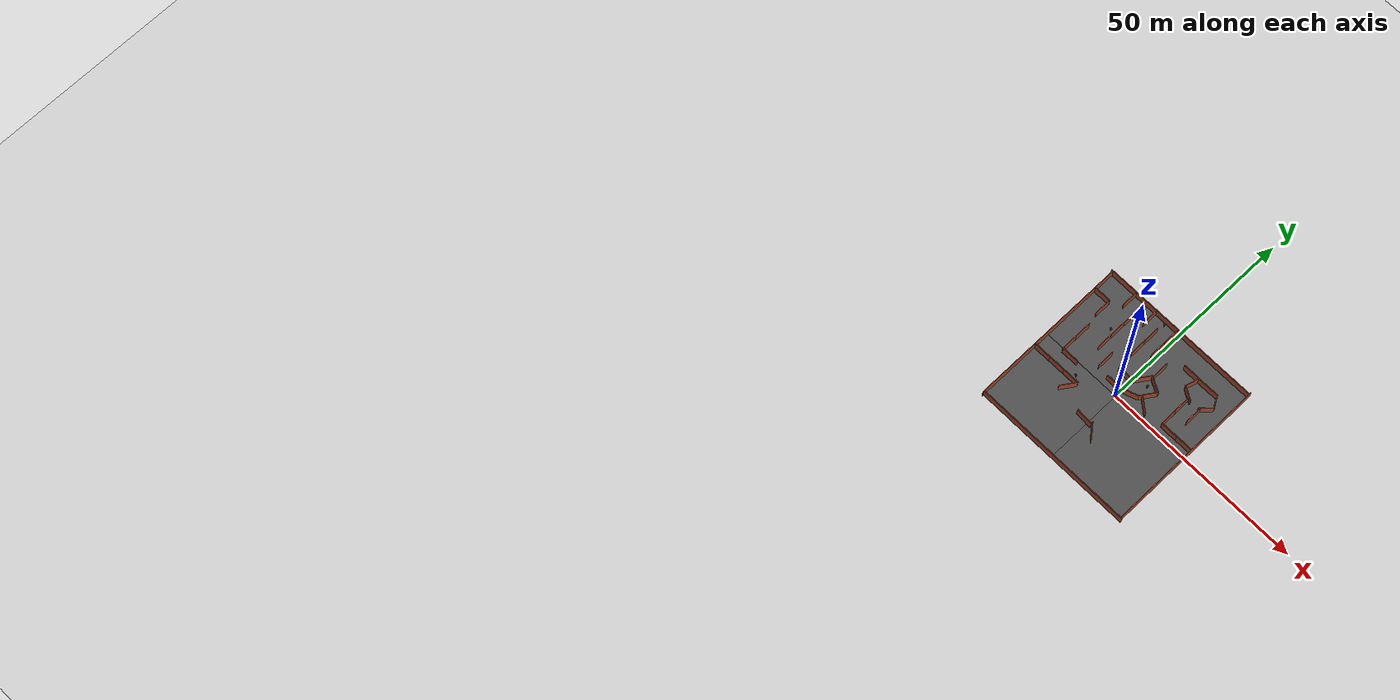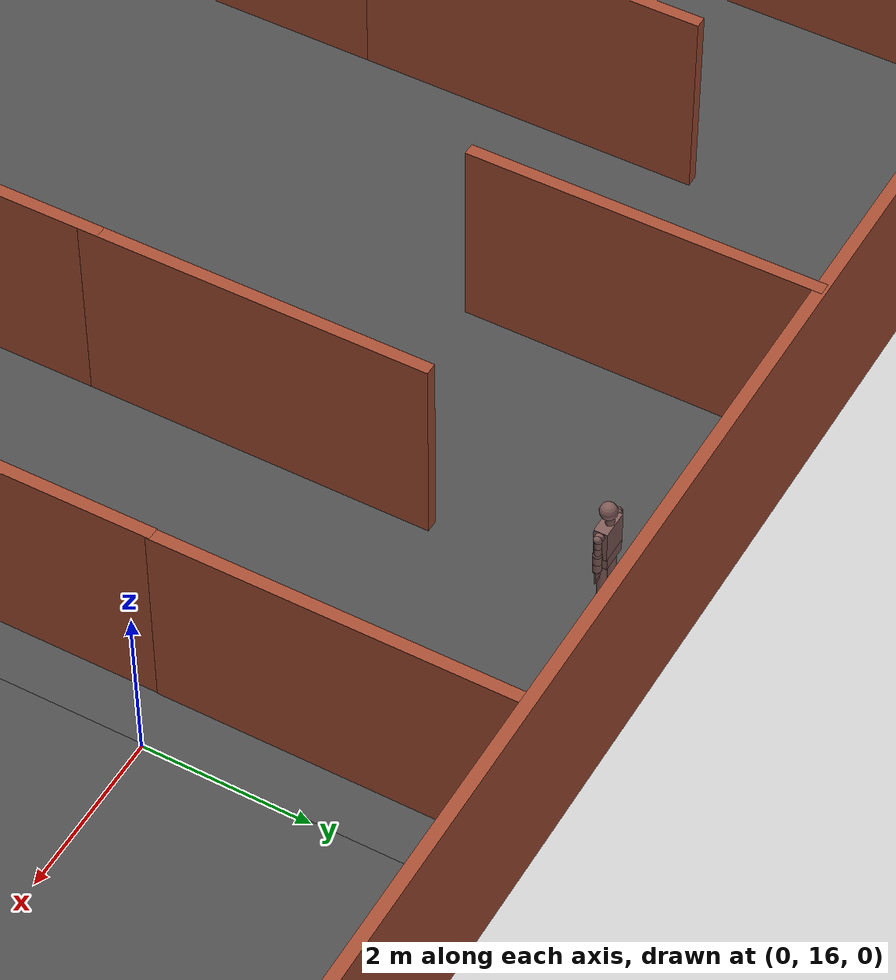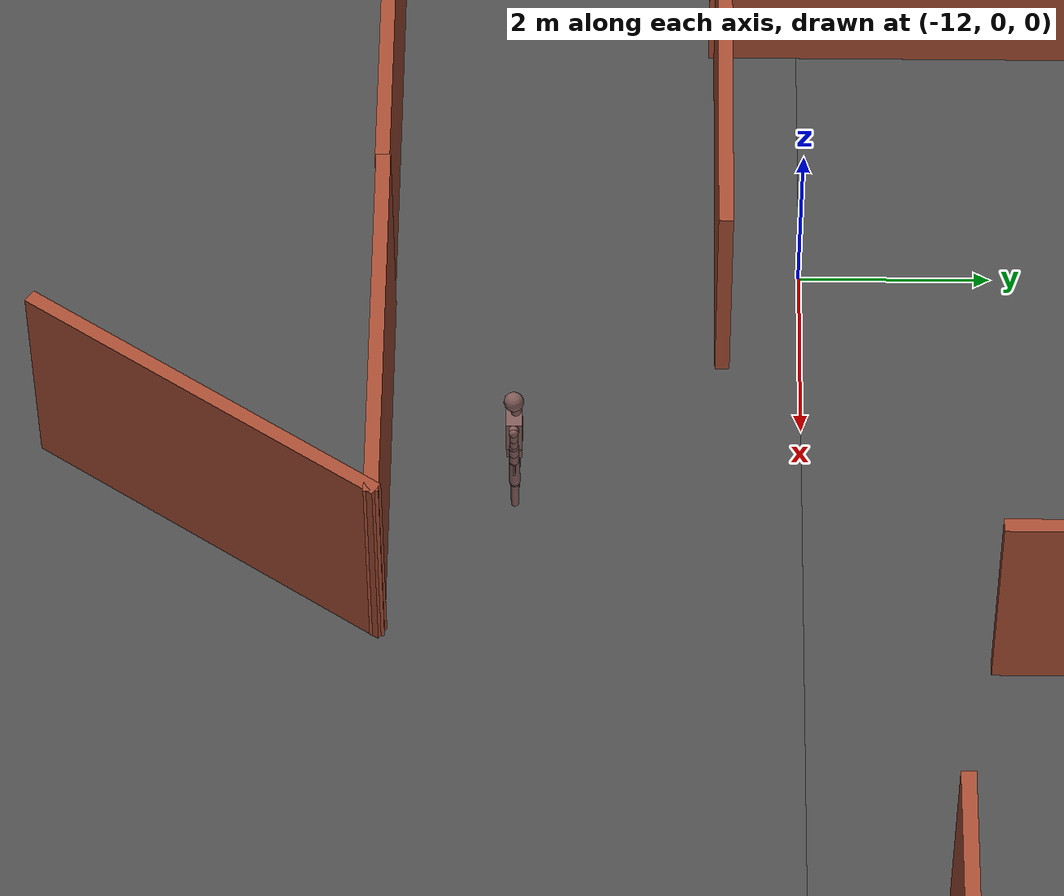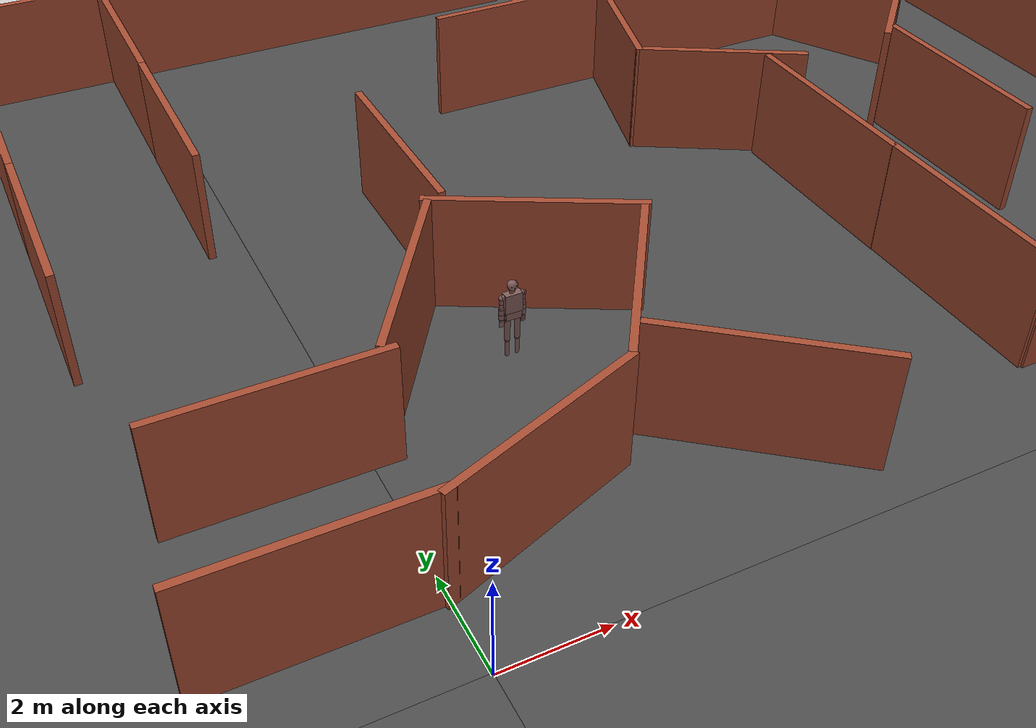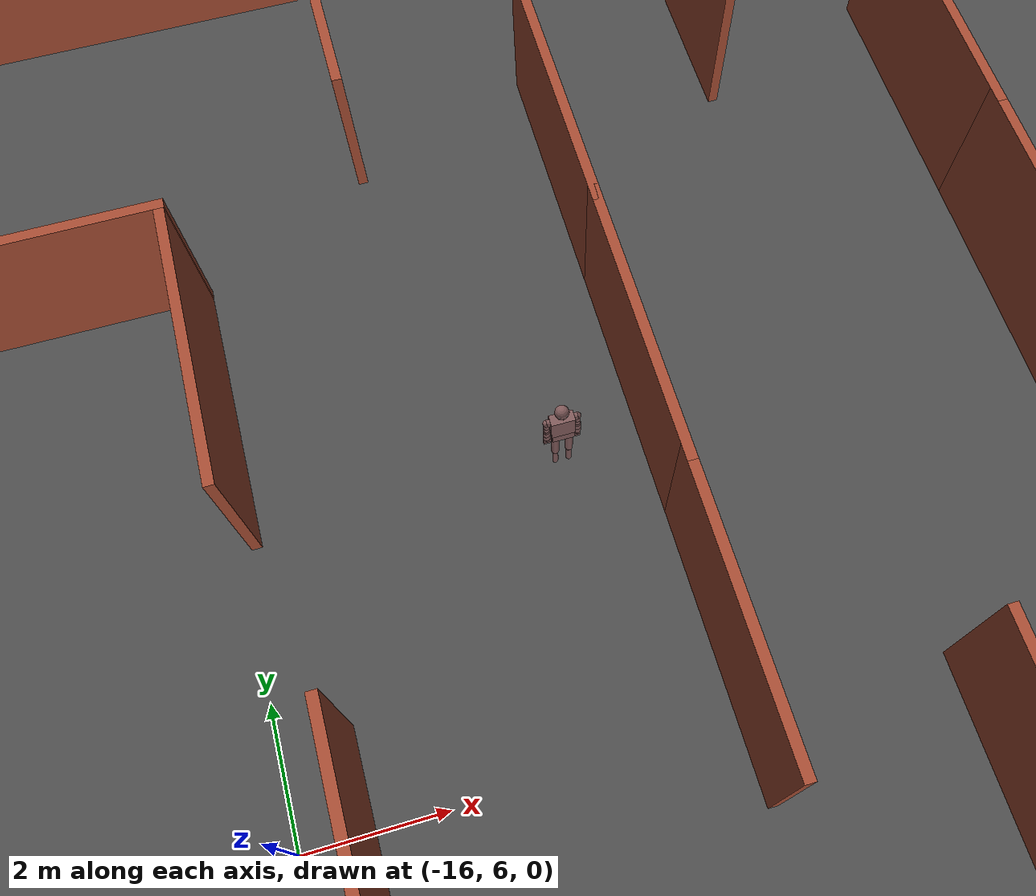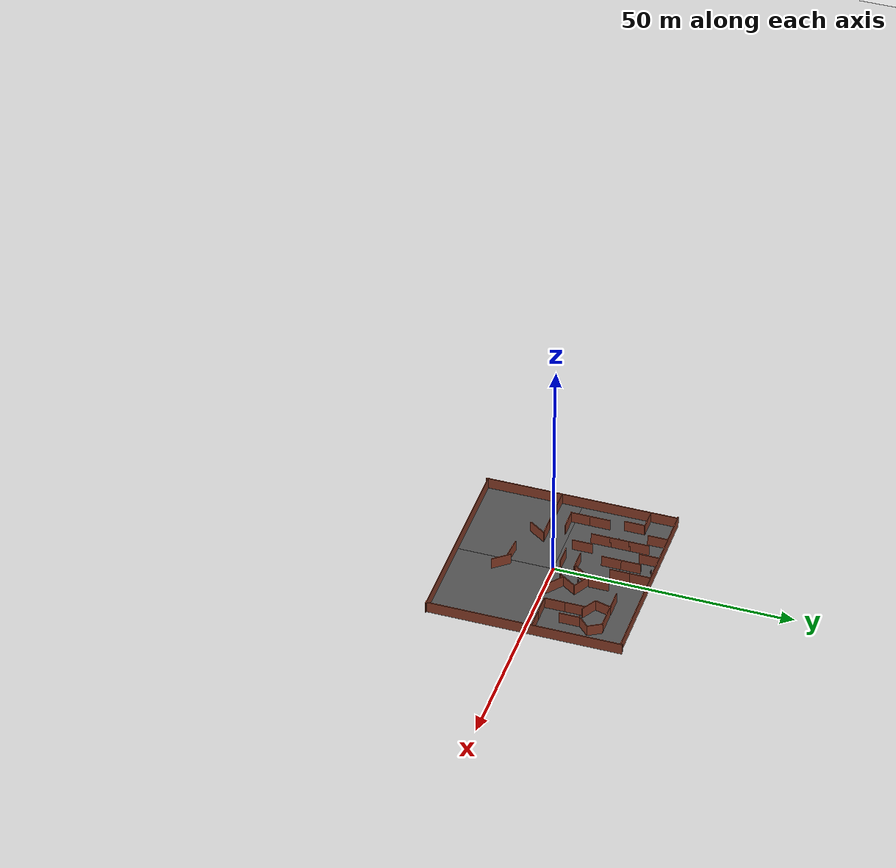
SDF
<sdf version="1.6">
 <world name="default">
  <light name="sun" type="directional">
   <pose>0 0 10 0 -0 0</pose>
   <diffuse>0.8 0.8 0.8 1</diffuse>
   <specular>0.2 0.2 0.2 1</specular>
   <attenuation>
    <range>1000</range>
    <constant>0.9</constant>
    <linear>0.01</linear>
    <quadratic>0.001</quadratic>
   </attenuation>
   <direction>-0.5 0.1 -0.9</direction>
  </light>
  <model name="ground_plane">
   <static>1</static>
   <link name="link">
    <collision name="collision">
     <geometry><plane><normal>0 0 1</normal><size>100 100</size></plane></geometry>
     <surface><friction><ode><mu>100</mu><mu2>50</mu2></ode></friction></surface>
    </collision>
    <visual name="visual">
     <cast_shadows>0</cast_shadows>
     <geometry><plane><normal>0 0 1</normal><size>100 100</size></plane></geometry>
     <material>
      <script><uri>file://media/materials/scripts/gazebo.material</uri><name>Gazebo/Grey</name></script>
     </material>
    </visual>
   </link>
  </model>
  <physics name="default_physics" default="0" type="ode">
   <max_step_size>0.001</max_step_size>
   <real_time_factor>1</real_time_factor>
   <real_time_update_rate>1000</real_time_update_rate>
  </physics>
  <scene><ambient>0.4 0.4 0.4 1</ambient><background>0.7 0.7 0.7 1</background><shadows>1</shadows></scene>
  <spherical_coordinates>
   <surface_model>EARTH_WGS84</surface_model>
   <latitude_deg>0</latitude_deg>
   <longitude_deg>0</longitude_deg>
   <elevation>0</elevation>
   <heading_deg>0</heading_deg>
  </spherical_coordinates>
  <model name="asphalt_plane">
   <static>1</static>
   <link name="link">
    <collision name="collision"><geometry><box><size>20 20 0.1</size></box></geometry></collision>
    <visual name="visual">
     <cast_shadows>0</cast_shadows>
     <geometry><box><size>20 20 0.1</size></box></geometry>
     <material>
      <script>
       <uri>model://asphalt_plane/materials/scripts</uri>
       <uri>model://asphalt_plane/materials/textures</uri>
       <name>vrc/asphalt</name>
      </script>
     </material>
    </visual>
   </link>
   <pose>10 10 0 0 -0 0</pose>
  </model>
  <model name="asphalt_plane_0">
   <static>1</static>
   <link name="link">
    <collision name="collision"><geometry><box><size>20 20 0.1</size></box></geometry></collision>
    <visual name="visual">
     <cast_shadows>0</cast_shadows>
     <geometry><box><size>20 20 0.1</size></box></geometry>
     <material>
      <script>
       <uri>model://asphalt_plane/materials/scripts</uri>
       <uri>model://asphalt_plane/materials/textures</uri>
       <name>vrc/asphalt</name>
      </script>
     </material>
    </visual>
   </link>
   <pose>-10 10 0 0 -0 0</pose>
  </model>
  <model name="asphalt_plane_1">
   <static>1</static>
   <link name="link">
    <collision name="collision"><geometry><box><size>20 20 0.1</size></box></geometry></collision>
    <visual name="visual">
     <cast_shadows>0</cast_shadows>
     <geometry><box><size>20 20 0.1</size></box></geometry>
     <material>
      <script>
       <uri>model://asphalt_plane/materials/scripts</uri>
       <uri>model://asphalt_plane/materials/textures</uri>
       <name>vrc/asphalt</name>
      </script>
     </material>
    </visual>
   </link>
   <pose>-10 -10 0 0 -0 0</pose>
  </model>
  <model name="asphalt_plane_2">
   <static>1</static>
   <link name="link">
    <collision name="collision"><geometry><box><size>20 20 0.1</size></box></geometry></collision>
    <visual name="visual">
     <cast_shadows>0</cast_shadows>
     <geometry><box><size>20 20 0.1</size></box></geometry>
     <material>
      <script>
       <uri>model://asphalt_plane/materials/scripts</uri>
       <uri>model://asphalt_plane/materials/textures</uri>
       <name>vrc/asphalt</name>
      </script>
     </material>
    </visual>
   </link>
   <pose>10 -10 0 0 -0 0</pose>
  </model>
  <model name="brick_longwalll">
   <pose>0.229981 -20.0786 0 0 -0 0</pose>
   <link name="brick_longwall_wall_0">
    <collision name="brick_longwall_wall_0_Collision">
     <geometry><box><size>40.5 0.15 2.5</size></box></geometry>
     <pose>0 0 1.25 0 -0 0</pose>
    </collision>
    <visual name="brick_longwall_wall_0_Visual">
     <pose>0 0 1.25 0 -0 0</pose>
     <geometry><box><size>40.5 0.15 2.5</size></box></geometry>
     <material>
      <script><uri>file://media/materials/scripts/gazebo.material</uri><name>Gazebo/Bricks</name></script>
      <ambient>1 1 1 1</ambient>
     </material>
    </visual>
    <pose>1e-06 0 0 0 -0 0</pose>
   </link>
   <static>1</static>
  </model>
  <model name="brick_longwalll_0">
   <pose>-20.0177 -0.255752 0 0 0 -1.57092</pose>
   <link name="brick_longwall_wall_0">
    <collision name="brick_longwall_wall_0_Collision">
     <geometry><box><size>40.5 0.15 2.5</size></box></geometry>
     <pose>0 0 1.25 0 -0 0</pose>
    </collision>
    <visual name="brick_longwall_wall_0_Visual">
     <pose>0 0 1.25 0 -0 0</pose>
     <geometry><box><size>40.5 0.15 2.5</size></box></geometry>
     <material>
      <script><uri>file://media/materials/scripts/gazebo.material</uri><name>Gazebo/Bricks</name></script>
      <ambient>1 1 1 1</ambient>
     </material>
    </visual>
    <pose>1e-06 0 0 0 -0 0</pose>
   </link>
   <static>1</static>
  </model>
  <model name="brick_longwalll_0_clone">
   <pose>20.1053 0.258056 0 0 0 -1.57092</pose>
   <link name="brick_longwall_wall_0">
    <collision name="brick_longwall_wall_0_Collision">
     <geometry><box><size>40.5 0.15 2.5</size></box></geometry>
     <pose>0 0 1.25 0 -0 0</pose>
    </collision>
    <visual name="brick_longwall_wall_0_Visual">
     <pose>0 0 1.25 0 -0 0</pose>
     <geometry><box><size>40.5 0.15 2.5</size></box></geometry>
     <material>
      <script><uri>file://media/materials/scripts/gazebo.material</uri><name>Gazebo/Bricks</name></script>
      <ambient>1 1 1 1</ambient>
     </material>
    </visual>
    <pose>1e-06 0 0 0 -0 0</pose>
   </link>
   <static>1</static>
  </model>
  <model name="brick_longwalll_clone">
   <pose>-0.214439 20.0862 0 0 -0 0</pose>
   <link name="brick_longwall_wall_0">
    <collision name="brick_longwall_wall_0_Collision">
     <geometry><box><size>40.5 0.15 2.5</size></box></geometry>
     <pose>0 0 1.25 0 -0 0</pose>
    </collision>
    <visual name="brick_longwall_wall_0_Visual">
     <pose>0 0 1.25 0 -0 0</pose>
     <geometry><box><size>40.5 0.15 2.5</size></box></geometry>
     <material>
      <script><uri>file://media/materials/scripts/gazebo.material</uri><name>Gazebo/Bricks</name></script>
      <ambient>1 1 1 1</ambient>
     </material>
    </visual>
    <pose>1e-06 0 0 0 -0 0</pose>
   </link>
   <static>1</static>
  </model>
  <model name="brick_longwall_room1">
   <pose>13.1523 12.4323 0 0 -0 0</pose>
   <link name="brick_longwall_wall_11">
    <collision name="brick_longwall_wall_11_Collision">
     <geometry><box><size>3.25 0.15 2.5</size></box></geometry>
     <pose>0 0 1.25 0 -0 0</pose>
    </collision>
    <visual name="brick_longwall_wall_11_Visual">
     <pose>0 0 1.25 0 -0 0</pose>
     <geometry><box><size>3.25 0.15 2.5</size></box></geometry>
     <material>
      <script><uri>file://media/materials/scripts/gazebo.material</uri><name>Gazebo/Bricks</name></script>
      <ambient>1 1 1 1</ambient>
     </material>
    </visual>
    <pose>3.12132 1.19483 0 0 0 -1.0472</pose>
   </link>
   <link name="brick_longwall_wall_12">
    <collision name="brick_longwall_wall_12_Collision">
     <geometry><box><size>3.5 0.15 2.5</size></box></geometry>
     <pose>0 0 1.25 0 -0 0</pose>
    </collision>
    <visual name="brick_longwall_wall_12_Visual">
     <pose>0 0 1.25 0 -0 0</pose>
     <geometry><box><size>3.5 0.15 2.5</size></box></geometry>
     <material>
      <script><uri>file://media/materials/scripts/gazebo.material</uri><name>Gazebo/Bricks</name></script>
      <ambient>1 1 1 1</ambient>
     </material>
    </visual>
    <pose>2.71192 -1.33192 0 0 0 -2.35619</pose>
   </link>
   <link name="brick_longwall_wall_7">
    <collision name="brick_longwall_wall_7_Collision">
     <geometry><box><size>5.52935 0.15 2.5</size></box></geometry>
     <pose>0 0 1.25 0 -0 0</pose>
    </collision>
    <visual name="brick_longwall_wall_7_Visual">
     <pose>0 0 1.25 0 -0 0</pose>
     <geometry><box><size>5.52935 0.15 2.5</size></box></geometry>
     <material>
      <script><uri>file://media/materials/scripts/gazebo.material</uri><name>Gazebo/Bricks</name></script>
      <ambient>1 1 1 1</ambient>
     </material>
    </visual>
    <pose>-0.343285 2.51793 0 0 0 -3.13444</pose>
   </link>
   <link name="brick_longwall_wall_8">
    <collision name="brick_longwall_wall_8_Collision">
     <geometry><box><size>3.5 0.15 2.5</size></box></geometry>
     <pose>0 0 1.25 0 -0 0</pose>
    </collision>
    <visual name="brick_longwall_wall_8_Visual">
     <pose>0 0 1.25 0 -0 0</pose>
     <geometry><box><size>3.5 0.15 2.5</size></box></geometry>
     <material>
      <script><uri>file://media/materials/scripts/gazebo.material</uri><name>Gazebo/Bricks</name></script>
      <ambient>1 1 1 1</ambient>
     </material>
    </visual>
    <pose>-3.46641 0.880761 0 0 0 -1.8326</pose>
   </link>
   <link name="brick_longwall_wall_9">
    <collision name="brick_longwall_wall_9_Collision">
     <geometry><box><size>3.75 0.15 2.5</size></box></geometry>
     <pose>0 0 1.25 0 -0 0</pose>
    </collision>
    <visual name="brick_longwall_wall_9_Visual">
     <pose>0 0 1.25 0 -0 0</pose>
     <geometry><box><size>3.75 0.15 2.5</size></box></geometry>
     <material>
      <script><uri>file://media/materials/scripts/gazebo.material</uri><name>Gazebo/Bricks</name></script>
      <ambient>1 1 1 1</ambient>
     </material>
    </visual>
    <pose>-2.34109 -1.63716 0 0 0 -0.523599</pose>
   </link>
   <static>1</static>
  </model>
  <model name="worlds_1">
   <pose>3 10.4406 0 0 -0 0</pose>
   <link name="brick_longwall_wall_0">
    <collision name="brick_longwall_wall_0_Collision">
     <geometry><box><size>4.25 0.15 2.5</size></box></geometry>
     <pose>0 0 1.25 0 -0 0</pose>
    </collision>
    <visual name="brick_longwall_wall_0_Visual">
     <pose>0 0 1.25 0 -0 0</pose>
     <geometry><box><size>4.25 0.15 2.5</size></box></geometry>
     <material>
      <script><uri>file://media/materials/scripts/gazebo.material</uri><name>Gazebo/Bricks</name></script>
      <ambient>1 1 1 1</ambient>
     </material>
    </visual>
    <pose>0 -0 0 0 -0 1.5708</pose>
   </link>
   <static>1</static>
  </model>
  <model name="worlds_2">
   <pose>4.42901 7.33195 0 0 -0 1.08023</pose>
   <link name="brick_longwall_wall_0">
    <collision name="brick_longwall_wall_0_Collision">
     <geometry><box><size>4.25 0.15 2.5</size></box></geometry>
     <pose>0 0 1.25 0 -0 0</pose>
    </collision>
    <visual name="brick_longwall_wall_0_Visual">
     <pose>0 0 1.25 0 -0 0</pose>
     <geometry><box><size>4.25 0.15 2.5</size></box></geometry>
     <material>
      <script><uri>file://media/materials/scripts/gazebo.material</uri><name>Gazebo/Bricks</name></script>
      <ambient>1 1 1 1</ambient>
     </material>
    </visual>
    <pose>0 -0 0 0 -0 1.5708</pose>
   </link>
   <static>1</static>
  </model>
  <model name="worlds_0_clone">
   <pose>-1 -9 0 0 -0 1.49697</pose>
   <link name="brick_longwall_wall_0">
    <collision name="brick_longwall_wall_0_Collision">
     <geometry><box><size>4.25 0.15 2.5</size></box></geometry>
     <pose>0 0 1.25 0 -0 0</pose>
    </collision>
    <visual name="brick_longwall_wall_0_Visual">
     <pose>0 0 1.25 0 -0 0</pose>
     <geometry><box><size>4.25 0.15 2.5</size></box></geometry>
     <material>
      <script><uri>file://media/materials/scripts/gazebo.material</uri><name>Gazebo/Bricks</name></script>
      <ambient>1 1 1 1</ambient>
     </material>
    </visual>
    <pose>0 -0 0 0 -0 1.5708</pose>
   </link>
   <static>1</static>
  </model>
  <model name="worlds_2_clone">
   <pose>2.34689 -10.1873 0 0 -0 0.67691</pose>
   <link name="brick_longwall_wall_0">
    <collision name="brick_longwall_wall_0_Collision">
     <geometry><box><size>4.25 0.15 2.5</size></box></geometry>
     <pose>0 0 1.25 0 -0 0</pose>
    </collision>
    <visual name="brick_longwall_wall_0_Visual">
     <pose>0 0 1.25 0 -0 0</pose>
     <geometry><box><size>4.25 0.15 2.5</size></box></geometry>
     <material>
      <script><uri>file://media/materials/scripts/gazebo.material</uri><name>Gazebo/Bricks</name></script>
      <ambient>1 1 1 1</ambient>
     </material>
    </visual>
    <pose>0 -0 0 0 -0 1.5708</pose>
   </link>
   <static>1</static>
  </model>
  <model name="worlds_1_clone">
   <pose>11.6021 8.07399 0 0 -0 0</pose>
   <link name="brick_longwall_wall_0">
    <collision name="brick_longwall_wall_0_Collision">
     <geometry><box><size>4.25 0.15 2.5</size></box></geometry>
     <pose>0 0 1.25 0 -0 0</pose>
    </collision>
    <visual name="brick_longwall_wall_0_Visual">
     <pose>0 0 1.25 0 -0 0</pose>
     <geometry><box><size>4.25 0.15 2.5</size></box></geometry>
     <material>
      <script><uri>file://media/materials/scripts/gazebo.material</uri><name>Gazebo/Bricks</name></script>
      <ambient>1 1 1 1</ambient>
     </material>
    </visual>
    <pose>0 -0 0 0 -0 1.5708</pose>
   </link>
   <static>1</static>
  </model>
  <model name="worlds_1_clone_0">
   <pose>11.6134 3.89135 0 0 -0 0</pose>
   <link name="brick_longwall_wall_0">
    <collision name="brick_longwall_wall_0_Collision">
     <geometry><box><size>4.25 0.15 2.5</size></box></geometry>
     <pose>0 0 1.25 0 -0 0</pose>
    </collision>
    <visual name="brick_longwall_wall_0_Visual">
     <pose>0 0 1.25 0 -0 0</pose>
     <geometry><box><size>4.25 0.15 2.5</size></box></geometry>
     <material>
      <script><uri>file://media/materials/scripts/gazebo.material</uri><name>Gazebo/Bricks</name></script>
      <ambient>1 1 1 1</ambient>
     </material>
    </visual>
    <pose>0 -0 0 0 -0 1.5708</pose>
   </link>
   <static>1</static>
  </model>
  <model name="worlds_1_clone_0_clone">
   <pose>13.736 1.79456 0 0 0 -1.57092</pose>
   <link name="brick_longwall_wall_0">
    <collision name="brick_longwall_wall_0_Collision">
     <geometry><box><size>4.25 0.15 2.5</size></box></geometry>
     <pose>0 0 1.25 0 -0 0</pose>
    </collision>
    <visual name="brick_longwall_wall_0_Visual">
     <pose>0 0 1.25 0 -0 0</pose>
     <geometry><box><size>4.25 0.15 2.5</size></box></geometry>
     <material>
      <script><uri>file://media/materials/scripts/gazebo.material</uri><name>Gazebo/Bricks</name></script>
      <ambient>1 1 1 1</ambient>
     </material>
    </visual>
    <pose>0 -0 0 0 -0 1.5708</pose>
   </link>
   <static>1</static>
  </model>
  <model name="worlds_1_clone_0_clone_clone">
   <pose>17.9203 1.82357 0 0 0 -1.57092</pose>
   <link name="brick_longwall_wall_0">
    <collision name="brick_longwall_wall_0_Collision">
     <geometry><box><size>4.25 0.15 2.5</size></box></geometry>
     <pose>0 0 1.25 0 -0 0</pose>
    </collision>
    <visual name="brick_longwall_wall_0_Visual">
     <pose>0 0 1.25 0 -0 0</pose>
     <geometry><box><size>4.25 0.15 2.5</size></box></geometry>
     <material>
      <script><uri>file://media/materials/scripts/gazebo.material</uri><name>Gazebo/Bricks</name></script>
      <ambient>1 1 1 1</ambient>
     </material>
    </visual>
    <pose>0 -0 0 0 -0 1.5708</pose>
   </link>
   <static>1</static>
  </model>
  <model name="worlds_1_clone_0_clone_clone_0">
   <pose>8 15 0 0 0 -1.57092</pose>
   <link name="brick_longwall_wall_0">
    <collision name="brick_longwall_wall_0_Collision">
     <geometry><box><size>4.25 0.15 2.5</size></box></geometry>
     <pose>0 0 1.25 0 -0 0</pose>
    </collision>
    <visual name="brick_longwall_wall_0_Visual">
     <pose>0 0 1.25 0 -0 0</pose>
     <geometry><box><size>4.25 0.15 2.5</size></box></geometry>
     <material>
      <script><uri>file://media/materials/scripts/gazebo.material</uri><name>Gazebo/Bricks</name></script>
      <ambient>1 1 1 1</ambient>
     </material>
    </visual>
    <pose>0 -0 0 0 -0 1.5708</pose>
   </link>
   <static>1</static>
  </model>
  <model name="worlds_1_clone_0_clone_clone_0_clone">
   <pose>-17.8162 14.4688 0 0 0 -1.57092</pose>
   <link name="brick_longwall_wall_0">
    <collision name="brick_longwall_wall_0_Collision">
     <geometry><box><size>4.25 0.15 2.5</size></box></geometry>
     <pose>0 0 1.25 0 -0 0</pose>
    </collision>
    <visual name="brick_longwall_wall_0_Visual">
     <pose>0 0 1.25 0 -0 0</pose>
     <geometry><box><size>4.25 0.15 2.5</size></box></geometry>
     <material>
      <script><uri>file://media/materials/scripts/gazebo.material</uri><name>Gazebo/Bricks</name></script>
      <ambient>1 1 1 1</ambient>
     </material>
    </visual>
    <pose>0 -0 0 0 -0 1.5708</pose>
   </link>
   <static>1</static>
  </model>
  <model name="worlds_1_clone_1">
   <pose>-13 18 0 0 -0 0</pose>
   <link name="brick_longwall_wall_0">
    <collision name="brick_longwall_wall_0_Collision">
     <geometry><box><size>4.25 0.15 2.5</size></box></geometry>
     <pose>0 0 1.25 0 -0 0</pose>
    </collision>
    <visual name="brick_longwall_wall_0_Visual">
     <pose>0 0 1.25 0 -0 0</pose>
     <geometry><box><size>4.25 0.15 2.5</size></box></geometry>
     <material>
      <script><uri>file://media/materials/scripts/gazebo.material</uri><name>Gazebo/Bricks</name></script>
      <ambient>1 1 1 1</ambient>
     </material>
    </visual>
    <pose>0 -0 0 0 -0 1.5708</pose>
   </link>
   <static>1</static>
  </model>
  <model name="worlds_1_clone_1_clone">
   <pose>-15.7734 12.3225 0 0 -0 0</pose>
   <link name="brick_longwall_wall_0">
    <collision name="brick_longwall_wall_0_Collision">
     <geometry><box><size>4.25 0.15 2.5</size></box></geometry>
     <pose>0 0 1.25 0 -0 0</pose>
    </collision>
    <visual name="brick_longwall_wall_0_Visual">
     <pose>0 0 1.25 0 -0 0</pose>
     <geometry><box><size>4.25 0.15 2.5</size></box></geometry>
     <material>
      <script><uri>file://media/materials/scripts/gazebo.material</uri><name>Gazebo/Bricks</name></script>
      <ambient>1 1 1 1</ambient>
     </material>
    </visual>
    <pose>0 -0 0 0 -0 1.5708</pose>
   </link>
   <static>1</static>
  </model>
  <model name="worlds_1_clone_1_clone_clone">
   <pose>-15.0638 5.287 0 0 -0 0</pose>
   <link name="brick_longwall_wall_0">
    <collision name="brick_longwall_wall_0_Collision">
     <geometry><box><size>4.25 0.15 2.5</size></box></geometry>
     <pose>0 0 1.25 0 -0 0</pose>
    </collision>
    <visual name="brick_longwall_wall_0_Visual">
     <pose>0 0 1.25 0 -0 0</pose>
     <geometry><box><size>4.25 0.15 2.5</size></box></geometry>
     <material>
      <script><uri>file://media/materials/scripts/gazebo.material</uri><name>Gazebo/Bricks</name></script>
      <ambient>1 1 1 1</ambient>
     </material>
    </visual>
    <pose>0 -0 0 0 -0 1.5708</pose>
   </link>
   <static>1</static>
  </model>
  <model name="worlds_1_clone_1_clone_clone_0">
   <pose>-15.0769 1.18275 0 0 -0 0</pose>
   <link name="brick_longwall_wall_0">
    <collision name="brick_longwall_wall_0_Collision">
     <geometry><box><size>4.25 0.15 2.5</size></box></geometry>
     <pose>0 0 1.25 0 -0 0</pose>
    </collision>
    <visual name="brick_longwall_wall_0_Visual">
     <pose>0 0 1.25 0 -0 0</pose>
     <geometry><box><size>4.25 0.15 2.5</size></box></geometry>
     <material>
      <script><uri>file://media/materials/scripts/gazebo.material</uri><name>Gazebo/Bricks</name></script>
      <ambient>1 1 1 1</ambient>
     </material>
    </visual>
    <pose>0 -0 0 0 -0 1.5708</pose>
   </link>
   <static>1</static>
  </model>
  <model name="worlds_1_clone_0_clone_clone_0_clone_clone">
   <pose>-17.8054 -4.32089 0 0 0 -1.57092</pose>
   <link name="brick_longwall_wall_0">
    <collision name="brick_longwall_wall_0_Collision">
     <geometry><box><size>4.25 0.15 2.5</size></box></geometry>
     <pose>0 0 1.25 0 -0 0</pose>
    </collision>
    <visual name="brick_longwall_wall_0_Visual">
     <pose>0 0 1.25 0 -0 0</pose>
     <geometry><box><size>4.25 0.15 2.5</size></box></geometry>
     <material>
      <script><uri>file://media/materials/scripts/gazebo.material</uri><name>Gazebo/Bricks</name></script>
      <ambient>1 1 1 1</ambient>
     </material>
    </visual>
    <pose>0 -0 0 0 -0 1.5708</pose>
   </link>
   <static>1</static>
  </model>
  <model name="worlds_1_clone_0_clone_clone_0_clone_clone_0">
   <pose>-13.6699 -4.29855 0 0 0 -1.57092</pose>
   <link name="brick_longwall_wall_0">
    <collision name="brick_longwall_wall_0_Collision">
     <geometry><box><size>4.25 0.15 2.5</size></box></geometry>
     <pose>0 0 1.25 0 -0 0</pose>
    </collision>
    <visual name="brick_longwall_wall_0_Visual">
     <pose>0 0 1.25 0 -0 0</pose>
     <geometry><box><size>4.25 0.15 2.5</size></box></geometry>
     <material>
      <script><uri>file://media/materials/scripts/gazebo.material</uri><name>Gazebo/Bricks</name></script>
      <ambient>1 1 1 1</ambient>
     </material>
    </visual>
    <pose>0 -0 0 0 -0 1.5708</pose>
   </link>
   <static>1</static>
  </model>
  <model name="worlds_1_clone_0_clone_clone_0_clone_clone_1">
   <pose>-9.47339 -4.28892 0 0 0 -1.57092</pose>
   <link name="brick_longwall_wall_0">
    <collision name="brick_longwall_wall_0_Collision">
     <geometry><box><size>4.25 0.15 2.5</size></box></geometry>
     <pose>0 0 1.25 0 -0 0</pose>
    </collision>
    <visual name="brick_longwall_wall_0_Visual">
     <pose>0 0 1.25 0 -0 0</pose>
     <geometry><box><size>4.25 0.15 2.5</size></box></geometry>
     <material>
      <script><uri>file://media/materials/scripts/gazebo.material</uri><name>Gazebo/Bricks</name></script>
      <ambient>1 1 1 1</ambient>
     </material>
    </visual>
    <pose>0 -0 0 0 -0 1.5708</pose>
   </link>
   <static>1</static>
  </model>
  <model name="worlds_1_clone_1_clone_0">
   <pose>-0.708445 17.9147 0 0 -0 0</pose>
   <link name="brick_longwall_wall_0">
    <collision name="brick_longwall_wall_0_Collision">
     <geometry><box><size>4.25 0.15 2.5</size></box></geometry>
     <pose>0 0 1.25 0 -0 0</pose>
    </collision>
    <visual name="brick_longwall_wall_0_Visual">
     <pose>0 0 1.25 0 -0 0</pose>
     <geometry><box><size>4.25 0.15 2.5</size></box></geometry>
     <material>
      <script><uri>file://media/materials/scripts/gazebo.material</uri><name>Gazebo/Bricks</name></script>
      <ambient>1 1 1 1</ambient>
     </material>
    </visual>
    <pose>0 -0 0 0 -0 1.5708</pose>
   </link>
   <static>1</static>
  </model>
  <model name="worlds_1_clone_1_clone_1">
   <pose>-0.716318 13.714 0 0 -0 0</pose>
   <link name="brick_longwall_wall_0">
    <collision name="brick_longwall_wall_0_Collision">
     <geometry><box><size>4.25 0.15 2.5</size></box></geometry>
     <pose>0 0 1.25 0 -0 0</pose>
    </collision>
    <visual name="brick_longwall_wall_0_Visual">
     <pose>0 0 1.25 0 -0 0</pose>
     <geometry><box><size>4.25 0.15 2.5</size></box></geometry>
     <material>
      <script><uri>file://media/materials/scripts/gazebo.material</uri><name>Gazebo/Bricks</name></script>
      <ambient>1 1 1 1</ambient>
     </material>
    </visual>
    <pose>0 -0 0 0 -0 1.5708</pose>
   </link>
   <static>1</static>
  </model>
  <model name="worlds_1_clone_1_clone_2">
   <pose>-7 18 0 0 -0 0</pose>
   <link name="brick_longwall_wall_0">
    <collision name="brick_longwall_wall_0_Collision">
     <geometry><box><size>4.25 0.15 2.5</size></box></geometry>
     <pose>0 0 1.25 0 -0 0</pose>
    </collision>
    <visual name="brick_longwall_wall_0_Visual">
     <pose>0 0 1.25 0 -0 0</pose>
     <geometry><box><size>4.25 0.15 2.5</size></box></geometry>
     <material>
      <script><uri>file://media/materials/scripts/gazebo.material</uri><name>Gazebo/Bricks</name></script>
      <ambient>1 1 1 1</ambient>
     </material>
    </visual>
    <pose>0 -0 0 0 -0 1.5708</pose>
   </link>
   <static>1</static>
  </model>
  <model name="worlds_1_clone_1_clone_3">
   <pose>-10 15 0 0 -0 0</pose>
   <link name="brick_longwall_wall_0">
    <collision name="brick_longwall_wall_0_Collision">
     <geometry><box><size>4.25 0.15 2.5</size></box></geometry>
     <pose>0 0 1.25 0 -0 0</pose>
    </collision>
    <visual name="brick_longwall_wall_0_Visual">
     <pose>0 0 1.25 0 -0 0</pose>
     <geometry><box><size>4.25 0.15 2.5</size></box></geometry>
     <material>
      <script><uri>file://media/materials/scripts/gazebo.material</uri><name>Gazebo/Bricks</name></script>
      <ambient>1 1 1 1</ambient>
     </material>
    </visual>
    <pose>0 -0 0 0 -0 1.5708</pose>
   </link>
   <static>1</static>
  </model>
  <model name="worlds_1_clone_1_clone_4">
   <pose>-10 11 0 0 -0 0</pose>
   <link name="brick_longwall_wall_0">
    <collision name="brick_longwall_wall_0_Collision">
     <geometry><box><size>4.25 0.15 2.5</size></box></geometry>
     <pose>0 0 1.25 0 -0 0</pose>
    </collision>
    <visual name="brick_longwall_wall_0_Visual">
     <pose>0 0 1.25 0 -0 0</pose>
     <geometry><box><size>4.25 0.15 2.5</size></box></geometry>
     <material>
      <script><uri>file://media/materials/scripts/gazebo.material</uri><name>Gazebo/Bricks</name></script>
      <ambient>1 1 1 1</ambient>
     </material>
    </visual>
    <pose>0 -0 0 0 -0 1.5708</pose>
   </link>
   <static>1</static>
  </model>
  <model name="worlds_1_clone_1_clone_5">
   <pose>-4 15 0 0 -0 0</pose>
   <link name="brick_longwall_wall_0">
    <collision name="brick_longwall_wall_0_Collision">
     <geometry><box><size>4.25 0.15 2.5</size></box></geometry>
     <pose>0 0 1.25 0 -0 0</pose>
    </collision>
    <visual name="brick_longwall_wall_0_Visual">
     <pose>0 0 1.25 0 -0 0</pose>
     <geometry><box><size>4.25 0.15 2.5</size></box></geometry>
     <material>
      <script><uri>file://media/materials/scripts/gazebo.material</uri><name>Gazebo/Bricks</name></script>
      <ambient>1 1 1 1</ambient>
     </material>
    </visual>
    <pose>0 -0 0 0 -0 1.5708</pose>
   </link>
   <static>1</static>
  </model>
  <model name="worlds_1_clone_1_clone_6">
   <pose>-4 11 0 0 -0 0</pose>
   <link name="brick_longwall_wall_0">
    <collision name="brick_longwall_wall_0_Collision">
     <geometry><box><size>4.25 0.15 2.5</size></box></geometry>
     <pose>0 0 1.25 0 -0 0</pose>
    </collision>
    <visual name="brick_longwall_wall_0_Visual">
     <pose>0 0 1.25 0 -0 0</pose>
     <geometry><box><size>4.25 0.15 2.5</size></box></geometry>
     <material>
      <script><uri>file://media/materials/scripts/gazebo.material</uri><name>Gazebo/Bricks</name></script>
      <ambient>1 1 1 1</ambient>
     </material>
    </visual>
    <pose>0 -0 0 0 -0 1.5708</pose>
   </link>
   <static>1</static>
  </model>
  <model name="worlds_1_clone_1_clone_7">
   <pose>-10 7 0 0 -0 0</pose>
   <link name="brick_longwall_wall_0">
    <collision name="brick_longwall_wall_0_Collision">
     <geometry><box><size>4.25 0.15 2.5</size></box></geometry>
     <pose>0 0 1.25 0 -0 0</pose>
    </collision>
    <visual name="brick_longwall_wall_0_Visual">
     <pose>0 0 1.25 0 -0 0</pose>
     <geometry><box><size>4.25 0.15 2.5</size></box></geometry>
     <material>
      <script><uri>file://media/materials/scripts/gazebo.material</uri><name>Gazebo/Bricks</name></script>
      <ambient>1 1 1 1</ambient>
     </material>
    </visual>
    <pose>0 -0 0 0 -0 1.5708</pose>
   </link>
   <static>1</static>
  </model>
  <model name="worlds_1_clone_0_clone_clone_0_clone_clone_0_clone">
   <pose>-12.8938 -0.809745 0 0 0 -1.57092</pose>
   <link name="brick_longwall_wall_0">
    <collision name="brick_longwall_wall_0_Collision">
     <geometry><box><size>4.25 0.15 2.5</size></box></geometry>
     <pose>0 0 1.25 0 -0 0</pose>
    </collision>
    <visual name="brick_longwall_wall_0_Visual">
     <pose>0 0 1.25 0 -0 0</pose>
     <geometry><box><size>4.25 0.15 2.5</size></box></geometry>
     <material>
      <script><uri>file://media/materials/scripts/gazebo.material</uri><name>Gazebo/Bricks</name></script>
      <ambient>1 1 1 1</ambient>
     </material>
    </visual>
    <pose>0 -0 0 0 -0 1.5708</pose>
   </link>
   <static>1</static>
  </model>
  <model name="worlds_1_clone_1_clone_7_clone">
   <pose>-7 4 0 0 -0 0</pose>
   <link name="brick_longwall_wall_0">
    <collision name="brick_longwall_wall_0_Collision">
     <geometry><box><size>4.25 0.15 2.5</size></box></geometry>
     <pose>0 0 1.25 0 -0 0</pose>
    </collision>
    <visual name="brick_longwall_wall_0_Visual">
     <pose>0 0 1.25 0 -0 0</pose>
     <geometry><box><size>4.25 0.15 2.5</size></box></geometry>
     <material>
      <script><uri>file://media/materials/scripts/gazebo.material</uri><name>Gazebo/Bricks</name></script>
      <ambient>1 1 1 1</ambient>
     </material>
    </visual>
    <pose>0 -0 0 0 -0 1.5708</pose>
   </link>
   <static>1</static>
  </model>
  <model name="worlds_1_clone_1_clone_7_clone_clone">
   <pose>1.48825 6.4581 0 0 0 -0.589381</pose>
   <link name="brick_longwall_wall_0">
    <collision name="brick_longwall_wall_0_Collision">
     <geometry><box><size>4.25 0.15 2.5</size></box></geometry>
     <pose>0 0 1.25 0 -0 0</pose>
    </collision>
    <visual name="brick_longwall_wall_0_Visual">
     <pose>0 0 1.25 0 -0 0</pose>
     <geometry><box><size>4.25 0.15 2.5</size></box></geometry>
     <material>
      <script><uri>file://media/materials/scripts/gazebo.material</uri><name>Gazebo/Bricks</name></script>
      <ambient>1 1 1 1</ambient>
     </material>
    </visual>
    <pose>0 -0 0 0 -0 1.5708</pose>
   </link>
   <static>1</static>
  </model>
  <model name="worlds_1_clone_1_clone_7_clone_clone_clone">
   <pose>5 4.58681 0 0 0 -0.589381</pose>
   <link name="brick_longwall_wall_0">
    <collision name="brick_longwall_wall_0_Collision">
     <geometry><box><size>4.25 0.15 2.5</size></box></geometry>
     <pose>0 0 1.25 0 -0 0</pose>
    </collision>
    <visual name="brick_longwall_wall_0_Visual">
     <pose>0 0 1.25 0 -0 0</pose>
     <geometry><box><size>4.25 0.15 2.5</size></box></geometry>
     <material>
      <script><uri>file://media/materials/scripts/gazebo.material</uri><name>Gazebo/Bricks</name></script>
      <ambient>1 1 1 1</ambient>
     </material>
    </visual>
    <pose>0 -0 0 0 -0 1.5708</pose>
   </link>
   <static>1</static>
  </model>
  <model name="worlds_1_clone_0_clone_clone_0_clone_clone_0_clone_clone">
   <pose>-1.54431 4.60476 0 0 0 -1.57092</pose>
   <link name="brick_longwall_wall_0">
    <collision name="brick_longwall_wall_0_Collision">
     <geometry><box><size>4.25 0.15 2.5</size></box></geometry>
     <pose>0 0 1.25 0 -0 0</pose>
    </collision>
    <visual name="brick_longwall_wall_0_Visual">
     <pose>0 0 1.25 0 -0 0</pose>
     <geometry><box><size>4.25 0.15 2.5</size></box></geometry>
     <material>
      <script><uri>file://media/materials/scripts/gazebo.material</uri><name>Gazebo/Bricks</name></script>
      <ambient>1 1 1 1</ambient>
     </material>
    </visual>
    <pose>0 -0 0 0 -0 1.5708</pose>
   </link>
   <static>1</static>
  </model>
  <model name="worlds_1_clone_0_clone_clone_0_clone_clone_0_clone_clone_0">
   <pose>1.87166 2.0906 0 0 0 -1.22347</pose>
   <link name="brick_longwall_wall_0">
    <collision name="brick_longwall_wall_0_Collision">
     <geometry><box><size>4.25 0.15 2.5</size></box></geometry>
     <pose>0 0 1.25 0 -0 0</pose>
    </collision>
    <visual name="brick_longwall_wall_0_Visual">
     <pose>0 0 1.25 0 -0 0</pose>
     <geometry><box><size>4.25 0.15 2.5</size></box></geometry>
     <material>
      <script><uri>file://media/materials/scripts/gazebo.material</uri><name>Gazebo/Bricks</name></script>
      <ambient>1 1 1 1</ambient>
     </material>
    </visual>
    <pose>0 -0 0 0 -0 1.5708</pose>
   </link>
   <static>1</static>
  </model>
  <model name="worlds_1_clone_0_clone_clone_0_clone_clone_0_clone_clone_clone">
   <pose>-2 1.45154 0 0 0 -1.57092</pose>
   <link name="brick_longwall_wall_0">
    <collision name="brick_longwall_wall_0_Collision">
     <geometry><box><size>4.25 0.15 2.5</size></box></geometry>
     <pose>0 0 1.25 0 -0 0</pose>
    </collision>
    <visual name="brick_longwall_wall_0_Visual">
     <pose>0 0 1.25 0 -0 0</pose>
     <geometry><box><size>4.25 0.15 2.5</size></box></geometry>
     <material>
      <script><uri>file://media/materials/scripts/gazebo.material</uri><name>Gazebo/Bricks</name></script>
      <ambient>1 1 1 1</ambient>
     </material>
    </visual>
    <pose>0 -0 0 0 -0 1.5708</pose>
   </link>
   <static>1</static>
  </model>
  <model name="worlds_1_clone_1_clone_7_clone_clone_0">
   <pose>6.00131 2.13117 0 0 -0 0.90029</pose>
   <link name="brick_longwall_wall_0">
    <collision name="brick_longwall_wall_0_Collision">
     <geometry><box><size>4.25 0.15 2.5</size></box></geometry>
     <pose>0 0 1.25 0 -0 0</pose>
    </collision>
    <visual name="brick_longwall_wall_0_Visual">
     <pose>0 0 1.25 0 -0 0</pose>
     <geometry><box><size>4.25 0.15 2.5</size></box></geometry>
     <material>
      <script><uri>file://media/materials/scripts/gazebo.material</uri><name>Gazebo/Bricks</name></script>
      <ambient>1 1 1 1</ambient>
     </material>
    </visual>
    <pose>0 -0 0 0 -0 1.5708</pose>
   </link>
   <static>1</static>
  </model>
  <model name="worlds_1_clone_1_clone_7_clone_clone_clone_0">
   <pose>-8.55218 -6 0 0 0 -0.589381</pose>
   <link name="brick_longwall_wall_0">
    <collision name="brick_longwall_wall_0_Collision">
     <geometry><box><size>4.25 0.15 2.5</size></box></geometry>
     <pose>0 0 1.25 0 -0 0</pose>
    </collision>
    <visual name="brick_longwall_wall_0_Visual">
     <pose>0 0 1.25 0 -0 0</pose>
     <geometry><box><size>4.25 0.15 2.5</size></box></geometry>
     <material>
      <script><uri>file://media/materials/scripts/gazebo.material</uri><name>Gazebo/Bricks</name></script>
      <ambient>1 1 1 1</ambient>
     </material>
    </visual>
    <pose>0 -0 0 0 -0 1.5708</pose>
   </link>
   <static>1</static>
  </model>
  <model name="worlds_1_clone_clone">
   <pose>15 8 0 0 -0 0</pose>
   <link name="brick_longwall_wall_0">
    <collision name="brick_longwall_wall_0_Collision">
     <geometry><box><size>4.25 0.15 2.5</size></box></geometry>
     <pose>0 0 1.25 0 -0 0</pose>
    </collision>
    <visual name="brick_longwall_wall_0_Visual">
     <pose>0 0 1.25 0 -0 0</pose>
     <geometry><box><size>4.25 0.15 2.5</size></box></geometry>
     <material>
      <script><uri>file://media/materials/scripts/gazebo.material</uri><name>Gazebo/Bricks</name></script>
      <ambient>1 1 1 1</ambient>
     </material>
    </visual>
    <pose>0 -0 0 0 -0 1.5708</pose>
   </link>
   <static>1</static>
  </model>
  <gravity>0 0 -9.8</gravity>
  <magnetic_field>6e-06 2.3e-05 -4.2e-05</magnetic_field>
  <atmosphere type="adiabatic"/>
  <audio><device>default</device></audio>
  <model name="unique_sphere">
   <pose>-150 -150 0.01 0 -0 0</pose>
   <link name="link">
    <sensor name="my_contact" type="contact">
     <plugin name="my_plugin" filename="libgazebo_plugin_contact.so"/>
     <contact><collision>test_collision</collision><topic>__default_topic__</topic></contact>
    </sensor>
    <collision name="test_collision"><geometry><sphere><radius>0.01</radius></sphere></geometry></collision>
    <visual name="test_visual"><geometry><sphere><radius>0.01</radius></sphere></geometry></visual>
    <inertial>
     <inertia><ixx>1</ixx><ixy>0</ixy><ixz>0</ixz><iyy>1</iyy><iyz>0</iyz><izz>1</izz></inertia>
     <mass>1</mass>
    </inertial>
   </link>
  </model>
  <model name="victim175_hot">
   <static>1</static>
   <self_collide>1</self_collide>
   <link name="head">
    <pose>0 0 1.625 0 -0 0</pose>
    <visual name="visual">
     <geometry><sphere><radius>0.1</radius></sphere></geometry>
     <material>
      <emissive>0.5 0.35 0.35 1</emissive>
      <ambient>0.5 0.35 0.35 1</ambient>
      <diffuse>0.5 0.35 0.35 1</diffuse>
      <specular>0 0 0 0</specular>
     </material>
    </visual>
    <collision name="collision"><geometry><sphere><radius>0.1</radius></sphere></geometry></collision>
    <visual name="visual_nose">
     <pose>0 -0.1 -0.01 0 -0 0</pose>
     <geometry><sphere><radius>0.01</radius></sphere></geometry>
     <material>
      <emissive>0.5 0.35 0.35 1</emissive>
      <ambient>0.5 0.35 0.35 1</ambient>
      <diffuse>0.5 0.35 0.35 1</diffuse>
      <specular>0 0 0 0</specular>
     </material>
    </visual>
    <visual name="visual_rEye">
     <pose>-0.05 -0.08 0.02 0 -0 0</pose>
     <geometry><sphere><radius>0.01</radius></sphere></geometry>
     <material>
      <script><uri>file://media/materials/scripts/gazebo.material</uri><name>Gazebo/Black</name></script>
     </material>
    </visual>
    <visual name="visual_lEye">
     <pose>0.05 -0.08 0.02 0 -0 0</pose>
     <geometry><sphere><radius>0.01</radius></sphere></geometry>
     <material>
      <script><uri>file://media/materials/scripts/gazebo.material</uri><name>Gazebo/Black</name></script>
     </material>
    </visual>
    <self_collide>1</self_collide>
   </link>
   <link name="neck">
    <pose>0 0.02 1.49 0 -0 0</pose>
    <visual name="visual">
     <geometry><cylinder><radius>0.05</radius><length>0.15</length></cylinder></geometry>
     <material>
      <emissive>0.5 0.35 0.35 1</emissive>
      <ambient>0.5 0.35 0.35 1</ambient>
      <diffuse>0.5 0.35 0.35 1</diffuse>
      <specular>0 0 0 0</specular>
     </material>
    </visual>
    <collision name="collision">
     <geometry><cylinder><radius>0.05</radius><length>0.15</length></cylinder></geometry>
    </collision>
    <self_collide>1</self_collide>
   </link>
   <joint name="neck_head" type="revolute">
    <pose>0 0.02 -0.075 0 -0 0</pose>
    <child>head</child>
    <parent>neck</parent>
    <axis>
     <xyz>0 0 -1</xyz>
     <limit><lower>-1.7</lower><upper>1.7</upper></limit>
     <dynamics>
      <friction>0.01</friction>
      <spring_reference>0</spring_reference>
      <spring_stiffness>0</spring_stiffness>
     </dynamics>
     <use_parent_model_frame>0</use_parent_model_frame>
    </axis>
   </joint>
   <link name="body">
    <pose>0 0 1.255 0 -0 0</pose>
    <visual name="visual">
     <geometry><box><size>0.34 0.16 0.4</size></box></geometry>
     <material>
      <emissive>0.5 0.35 0.35 1</emissive>
      <ambient>0.5 0.35 0.35 1</ambient>
      <diffuse>0.5 0.35 0.35 1</diffuse>
      <specular>0 0 0 0</specular>
     </material>
    </visual>
    <collision name="collision"><geometry><box><size>0.34 0.16 0.4</size></box></geometry></collision>
    <self_collide>1</self_collide>
   </link>
   <joint name="body_neck" type="revolute">
    <pose>0 0.06 -0.075 0 -0 0</pose>
    <child>neck</child>
    <parent>body</parent>
    <axis>
     <xyz>1 0 0</xyz>
     <limit><lower>-0.2</lower><upper>1</upper></limit>
     <dynamics>
      <friction>0.01</friction>
      <spring_reference>0</spring_reference>
      <spring_stiffness>0</spring_stiffness>
     </dynamics>
     <use_parent_model_frame>0</use_parent_model_frame>
    </axis>
   </joint>
   <link name="waist">
    <pose>0 0 1.005 0 -0 0</pose>
    <visual name="visual">
     <pose>0 0 -0.025 0 -0 0</pose>
     <geometry><box><size>0.31 0.16 0.15</size></box></geometry>
     <material>
      <emissive>0.5 0.35 0.35 1</emissive>
      <ambient>0.5 0.35 0.35 1</ambient>
      <diffuse>0.5 0.35 0.35 1</diffuse>
      <specular>0 0 0 0</specular>
     </material>
    </visual>
    <collision name="collision"><geometry><box><size>0.31 0.16 0.1</size></box></geometry></collision>
    <visual name="visual2">
     <pose>0 0 0.05 3.14159 1.57079 3.14159</pose>
     <geometry><cylinder><radius>0.08</radius><length>0.31</length></cylinder></geometry>
     <material>
      <emissive>0.5 0.35 0.35 1</emissive>
      <ambient>0.5 0.35 0.35 1</ambient>
      <diffuse>0.5 0.35 0.35 1</diffuse>
      <specular>0 0 0 0</specular>
     </material>
    </visual>
    <collision name="collision2">
     <pose>0 0 0.05 3.14159 1.57079 3.14159</pose>
     <geometry><cylinder><radius>0.08</radius><length>0.31</length></cylinder></geometry>
    </collision>
    <self_collide>1</self_collide>
   </link>
   <joint name="body_waist" type="revolute">
    <pose>0 0 0.05 0 -0 0</pose>
    <child>waist</child>
    <parent>body</parent>
    <axis>
     <xyz>-1 0 0</xyz>
     <limit><lower>0</lower><upper>0</upper></limit>
     <dynamics>
      <friction>0.01</friction>
      <spring_reference>0</spring_reference>
      <spring_stiffness>0</spring_stiffness>
     </dynamics>
     <use_parent_model_frame>0</use_parent_model_frame>
    </axis>
   </joint>
   <link name="rHand">
    <pose>-0.22 0 0.84 0 -0 0</pose>
    <visual name="visual">
     <geometry><box><size>0.09 0.02 0.18</size></box></geometry>
     <material>
      <emissive>0.5 0.35 0.35 1</emissive>
      <ambient>0.5 0.35 0.35 1</ambient>
      <diffuse>0.5 0.35 0.35 1</diffuse>
      <specular>0 0 0 0</specular>
     </material>
    </visual>
    <collision name="collision"><geometry><box><size>0.09 0.02 0.18</size></box></geometry></collision>
    <visual name="visual2">
     <pose>0.02 0 0 0 -0 0</pose>
     <geometry><box><size>0.12 0.02 0.09</size></box></geometry>
     <material>
      <emissive>0.5 0.35 0.35 1</emissive>
      <ambient>0.5 0.35 0.35 1</ambient>
      <diffuse>0.5 0.35 0.35 1</diffuse>
      <specular>0 0 0 0</specular>
     </material>
    </visual>
    <collision name="collision2">
     <pose>0.02 0 0 0 -0 0</pose>
     <geometry><box><size>0.12 0.02 0.09</size></box></geometry>
    </collision>
    <self_collide>1</self_collide>
   </link>
   <link name="lHand">
    <pose>0.22 0 0.84 0 -0 0</pose>
    <visual name="visual">
     <geometry><box><size>0.09 0.02 0.18</size></box></geometry>
     <material>
      <emissive>0.5 0.35 0.35 1</emissive>
      <ambient>0.5 0.35 0.35 1</ambient>
      <diffuse>0.5 0.35 0.35 1</diffuse>
      <specular>0 0 0 0</specular>
     </material>
    </visual>
    <collision name="collision"><geometry><box><size>0.09 0.02 0.18</size></box></geometry></collision>
    <visual name="visual2">
     <pose>-0.02 0 0 0 -0 0</pose>
     <geometry><box><size>0.12 0.02 0.09</size></box></geometry>
     <material>
      <emissive>0.5 0.35 0.35 1</emissive>
      <ambient>0.5 0.35 0.35 1</ambient>
      <diffuse>0.5 0.35 0.35 1</diffuse>
      <specular>0 0 0 0</specular>
     </material>
    </visual>
    <collision name="collision2">
     <pose>-0.02 0 0 0 -0 0</pose>
     <geometry><box><size>0.12 0.02 0.09</size></box></geometry>
    </collision>
    <self_collide>1</self_collide>
   </link>
   <link name="rFoot">
    <pose>-0.1 -0.095 0.02 0 -0 0</pose>
    <visual name="visual">
     <geometry><box><size>0.1 0.27 0.04</size></box></geometry>
     <material>
      <emissive>0.5 0.35 0.35 1</emissive>
      <ambient>0.5 0.35 0.35 1</ambient>
      <diffuse>0.5 0.35 0.35 1</diffuse>
      <specular>0 0 0 0</specular>
     </material>
    </visual>
    <collision name="collision"><geometry><box><size>0.1 0.27 0.04</size></box></geometry></collision>
    <self_collide>1</self_collide>
   </link>
   <link name="lFoot">
    <pose>0.1 -0.095 0.02 0 -0 0</pose>
    <visual name="visual">
     <geometry><box><size>0.1 0.27 0.04</size></box></geometry>
     <material>
      <emissive>0.5 0.35 0.35 1</emissive>
      <ambient>0.5 0.35 0.35 1</ambient>
      <diffuse>0.5 0.35 0.35 1</diffuse>
      <specular>0 0 0 0</specular>
     </material>
    </visual>
    <collision name="collision"><geometry><box><size>0.1 0.27 0.04</size></box></geometry></collision>
    <self_collide>1</self_collide>
   </link>
   <link name="rLeg2">
    <pose>-0.1 0 0.23 0 -0 0</pose>
    <visual name="visual">
     <geometry><cylinder><radius>0.04</radius><length>0.38</length></cylinder></geometry>
     <material>
      <emissive>0.5 0.35 0.35 1</emissive>
      <ambient>0.5 0.35 0.35 1</ambient>
      <diffuse>0.5 0.35 0.35 1</diffuse>
      <specular>0 0 0 0</specular>
     </material>
    </visual>
    <collision name="collision">
     <geometry><cylinder><radius>0.04</radius><length>0.38</length></cylinder></geometry>
    </collision>
    <visual name="visual2">
     <pose>0 0 -0.19 0 -0 0</pose>
     <geometry><sphere><radius>0.04</radius></sphere></geometry>
     <material>
      <emissive>0.5 0.35 0.35 1</emissive>
      <ambient>0.5 0.35 0.35 1</ambient>
      <diffuse>0.5 0.35 0.35 1</diffuse>
      <specular>0 0 0 0</specular>
     </material>
    </visual>
    <collision name="collision2">
     <pose>0 0 -0.19 0 -0 0</pose>
     <geometry><sphere><radius>0.04</radius></sphere></geometry>
    </collision>
    <self_collide>1</self_collide>
   </link>
   <link name="lLeg2">
    <pose>0.1 0 0.23 0 -0 0</pose>
    <visual name="visual">
     <geometry><cylinder><radius>0.04</radius><length>0.38</length></cylinder></geometry>
     <material>
      <emissive>0.5 0.35 0.35 1</emissive>
      <ambient>0.5 0.35 0.35 1</ambient>
      <diffuse>0.5 0.35 0.35 1</diffuse>
      <specular>0 0 0 0</specular>
     </material>
    </visual>
    <collision name="collision">
     <geometry><cylinder><radius>0.04</radius><length>0.38</length></cylinder></geometry>
    </collision>
    <visual name="visual2">
     <pose>0 0 -0.19 0 -0 0</pose>
     <geometry><sphere><radius>0.04</radius></sphere></geometry>
     <material>
      <emissive>0.5 0.35 0.35 1</emissive>
      <ambient>0.5 0.35 0.35 1</ambient>
      <diffuse>0.5 0.35 0.35 1</diffuse>
      <specular>0 0 0 0</specular>
     </material>
    </visual>
    <collision name="collision2">
     <pose>0 0 -0.19 0 -0 0</pose>
     <geometry><sphere><radius>0.04</radius></sphere></geometry>
    </collision>
    <self_collide>1</self_collide>
   </link>
   <joint name="rLeg2_rFoot" type="revolute">
    <pose>0 0.095 0.02 0 -0 0</pose>
    <child>rFoot</child>
    <parent>rLeg2</parent>
    <axis>
     <xyz>1 0 0</xyz>
     <limit><lower>0</lower><upper>0</upper></limit>
     <dynamics>
      <friction>0.01</friction>
      <spring_reference>0</spring_reference>
      <spring_stiffness>0</spring_stiffness>
     </dynamics>
     <use_parent_model_frame>0</use_parent_model_frame>
    </axis>
   </joint>
   <joint name="lLeg2_lFoot" type="revolute">
    <pose>0 0.095 0.02 0 -0 0</pose>
    <child>lFoot</child>
    <parent>lLeg2</parent>
    <axis>
     <xyz>1 0 0</xyz>
     <limit><lower>0</lower><upper>0</upper></limit>
     <dynamics>
      <friction>0.01</friction>
      <spring_reference>0</spring_reference>
      <spring_stiffness>0</spring_stiffness>
     </dynamics>
     <use_parent_model_frame>0</use_parent_model_frame>
    </axis>
   </joint>
   <link name="rLeg1">
    <pose>-0.1 0 0.66 0 -0 0</pose>
    <visual name="visual">
     <geometry><cylinder><radius>0.055</radius><length>0.48</length></cylinder></geometry>
     <material>
      <emissive>0.5 0.35 0.35 1</emissive>
      <ambient>0.5 0.35 0.35 1</ambient>
      <diffuse>0.5 0.35 0.35 1</diffuse>
      <specular>0 0 0 0</specular>
     </material>
    </visual>
    <collision name="collision">
     <geometry><cylinder><radius>0.055</radius><length>0.48</length></cylinder></geometry>
    </collision>
    <visual name="visual2">
     <pose>0 0 -0.24 0 -0 0</pose>
     <geometry><sphere><radius>0.055</radius></sphere></geometry>
     <material>
      <emissive>0.5 0.35 0.35 1</emissive>
      <ambient>0.5 0.35 0.35 1</ambient>
      <diffuse>0.5 0.35 0.35 1</diffuse>
      <specular>0 0 0 0</specular>
     </material>
    </visual>
    <collision name="collision2">
     <pose>0 0 -0.24 0 -0 0</pose>
     <geometry><sphere><radius>0.055</radius></sphere></geometry>
    </collision>
    <visual name="visual3">
     <pose>0 0 0.24 0 -0 0</pose>
     <geometry><sphere><radius>0.055</radius></sphere></geometry>
     <material>
      <emissive>0.5 0.35 0.35 1</emissive>
      <ambient>0.5 0.35 0.35 1</ambient>
      <diffuse>0.5 0.35 0.35 1</diffuse>
      <specular>0 0 0 0</specular>
     </material>
    </visual>
    <collision name="collision3">
     <pose>0 0 0.24 0 -0 0</pose>
     <geometry><sphere><radius>0.055</radius></sphere></geometry>
    </collision>
    <self_collide>1</self_collide>
   </link>
   <link name="lLeg1">
    <pose>0.1 0 0.66 0 -0 0</pose>
    <visual name="visual">
     <geometry><cylinder><radius>0.055</radius><length>0.48</length></cylinder></geometry>
     <material>
      <emissive>0.5 0.35 0.35 1</emissive>
      <ambient>0.5 0.35 0.35 1</ambient>
      <diffuse>0.5 0.35 0.35 1</diffuse>
      <specular>0 0 0 0</specular>
     </material>
    </visual>
    <collision name="collision">
     <geometry><cylinder><radius>0.055</radius><length>0.48</length></cylinder></geometry>
    </collision>
    <visual name="visual2">
     <pose>0 0 -0.24 0 -0 0</pose>
     <geometry><sphere><radius>0.055</radius></sphere></geometry>
     <material>
      <emissive>0.5 0.35 0.35 1</emissive>
      <ambient>0.5 0.35 0.35 1</ambient>
      <diffuse>0.5 0.35 0.35 1</diffuse>
      <specular>0 0 0 0</specular>
     </material>
    </visual>
    <collision name="collision2">
     <pose>0 0 -0.24 0 -0 0</pose>
     <geometry><sphere><radius>0.055</radius></sphere></geometry>
    </collision>
    <visual name="visual3">
     <pose>0 0 0.24 0 -0 0</pose>
     <geometry><sphere><radius>0.055</radius></sphere></geometry>
     <material>
      <emissive>0.5 0.35 0.35 1</emissive>
      <ambient>0.5 0.35 0.35 1</ambient>
      <diffuse>0.5 0.35 0.35 1</diffuse>
      <specular>0 0 0 0</specular>
     </material>
    </visual>
    <collision name="collision3">
     <pose>0 0 0.24 0 -0 0</pose>
     <geometry><sphere><radius>0.055</radius></sphere></geometry>
    </collision>
    <self_collide>1</self_collide>
   </link>
   <joint name="rLeg1_rLeg2" type="revolute">
    <pose>0 0 0.19 0 -0 0</pose>
    <child>rLeg2</child>
    <parent>rLeg1</parent>
    <axis>
     <xyz>1 0 0</xyz>
     <limit><lower>0</lower><upper>0</upper></limit>
     <dynamics>
      <friction>0.01</friction>
      <spring_reference>0</spring_reference>
      <spring_stiffness>0</spring_stiffness>
     </dynamics>
     <use_parent_model_frame>0</use_parent_model_frame>
    </axis>
   </joint>
   <joint name="lLeg1_lLeg2" type="revolute">
    <pose>0 0 0.19 0 -0 0</pose>
    <child>lLeg2</child>
    <parent>lLeg1</parent>
    <axis>
     <xyz>1 0 0</xyz>
     <limit><lower>0</lower><upper>0</upper></limit>
     <dynamics>
      <friction>0.01</friction>
      <spring_reference>0</spring_reference>
      <spring_stiffness>0</spring_stiffness>
     </dynamics>
     <use_parent_model_frame>0</use_parent_model_frame>
    </axis>
   </joint>
   <link name="rButt">
    <pose>-0.1 0 0.9275 0 -0 0</pose>
    <visual name="visual">
     <geometry><cylinder><radius>0.055</radius><length>0.055</length></cylinder></geometry>
     <material>
      <emissive>0.5 0.35 0.35 1</emissive>
      <ambient>0.5 0.35 0.35 1</ambient>
      <diffuse>0.5 0.35 0.35 1</diffuse>
      <specular>0 0 0 0</specular>
     </material>
    </visual>
    <collision name="collision">
     <geometry><cylinder><radius>0.055</radius><length>0.055</length></cylinder></geometry>
    </collision>
    <self_collide>1</self_collide>
   </link>
   <link name="lButt">
    <pose>0.1 0 0.9275 0 -0 0</pose>
    <visual name="visual">
     <geometry><cylinder><radius>0.055</radius><length>0.055</length></cylinder></geometry>
     <material>
      <emissive>0.5 0.35 0.35 1</emissive>
      <ambient>0.5 0.35 0.35 1</ambient>
      <diffuse>0.5 0.35 0.35 1</diffuse>
      <specular>0 0 0 0</specular>
     </material>
    </visual>
    <collision name="collision">
     <geometry><cylinder><radius>0.055</radius><length>0.055</length></cylinder></geometry>
    </collision>
    <self_collide>1</self_collide>
   </link>
   <joint name="rButt_rLeg1" type="revolute">
    <pose>0 0 0.24 0 -0 0</pose>
    <child>rLeg1</child>
    <parent>rButt</parent>
    <axis>
     <xyz>1 0 0</xyz>
     <limit><lower>0</lower><upper>0</upper></limit>
     <dynamics>
      <friction>0.01</friction>
      <spring_reference>0</spring_reference>
      <spring_stiffness>0</spring_stiffness>
     </dynamics>
     <use_parent_model_frame>0</use_parent_model_frame>
    </axis>
   </joint>
   <joint name="lButt_lLeg1" type="revolute">
    <pose>0 0 0.24 0 -0 0</pose>
    <child>lLeg1</child>
    <parent>lButt</parent>
    <axis>
     <xyz>1 0 0</xyz>
     <limit><lower>0</lower><upper>0</upper></limit>
     <dynamics>
      <friction>0.01</friction>
      <spring_reference>0</spring_reference>
      <spring_stiffness>0</spring_stiffness>
     </dynamics>
     <use_parent_model_frame>0</use_parent_model_frame>
    </axis>
   </joint>
   <joint name="waist_rButt" type="revolute">
    <child>rButt</child>
    <parent>waist</parent>
    <axis>
     <xyz>0 0 -1</xyz>
     <limit><lower>-1</lower><upper>1</upper></limit>
     <dynamics>
      <friction>0.01</friction>
      <spring_reference>0</spring_reference>
      <spring_stiffness>0</spring_stiffness>
     </dynamics>
     <use_parent_model_frame>0</use_parent_model_frame>
    </axis>
   </joint>
   <joint name="waist_lButt" type="revolute">
    <child>lButt</child>
    <parent>waist</parent>
    <axis>
     <xyz>0 0 1</xyz>
     <limit><lower>-1</lower><upper>1</upper></limit>
     <dynamics>
      <friction>0.01</friction>
      <spring_reference>0</spring_reference>
      <spring_stiffness>0</spring_stiffness>
     </dynamics>
     <use_parent_model_frame>0</use_parent_model_frame>
    </axis>
   </joint>
   <link name="rShoulder">
    <pose>-0.195 0 1.4 0 -0 0</pose>
    <visual name="visual">
     <pose>0 0 0 3.14159 1.57079 3.14159</pose>
     <geometry><cylinder><radius>0.05</radius><length>0.05</length></cylinder></geometry>
     <material>
      <emissive>0.5 0.35 0.35 1</emissive>
      <ambient>0.5 0.35 0.35 1</ambient>
      <diffuse>0.5 0.35 0.35 1</diffuse>
      <specular>0 0 0 0</specular>
     </material>
    </visual>
    <collision name="collision">
     <pose>0 0 0 3.14159 1.57079 3.14159</pose>
     <geometry><cylinder><radius>0.05</radius><length>0.05</length></cylinder></geometry>
    </collision>
    <self_collide>1</self_collide>
   </link>
   <link name="lShoulder">
    <pose>0.195 0 1.4 0 -0 0</pose>
    <visual name="visual">
     <pose>0 0 0 3.14159 1.57079 3.14159</pose>
     <geometry><cylinder><radius>0.05</radius><length>0.05</length></cylinder></geometry>
     <material>
      <emissive>0.5 0.35 0.35 1</emissive>
      <ambient>0.5 0.35 0.35 1</ambient>
      <diffuse>0.5 0.35 0.35 1</diffuse>
      <specular>0 0 0 0</specular>
     </material>
    </visual>
    <collision name="collision">
     <pose>0 0 0 3.14159 1.57079 3.14159</pose>
     <geometry><cylinder><radius>0.05</radius><length>0.05</length></cylinder></geometry>
    </collision>
    <self_collide>1</self_collide>
   </link>
   <joint name="body_rShoulder" type="revolute">
    <child>rShoulder</child>
    <parent>body</parent>
    <axis>
     <xyz>-1 0 0</xyz>
     <limit><lower>-1.5708</lower><upper>3.2</upper></limit>
     <dynamics>
      <friction>0.01</friction>
      <spring_reference>0</spring_reference>
      <spring_stiffness>0</spring_stiffness>
     </dynamics>
     <use_parent_model_frame>0</use_parent_model_frame>
    </axis>
   </joint>
   <joint name="body_lShoulder" type="revolute">
    <child>lShoulder</child>
    <parent>body</parent>
    <axis>
     <xyz>1 0 0</xyz>
     <limit><lower>-1.5708</lower><upper>3.2</upper></limit>
     <dynamics>
      <friction>0.01</friction>
      <spring_reference>0</spring_reference>
      <spring_stiffness>0</spring_stiffness>
     </dynamics>
     <use_parent_model_frame>0</use_parent_model_frame>
    </axis>
   </joint>
   <link name="rArm1U">
    <pose>-0.22 0 1.3375 0 -0 0</pose>
    <visual name="visual">
     <geometry><cylinder><radius>0.04</radius><length>0.125</length></cylinder></geometry>
     <material>
      <emissive>0.5 0.35 0.35 1</emissive>
      <ambient>0.5 0.35 0.35 1</ambient>
      <diffuse>0.5 0.35 0.35 1</diffuse>
      <specular>0 0 0 0</specular>
     </material>
    </visual>
    <collision name="collision">
     <geometry><cylinder><radius>0.04</radius><length>0.125</length></cylinder></geometry>
    </collision>
    <visual name="visual2">
     <pose>0 0 0.0625 0 -0 0</pose>
     <geometry><sphere><radius>0.05</radius></sphere></geometry>
     <material>
      <emissive>0.5 0.35 0.35 1</emissive>
      <ambient>0.5 0.35 0.35 1</ambient>
      <diffuse>0.5 0.35 0.35 1</diffuse>
      <specular>0 0 0 0</specular>
     </material>
    </visual>
    <collision name="collision2">
     <pose>0 0 0.0625 0 -0 0</pose>
     <geometry><sphere><radius>0.05</radius></sphere></geometry>
    </collision>
    <self_collide>1</self_collide>
   </link>
   <link name="rArm1L">
    <pose>-0.22 0 1.2125 0 -0 0</pose>
    <visual name="visual">
     <geometry><cylinder><radius>0.04</radius><length>0.125</length></cylinder></geometry>
     <material>
      <emissive>0.5 0.35 0.35 1</emissive>
      <ambient>0.5 0.35 0.35 1</ambient>
      <diffuse>0.5 0.35 0.35 1</diffuse>
      <specular>0 0 0 0</specular>
     </material>
    </visual>
    <collision name="collision">
     <geometry><cylinder><radius>0.04</radius><length>0.125</length></cylinder></geometry>
    </collision>
    <visual name="visual2">
     <pose>0 0 -0.0625 0 -0 0</pose>
     <geometry><sphere><radius>0.05</radius></sphere></geometry>
     <material>
      <emissive>0.5 0.35 0.35 1</emissive>
      <ambient>0.5 0.35 0.35 1</ambient>
      <diffuse>0.5 0.35 0.35 1</diffuse>
      <specular>0 0 0 0</specular>
     </material>
    </visual>
    <collision name="collision2">
     <pose>0 0 -0.0625 0 -0 0</pose>
     <geometry><sphere><radius>0.05</radius></sphere></geometry>
    </collision>
    <self_collide>1</self_collide>
   </link>
   <joint name="rArm1U_rArm1L" type="revolute">
    <pose>0 0 0.0625 0 -0 0</pose>
    <child>rArm1L</child>
    <parent>rArm1U</parent>
    <axis>
     <xyz>0 0 -1</xyz>
     <limit><lower>-1.5708</lower><upper>1.5708</upper></limit>
     <dynamics>
      <friction>0.01</friction>
      <spring_reference>0</spring_reference>
      <spring_stiffness>0</spring_stiffness>
     </dynamics>
     <use_parent_model_frame>0</use_parent_model_frame>
    </axis>
   </joint>
   <link name="lArm1U">
    <pose>0.22 0 1.3375 0 -0 0</pose>
    <visual name="visual">
     <geometry><cylinder><radius>0.04</radius><length>0.125</length></cylinder></geometry>
     <material>
      <emissive>0.5 0.35 0.35 1</emissive>
      <ambient>0.5 0.35 0.35 1</ambient>
      <diffuse>0.5 0.35 0.35 1</diffuse>
      <specular>0 0 0 0</specular>
     </material>
    </visual>
    <collision name="collision">
     <geometry><cylinder><radius>0.04</radius><length>0.125</length></cylinder></geometry>
    </collision>
    <visual name="visual2">
     <pose>0 0 0.0625 0 -0 0</pose>
     <geometry><sphere><radius>0.05</radius></sphere></geometry>
     <material>
      <emissive>0.5 0.35 0.35 1</emissive>
      <ambient>0.5 0.35 0.35 1</ambient>
      <diffuse>0.5 0.35 0.35 1</diffuse>
      <specular>0 0 0 0</specular>
     </material>
    </visual>
    <collision name="collision2">
     <pose>0 0 0.0625 0 -0 0</pose>
     <geometry><sphere><radius>0.05</radius></sphere></geometry>
    </collision>
    <self_collide>1</self_collide>
   </link>
   <link name="lArm1L">
    <pose>0.22 0 1.2125 0 -0 0</pose>
    <visual name="visual">
     <geometry><cylinder><radius>0.04</radius><length>0.125</length></cylinder></geometry>
     <material>
      <emissive>0.5 0.35 0.35 1</emissive>
      <ambient>0.5 0.35 0.35 1</ambient>
      <diffuse>0.5 0.35 0.35 1</diffuse>
      <specular>0 0 0 0</specular>
     </material>
    </visual>
    <collision name="collision">
     <geometry><cylinder><radius>0.04</radius><length>0.125</length></cylinder></geometry>
    </collision>
    <visual name="visual2">
     <pose>0 0 -0.0625 0 -0 0</pose>
     <geometry><sphere><radius>0.05</radius></sphere></geometry>
     <material>
      <emissive>0.5 0.35 0.35 1</emissive>
      <ambient>0.5 0.35 0.35 1</ambient>
      <diffuse>0.5 0.35 0.35 1</diffuse>
      <specular>0 0 0 0</specular>
     </material>
    </visual>
    <collision name="collision2">
     <pose>0 0 -0.0625 0 -0 0</pose>
     <geometry><sphere><radius>0.05</radius></sphere></geometry>
    </collision>
    <self_collide>1</self_collide>
   </link>
   <joint name="lArm1U_lArm1L" type="revolute">
    <pose>0 0 0.0625 0 -0 0</pose>
    <child>lArm1L</child>
    <parent>lArm1U</parent>
    <axis>
     <xyz>0 0 1</xyz>
     <limit><lower>-1.5708</lower><upper>1.5708</upper></limit>
     <dynamics>
      <friction>0.01</friction>
      <spring_reference>0</spring_reference>
      <spring_stiffness>0</spring_stiffness>
     </dynamics>
     <use_parent_model_frame>0</use_parent_model_frame>
    </axis>
   </joint>
   <joint name="rShoulder_rArm1" type="revolute">
    <pose>0 0 0.0625 0 -0 0</pose>
    <child>rArm1U</child>
    <parent>rShoulder</parent>
    <axis>
     <xyz>0 -1 0</xyz>
     <limit><lower>-1.5708</lower><upper>3.2</upper></limit>
     <dynamics>
      <friction>0.01</friction>
      <spring_reference>0</spring_reference>
      <spring_stiffness>0</spring_stiffness>
     </dynamics>
     <use_parent_model_frame>0</use_parent_model_frame>
    </axis>
   </joint>
   <joint name="lShoulder_lArm1" type="revolute">
    <pose>0 0 0.0625 0 -0 0</pose>
    <child>lArm1U</child>
    <parent>lShoulder</parent>
    <axis>
     <xyz>0 1 0</xyz>
     <limit><lower>-1.5708</lower><upper>3.2</upper></limit>
     <dynamics>
      <friction>0.01</friction>
      <spring_reference>0</spring_reference>
      <spring_stiffness>0</spring_stiffness>
     </dynamics>
     <use_parent_model_frame>0</use_parent_model_frame>
    </axis>
   </joint>
   <link name="rArm2U">
    <pose>-0.22 0 1.095 0 -0 0</pose>
    <visual name="visual">
     <geometry><cylinder><radius>0.05</radius><length>0.11</length></cylinder></geometry>
     <material>
      <emissive>0.5 0.35 0.35 1</emissive>
      <ambient>0.5 0.35 0.35 1</ambient>
      <diffuse>0.5 0.35 0.35 1</diffuse>
      <specular>0 0 0 0</specular>
     </material>
    </visual>
    <collision name="collision">
     <geometry><cylinder><radius>0.05</radius><length>0.11</length></cylinder></geometry>
    </collision>
    <self_collide>1</self_collide>
   </link>
   <link name="rArm2L">
    <pose>-0.22 0 0.985 0 -0 0</pose>
    <visual name="visual">
     <geometry><cylinder><radius>0.05</radius><length>0.11</length></cylinder></geometry>
     <material>
      <emissive>0.5 0.35 0.35 1</emissive>
      <ambient>0.5 0.35 0.35 1</ambient>
      <diffuse>0.5 0.35 0.35 1</diffuse>
      <specular>0 0 0 0</specular>
     </material>
    </visual>
    <collision name="collision">
     <geometry><cylinder><radius>0.05</radius><length>0.11</length></cylinder></geometry>
    </collision>
    <visual name="visual2">
     <pose>0 0 -0.055 0 -0 0</pose>
     <geometry><sphere><radius>0.05</radius></sphere></geometry>
     <material>
      <emissive>0.5 0.35 0.35 1</emissive>
      <ambient>0.5 0.35 0.35 1</ambient>
      <diffuse>0.5 0.35 0.35 1</diffuse>
      <specular>0 0 0 0</specular>
     </material>
    </visual>
    <collision name="collision2">
     <pose>0 0 -0.055 0 -0 0</pose>
     <geometry><sphere><radius>0.05</radius></sphere></geometry>
    </collision>
    <self_collide>1</self_collide>
   </link>
   <joint name="rArm2U_rArm2L" type="revolute">
    <pose>0 0 0.055 0 -0 0</pose>
    <child>rArm2L</child>
    <parent>rArm2U</parent>
    <axis>
     <xyz>0 0 -1</xyz>
     <limit><lower>-1.5708</lower><upper>1.5708</upper></limit>
     <dynamics>
      <friction>0.01</friction>
      <spring_reference>0</spring_reference>
      <spring_stiffness>0</spring_stiffness>
     </dynamics>
     <use_parent_model_frame>0</use_parent_model_frame>
    </axis>
   </joint>
   <link name="lArm2U">
    <pose>0.22 0 1.095 0 -0 0</pose>
    <visual name="visual">
     <geometry><cylinder><radius>0.05</radius><length>0.11</length></cylinder></geometry>
     <material>
      <emissive>0.5 0.35 0.35 1</emissive>
      <ambient>0.5 0.35 0.35 1</ambient>
      <diffuse>0.5 0.35 0.35 1</diffuse>
      <specular>0 0 0 0</specular>
     </material>
    </visual>
    <collision name="collision">
     <geometry><cylinder><radius>0.05</radius><length>0.11</length></cylinder></geometry>
    </collision>
    <self_collide>1</self_collide>
   </link>
   <link name="lArm2L">
    <pose>0.22 0 0.985 0 -0 0</pose>
    <visual name="visual">
     <geometry><cylinder><radius>0.05</radius><length>0.11</length></cylinder></geometry>
     <material>
      <emissive>0.5 0.35 0.35 1</emissive>
      <ambient>0.5 0.35 0.35 1</ambient>
      <diffuse>0.5 0.35 0.35 1</diffuse>
      <specular>0 0 0 0</specular>
     </material>
    </visual>
    <collision name="collision">
     <geometry><cylinder><radius>0.05</radius><length>0.11</length></cylinder></geometry>
    </collision>
    <visual name="visual2">
     <pose>0 0 -0.055 0 -0 0</pose>
     <geometry><sphere><radius>0.05</radius></sphere></geometry>
     <material>
      <emissive>0.5 0.35 0.35 1</emissive>
      <ambient>0.5 0.35 0.35 1</ambient>
      <diffuse>0.5 0.35 0.35 1</diffuse>
      <specular>0 0 0 0</specular>
     </material>
    </visual>
    <collision name="collision2">
     <pose>0 0 -0.055 0 -0 0</pose>
     <geometry><sphere><radius>0.05</radius></sphere></geometry>
    </collision>
    <self_collide>1</self_collide>
   </link>
   <joint name="lArm2U_lArm2L" type="revolute">
    <pose>0 0 0.055 0 -0 0</pose>
    <child>lArm2L</child>
    <parent>lArm2U</parent>
    <axis>
     <xyz>0 0 1</xyz>
     <limit><lower>-1.5708</lower><upper>1.5708</upper></limit>
     <dynamics>
      <friction>0.01</friction>
      <spring_reference>0</spring_reference>
      <spring_stiffness>0</spring_stiffness>
     </dynamics>
     <use_parent_model_frame>0</use_parent_model_frame>
    </axis>
   </joint>
   <joint name="rArm1_rArm2" type="revolute">
    <pose>0 0 0.055 0 -0 0</pose>
    <child>rArm2U</child>
    <parent>rArm1L</parent>
    <axis>
     <xyz>-1 0 0</xyz>
     <limit><lower>0</lower><upper>2.8</upper></limit>
     <dynamics>
      <friction>0.01</friction>
      <spring_reference>0</spring_reference>
      <spring_stiffness>0</spring_stiffness>
     </dynamics>
     <use_parent_model_frame>0</use_parent_model_frame>
    </axis>
   </joint>
   <joint name="lArm1_lArm2" type="revolute">
    <pose>0 0 0.055 0 -0 0</pose>
    <child>lArm2U</child>
    <parent>lArm1L</parent>
    <axis>
     <xyz>-1 0 0</xyz>
     <limit><lower>0</lower><upper>2.8</upper></limit>
     <dynamics>
      <friction>0.01</friction>
      <spring_reference>0</spring_reference>
      <spring_stiffness>0</spring_stiffness>
     </dynamics>
     <use_parent_model_frame>0</use_parent_model_frame>
    </axis>
   </joint>
   <joint name="rArm2_rHand" type="revolute">
    <pose>0 0 0.09 0 -0 0</pose>
    <child>rHand</child>
    <parent>rArm2L</parent>
    <axis>
     <xyz>-1 0 0</xyz>
     <limit><lower>-1.57</lower><upper>1.4</upper></limit>
     <dynamics>
      <friction>0.01</friction>
      <spring_reference>0</spring_reference>
      <spring_stiffness>0</spring_stiffness>
     </dynamics>
     <use_parent_model_frame>0</use_parent_model_frame>
    </axis>
   </joint>
   <joint name="lArm2_lHand" type="revolute">
    <pose>0 0 0.09 0 -0 0</pose>
    <child>lHand</child>
    <parent>lArm2L</parent>
    <axis>
     <xyz>-1 0 0</xyz>
     <limit><lower>-1.57</lower><upper>1.4</upper></limit>
     <dynamics>
      <friction>0.01</friction>
      <spring_reference>0</spring_reference>
      <spring_stiffness>0</spring_stiffness>
     </dynamics>
     <use_parent_model_frame>0</use_parent_model_frame>
    </axis>
   </joint>
   <joint name="world_rFoot" type="revolute">
    <child>rFoot</child>
    <parent>world</parent>
    <axis>
     <xyz>0 0 1</xyz>
     <limit><lower>0</lower><upper>0</upper></limit>
     <use_parent_model_frame>0</use_parent_model_frame>
     <dynamics><spring_reference>0</spring_reference><spring_stiffness>0</spring_stiffness></dynamics>
    </axis>
   </joint>
   <joint name="world_lFoot" type="revolute">
    <child>lFoot</child>
    <parent>world</parent>
    <axis>
     <xyz>0 0 1</xyz>
     <limit><lower>0</lower><upper>0</upper></limit>
     <use_parent_model_frame>0</use_parent_model_frame>
     <dynamics><spring_reference>0</spring_reference><spring_stiffness>0</spring_stiffness></dynamics>
    </axis>
   </joint>
   <pose>-11.257 10.3267 0 0 -0 0</pose>
  </model>
  <model name="victim175">
   <static>1</static>
   <self_collide>1</self_collide>
   <link name="head">
    <pose>0 0 1.625 0 -0 0</pose>
    <visual name="visual">
     <geometry><sphere><radius>0.1</radius></sphere></geometry>
     <material>
      <emissive>0.5 0.355 0.345 1</emissive>
      <ambient>0.5 0.355 0.345 1</ambient>
      <diffuse>0.5 0.355 0.345 1</diffuse>
      <specular>0 0 0 0</specular>
     </material>
    </visual>
    <collision name="collision"><geometry><sphere><radius>0.1</radius></sphere></geometry></collision>
    <visual name="visual_nose">
     <pose>0 -0.1 -0.01 0 -0 0</pose>
     <geometry><sphere><radius>0.01</radius></sphere></geometry>
     <material>
      <emissive>0.5 0.355 0.345 1</emissive>
      <ambient>0.5 0.355 0.345 1</ambient>
      <diffuse>0.5 0.355 0.345 1</diffuse>
      <specular>0 0 0 0</specular>
     </material>
    </visual>
    <visual name="visual_rEye">
     <pose>-0.05 -0.08 0.02 0 -0 0</pose>
     <geometry><sphere><radius>0.01</radius></sphere></geometry>
     <material>
      <script><uri>file://media/materials/scripts/gazebo.material</uri><name>Gazebo/Black</name></script>
     </material>
    </visual>
    <visual name="visual_lEye">
     <pose>0.05 -0.08 0.02 0 -0 0</pose>
     <geometry><sphere><radius>0.01</radius></sphere></geometry>
     <material>
      <script><uri>file://media/materials/scripts/gazebo.material</uri><name>Gazebo/Black</name></script>
     </material>
    </visual>
    <self_collide>1</self_collide>
   </link>
   <link name="neck">
    <pose>0 0.02 1.49 0 -0 0</pose>
    <visual name="visual">
     <geometry><cylinder><radius>0.05</radius><length>0.15</length></cylinder></geometry>
     <material>
      <emissive>0.5 0.355 0.345 1</emissive>
      <ambient>0.5 0.355 0.345 1</ambient>
      <diffuse>0.5 0.355 0.345 1</diffuse>
      <specular>0 0 0 0</specular>
     </material>
    </visual>
    <collision name="collision">
     <geometry><cylinder><radius>0.05</radius><length>0.15</length></cylinder></geometry>
    </collision>
    <self_collide>1</self_collide>
   </link>
   <joint name="neck_head" type="revolute">
    <pose>0 0.02 -0.075 0 -0 0</pose>
    <child>head</child>
    <parent>neck</parent>
    <axis>
     <xyz>0 0 -1</xyz>
     <limit><lower>-1.7</lower><upper>1.7</upper></limit>
     <dynamics>
      <friction>0.01</friction>
      <spring_reference>0</spring_reference>
      <spring_stiffness>0</spring_stiffness>
     </dynamics>
     <use_parent_model_frame>0</use_parent_model_frame>
    </axis>
   </joint>
   <link name="body">
    <pose>0 0 1.255 0 -0 0</pose>
    <visual name="visual">
     <geometry><box><size>0.34 0.16 0.4</size></box></geometry>
     <material>
      <emissive>0.5 0.355 0.345 1</emissive>
      <ambient>0.5 0.355 0.345 1</ambient>
      <diffuse>0.5 0.355 0.345 1</diffuse>
      <specular>0 0 0 0</specular>
     </material>
    </visual>
    <collision name="collision"><geometry><box><size>0.34 0.16 0.4</size></box></geometry></collision>
    <self_collide>1</self_collide>
   </link>
   <joint name="body_neck" type="revolute">
    <pose>0 0.06 -0.075 0 -0 0</pose>
    <child>neck</child>
    <parent>body</parent>
    <axis>
     <xyz>1 0 0</xyz>
     <limit><lower>-0.2</lower><upper>1</upper></limit>
     <dynamics>
      <friction>0.01</friction>
      <spring_reference>0</spring_reference>
      <spring_stiffness>0</spring_stiffness>
     </dynamics>
     <use_parent_model_frame>0</use_parent_model_frame>
    </axis>
   </joint>
   <link name="waist">
    <pose>0 0 1.005 0 -0 0</pose>
    <visual name="visual">
     <pose>0 0 -0.025 0 -0 0</pose>
     <geometry><box><size>0.31 0.16 0.15</size></box></geometry>
     <material>
      <emissive>0.5 0.355 0.345 1</emissive>
      <ambient>0.5 0.355 0.345 1</ambient>
      <diffuse>0.5 0.355 0.345 1</diffuse>
      <specular>0 0 0 0</specular>
     </material>
    </visual>
    <collision name="collision"><geometry><box><size>0.31 0.16 0.1</size></box></geometry></collision>
    <visual name="visual2">
     <pose>0 0 0.05 3.14159 1.57079 3.14159</pose>
     <geometry><cylinder><radius>0.08</radius><length>0.31</length></cylinder></geometry>
     <material>
      <emissive>0.5 0.355 0.345 1</emissive>
      <ambient>0.5 0.355 0.345 1</ambient>
      <diffuse>0.5 0.355 0.345 1</diffuse>
      <specular>0 0 0 0</specular>
     </material>
    </visual>
    <collision name="collision2">
     <pose>0 0 0.05 3.14159 1.57079 3.14159</pose>
     <geometry><cylinder><radius>0.08</radius><length>0.31</length></cylinder></geometry>
    </collision>
    <self_collide>1</self_collide>
   </link>
   <joint name="body_waist" type="revolute">
    <pose>0 0 0.05 0 -0 0</pose>
    <child>waist</child>
    <parent>body</parent>
    <axis>
     <xyz>-1 0 0</xyz>
     <limit><lower>0</lower><upper>0</upper></limit>
     <dynamics>
      <friction>0.01</friction>
      <spring_reference>0</spring_reference>
      <spring_stiffness>0</spring_stiffness>
     </dynamics>
     <use_parent_model_frame>0</use_parent_model_frame>
    </axis>
   </joint>
   <link name="rHand">
    <pose>-0.22 0 0.84 0 -0 0</pose>
    <visual name="visual">
     <geometry><box><size>0.09 0.02 0.18</size></box></geometry>
     <material>
      <emissive>0.5 0.355 0.345 1</emissive>
      <ambient>0.5 0.355 0.345 1</ambient>
      <diffuse>0.5 0.355 0.345 1</diffuse>
      <specular>0 0 0 0</specular>
     </material>
    </visual>
    <collision name="collision"><geometry><box><size>0.09 0.02 0.18</size></box></geometry></collision>
    <visual name="visual2">
     <pose>0.02 0 0 0 -0 0</pose>
     <geometry><box><size>0.12 0.02 0.09</size></box></geometry>
     <material>
      <emissive>0.5 0.355 0.345 1</emissive>
      <ambient>0.5 0.355 0.345 1</ambient>
      <diffuse>0.5 0.355 0.345 1</diffuse>
      <specular>0 0 0 0</specular>
     </material>
    </visual>
    <collision name="collision2">
     <pose>0.02 0 0 0 -0 0</pose>
     <geometry><box><size>0.12 0.02 0.09</size></box></geometry>
    </collision>
    <self_collide>1</self_collide>
   </link>
   <link name="lHand">
    <pose>0.22 0 0.84 0 -0 0</pose>
    <visual name="visual">
     <geometry><box><size>0.09 0.02 0.18</size></box></geometry>
     <material>
      <emissive>0.5 0.355 0.345 1</emissive>
      <ambient>0.5 0.355 0.345 1</ambient>
      <diffuse>0.5 0.355 0.345 1</diffuse>
      <specular>0 0 0 0</specular>
     </material>
    </visual>
    <collision name="collision"><geometry><box><size>0.09 0.02 0.18</size></box></geometry></collision>
    <visual name="visual2">
     <pose>-0.02 0 0 0 -0 0</pose>
     <geometry><box><size>0.12 0.02 0.09</size></box></geometry>
     <material>
      <emissive>0.5 0.355 0.345 1</emissive>
      <ambient>0.5 0.355 0.345 1</ambient>
      <diffuse>0.5 0.355 0.345 1</diffuse>
      <specular>0 0 0 0</specular>
     </material>
    </visual>
    <collision name="collision2">
     <pose>-0.02 0 0 0 -0 0</pose>
     <geometry><box><size>0.12 0.02 0.09</size></box></geometry>
    </collision>
    <self_collide>1</self_collide>
   </link>
   <link name="rFoot">
    <pose>-0.1 -0.095 0.02 0 -0 0</pose>
    <visual name="visual">
     <geometry><box><size>0.1 0.27 0.04</size></box></geometry>
     <material>
      <emissive>0.5 0.355 0.345 1</emissive>
      <ambient>0.5 0.355 0.345 1</ambient>
      <diffuse>0.5 0.355 0.345 1</diffuse>
      <specular>0 0 0 0</specular>
     </material>
    </visual>
    <collision name="collision"><geometry><box><size>0.1 0.27 0.04</size></box></geometry></collision>
    <self_collide>1</self_collide>
   </link>
   <link name="lFoot">
    <pose>0.1 -0.095 0.02 0 -0 0</pose>
    <visual name="visual">
     <geometry><box><size>0.1 0.27 0.04</size></box></geometry>
     <material>
      <emissive>0.5 0.355 0.345 1</emissive>
      <ambient>0.5 0.355 0.345 1</ambient>
      <diffuse>0.5 0.355 0.345 1</diffuse>
      <specular>0 0 0 0</specular>
     </material>
    </visual>
    <collision name="collision"><geometry><box><size>0.1 0.27 0.04</size></box></geometry></collision>
    <self_collide>1</self_collide>
   </link>
   <link name="rLeg2">
    <pose>-0.1 0 0.23 0 -0 0</pose>
    <visual name="visual">
     <geometry><cylinder><radius>0.04</radius><length>0.38</length></cylinder></geometry>
     <material>
      <emissive>0.5 0.355 0.345 1</emissive>
      <ambient>0.5 0.355 0.345 1</ambient>
      <diffuse>0.5 0.355 0.345 1</diffuse>
      <specular>0 0 0 0</specular>
     </material>
    </visual>
    <collision name="collision">
     <geometry><cylinder><radius>0.04</radius><length>0.38</length></cylinder></geometry>
    </collision>
    <visual name="visual2">
     <pose>0 0 -0.19 0 -0 0</pose>
     <geometry><sphere><radius>0.04</radius></sphere></geometry>
     <material>
      <emissive>0.5 0.355 0.345 1</emissive>
      <ambient>0.5 0.355 0.345 1</ambient>
      <diffuse>0.5 0.355 0.345 1</diffuse>
      <specular>0 0 0 0</specular>
     </material>
    </visual>
    <collision name="collision2">
     <pose>0 0 -0.19 0 -0 0</pose>
     <geometry><sphere><radius>0.04</radius></sphere></geometry>
    </collision>
    <self_collide>1</self_collide>
   </link>
   <link name="lLeg2">
    <pose>0.1 0 0.23 0 -0 0</pose>
    <visual name="visual">
     <geometry><cylinder><radius>0.04</radius><length>0.38</length></cylinder></geometry>
     <material>
      <emissive>0.5 0.355 0.345 1</emissive>
      <ambient>0.5 0.355 0.345 1</ambient>
      <diffuse>0.5 0.355 0.345 1</diffuse>
      <specular>0 0 0 0</specular>
     </material>
    </visual>
    <collision name="collision">
     <geometry><cylinder><radius>0.04</radius><length>0.38</length></cylinder></geometry>
    </collision>
    <visual name="visual2">
     <pose>0 0 -0.19 0 -0 0</pose>
     <geometry><sphere><radius>0.04</radius></sphere></geometry>
     <material>
      <emissive>0.5 0.355 0.345 1</emissive>
      <ambient>0.5 0.355 0.345 1</ambient>
      <diffuse>0.5 0.355 0.345 1</diffuse>
      <specular>0 0 0 0</specular>
     </material>
    </visual>
    <collision name="collision2">
     <pose>0 0 -0.19 0 -0 0</pose>
     <geometry><sphere><radius>0.04</radius></sphere></geometry>
    </collision>
    <self_collide>1</self_collide>
   </link>
   <joint name="rLeg2_rFoot" type="revolute">
    <pose>0 0.095 0.02 0 -0 0</pose>
    <child>rFoot</child>
    <parent>rLeg2</parent>
    <axis>
     <xyz>1 0 0</xyz>
     <limit><lower>0</lower><upper>0</upper></limit>
     <dynamics>
      <friction>0.01</friction>
      <spring_reference>0</spring_reference>
      <spring_stiffness>0</spring_stiffness>
     </dynamics>
     <use_parent_model_frame>0</use_parent_model_frame>
    </axis>
   </joint>
   <joint name="lLeg2_lFoot" type="revolute">
    <pose>0 0.095 0.02 0 -0 0</pose>
    <child>lFoot</child>
    <parent>lLeg2</parent>
    <axis>
     <xyz>1 0 0</xyz>
     <limit><lower>0</lower><upper>0</upper></limit>
     <dynamics>
      <friction>0.01</friction>
      <spring_reference>0</spring_reference>
      <spring_stiffness>0</spring_stiffness>
     </dynamics>
     <use_parent_model_frame>0</use_parent_model_frame>
    </axis>
   </joint>
   <link name="rLeg1">
    <pose>-0.1 0 0.66 0 -0 0</pose>
    <visual name="visual">
     <geometry><cylinder><radius>0.055</radius><length>0.48</length></cylinder></geometry>
     <material>
      <emissive>0.5 0.355 0.345 1</emissive>
      <ambient>0.5 0.355 0.345 1</ambient>
      <diffuse>0.5 0.355 0.345 1</diffuse>
      <specular>0 0 0 0</specular>
     </material>
    </visual>
    <collision name="collision">
     <geometry><cylinder><radius>0.055</radius><length>0.48</length></cylinder></geometry>
    </collision>
    <visual name="visual2">
     <pose>0 0 -0.24 0 -0 0</pose>
     <geometry><sphere><radius>0.055</radius></sphere></geometry>
     <material>
      <emissive>0.5 0.355 0.345 1</emissive>
      <ambient>0.5 0.355 0.345 1</ambient>
      <diffuse>0.5 0.355 0.345 1</diffuse>
      <specular>0 0 0 0</specular>
     </material>
    </visual>
    <collision name="collision2">
     <pose>0 0 -0.24 0 -0 0</pose>
     <geometry><sphere><radius>0.055</radius></sphere></geometry>
    </collision>
    <visual name="visual3">
     <pose>0 0 0.24 0 -0 0</pose>
     <geometry><sphere><radius>0.055</radius></sphere></geometry>
     <material>
      <emissive>0.5 0.355 0.345 1</emissive>
      <ambient>0.5 0.355 0.345 1</ambient>
      <diffuse>0.5 0.355 0.345 1</diffuse>
      <specular>0 0 0 0</specular>
     </material>
    </visual>
    <collision name="collision3">
     <pose>0 0 0.24 0 -0 0</pose>
     <geometry><sphere><radius>0.055</radius></sphere></geometry>
    </collision>
    <self_collide>1</self_collide>
   </link>
   <link name="lLeg1">
    <pose>0.1 0 0.66 0 -0 0</pose>
    <visual name="visual">
     <geometry><cylinder><radius>0.055</radius><length>0.48</length></cylinder></geometry>
     <material>
      <emissive>0.5 0.355 0.345 1</emissive>
      <ambient>0.5 0.355 0.345 1</ambient>
      <diffuse>0.5 0.355 0.345 1</diffuse>
      <specular>0 0 0 0</specular>
     </material>
    </visual>
    <collision name="collision">
     <geometry><cylinder><radius>0.055</radius><length>0.48</length></cylinder></geometry>
    </collision>
    <visual name="visual2">
     <pose>0 0 -0.24 0 -0 0</pose>
     <geometry><sphere><radius>0.055</radius></sphere></geometry>
     <material>
      <emissive>0.5 0.355 0.345 1</emissive>
      <ambient>0.5 0.355 0.345 1</ambient>
      <diffuse>0.5 0.355 0.345 1</diffuse>
      <specular>0 0 0 0</specular>
     </material>
    </visual>
    <collision name="collision2">
     <pose>0 0 -0.24 0 -0 0</pose>
     <geometry><sphere><radius>0.055</radius></sphere></geometry>
    </collision>
    <visual name="visual3">
     <pose>0 0 0.24 0 -0 0</pose>
     <geometry><sphere><radius>0.055</radius></sphere></geometry>
     <material>
      <emissive>0.5 0.355 0.345 1</emissive>
      <ambient>0.5 0.355 0.345 1</ambient>
      <diffuse>0.5 0.355 0.345 1</diffuse>
      <specular>0 0 0 0</specular>
     </material>
    </visual>
    <collision name="collision3">
     <pose>0 0 0.24 0 -0 0</pose>
     <geometry><sphere><radius>0.055</radius></sphere></geometry>
    </collision>
    <self_collide>1</self_collide>
   </link>
   <joint name="rLeg1_rLeg2" type="revolute">
    <pose>0 0 0.19 0 -0 0</pose>
    <child>rLeg2</child>
    <parent>rLeg1</parent>
    <axis>
     <xyz>1 0 0</xyz>
     <limit><lower>0</lower><upper>0</upper></limit>
     <dynamics>
      <friction>0.01</friction>
      <spring_reference>0</spring_reference>
      <spring_stiffness>0</spring_stiffness>
     </dynamics>
     <use_parent_model_frame>0</use_parent_model_frame>
    </axis>
   </joint>
   <joint name="lLeg1_lLeg2" type="revolute">
    <pose>0 0 0.19 0 -0 0</pose>
    <child>lLeg2</child>
    <parent>lLeg1</parent>
    <axis>
     <xyz>1 0 0</xyz>
     <limit><lower>0</lower><upper>0</upper></limit>
     <dynamics>
      <friction>0.01</friction>
      <spring_reference>0</spring_reference>
      <spring_stiffness>0</spring_stiffness>
     </dynamics>
     <use_parent_model_frame>0</use_parent_model_frame>
    </axis>
   </joint>
   <link name="rButt">
    <pose>-0.1 0 0.9275 0 -0 0</pose>
    <visual name="visual">
     <geometry><cylinder><radius>0.055</radius><length>0.055</length></cylinder></geometry>
     <material>
      <emissive>0.5 0.355 0.345 1</emissive>
      <ambient>0.5 0.355 0.345 1</ambient>
      <diffuse>0.5 0.355 0.345 1</diffuse>
      <specular>0 0 0 0</specular>
     </material>
    </visual>
    <collision name="collision">
     <geometry><cylinder><radius>0.055</radius><length>0.055</length></cylinder></geometry>
    </collision>
    <self_collide>1</self_collide>
   </link>
   <link name="lButt">
    <pose>0.1 0 0.9275 0 -0 0</pose>
    <visual name="visual">
     <geometry><cylinder><radius>0.055</radius><length>0.055</length></cylinder></geometry>
     <material>
      <emissive>0.5 0.355 0.345 1</emissive>
      <ambient>0.5 0.355 0.345 1</ambient>
      <diffuse>0.5 0.355 0.345 1</diffuse>
      <specular>0 0 0 0</specular>
     </material>
    </visual>
    <collision name="collision">
     <geometry><cylinder><radius>0.055</radius><length>0.055</length></cylinder></geometry>
    </collision>
    <self_collide>1</self_collide>
   </link>
   <joint name="rButt_rLeg1" type="revolute">
    <pose>0 0 0.24 0 -0 0</pose>
    <child>rLeg1</child>
    <parent>rButt</parent>
    <axis>
     <xyz>1 0 0</xyz>
     <limit><lower>0</lower><upper>0</upper></limit>
     <dynamics>
      <friction>0.01</friction>
      <spring_reference>0</spring_reference>
      <spring_stiffness>0</spring_stiffness>
     </dynamics>
     <use_parent_model_frame>0</use_parent_model_frame>
    </axis>
   </joint>
   <joint name="lButt_lLeg1" type="revolute">
    <pose>0 0 0.24 0 -0 0</pose>
    <child>lLeg1</child>
    <parent>lButt</parent>
    <axis>
     <xyz>1 0 0</xyz>
     <limit><lower>0</lower><upper>0</upper></limit>
     <dynamics>
      <friction>0.01</friction>
      <spring_reference>0</spring_reference>
      <spring_stiffness>0</spring_stiffness>
     </dynamics>
     <use_parent_model_frame>0</use_parent_model_frame>
    </axis>
   </joint>
   <joint name="waist_rButt" type="revolute">
    <child>rButt</child>
    <parent>waist</parent>
    <axis>
     <xyz>0 0 -1</xyz>
     <limit><lower>-1</lower><upper>1</upper></limit>
     <dynamics>
      <friction>0.01</friction>
      <spring_reference>0</spring_reference>
      <spring_stiffness>0</spring_stiffness>
     </dynamics>
     <use_parent_model_frame>0</use_parent_model_frame>
    </axis>
   </joint>
   <joint name="waist_lButt" type="revolute">
    <child>lButt</child>
    <parent>waist</parent>
    <axis>
     <xyz>0 0 1</xyz>
     <limit><lower>-1</lower><upper>1</upper></limit>
     <dynamics>
      <friction>0.01</friction>
      <spring_reference>0</spring_reference>
      <spring_stiffness>0</spring_stiffness>
     </dynamics>
     <use_parent_model_frame>0</use_parent_model_frame>
    </axis>
   </joint>
   <link name="rShoulder">
    <pose>-0.195 0 1.4 0 -0 0</pose>
    <visual name="visual">
     <pose>0 0 0 3.14159 1.57079 3.14159</pose>
     <geometry><cylinder><radius>0.05</radius><length>0.05</length></cylinder></geometry>
     <material>
      <emissive>0.5 0.355 0.345 1</emissive>
      <ambient>0.5 0.355 0.345 1</ambient>
      <diffuse>0.5 0.355 0.345 1</diffuse>
      <specular>0 0 0 0</specular>
     </material>
    </visual>
    <collision name="collision">
     <pose>0 0 0 3.14159 1.57079 3.14159</pose>
     <geometry><cylinder><radius>0.05</radius><length>0.05</length></cylinder></geometry>
    </collision>
    <self_collide>1</self_collide>
   </link>
   <link name="lShoulder">
    <pose>0.195 0 1.4 0 -0 0</pose>
    <visual name="visual">
     <pose>0 0 0 3.14159 1.57079 3.14159</pose>
     <geometry><cylinder><radius>0.05</radius><length>0.05</length></cylinder></geometry>
     <material>
      <emissive>0.5 0.355 0.345 1</emissive>
      <ambient>0.5 0.355 0.345 1</ambient>
      <diffuse>0.5 0.355 0.345 1</diffuse>
      <specular>0 0 0 0</specular>
     </material>
    </visual>
    <collision name="collision">
     <pose>0 0 0 3.14159 1.57079 3.14159</pose>
     <geometry><cylinder><radius>0.05</radius><length>0.05</length></cylinder></geometry>
    </collision>
    <self_collide>1</self_collide>
   </link>
   <joint name="body_rShoulder" type="revolute">
    <child>rShoulder</child>
    <parent>body</parent>
    <axis>
     <xyz>-1 0 0</xyz>
     <limit><lower>-1.5708</lower><upper>3.2</upper></limit>
     <dynamics>
      <friction>0.01</friction>
      <spring_reference>0</spring_reference>
      <spring_stiffness>0</spring_stiffness>
     </dynamics>
     <use_parent_model_frame>0</use_parent_model_frame>
    </axis>
   </joint>
   <joint name="body_lShoulder" type="revolute">
    <child>lShoulder</child>
    <parent>body</parent>
    <axis>
     <xyz>1 0 0</xyz>
     <limit><lower>-1.5708</lower><upper>3.2</upper></limit>
     <dynamics>
      <friction>0.01</friction>
      <spring_reference>0</spring_reference>
      <spring_stiffness>0</spring_stiffness>
     </dynamics>
     <use_parent_model_frame>0</use_parent_model_frame>
    </axis>
   </joint>
   <link name="rArm1U">
    <pose>-0.22 0 1.3375 0 -0 0</pose>
    <visual name="visual">
     <geometry><cylinder><radius>0.04</radius><length>0.125</length></cylinder></geometry>
     <material>
      <emissive>0.5 0.355 0.345 1</emissive>
      <ambient>0.5 0.355 0.345 1</ambient>
      <diffuse>0.5 0.355 0.345 1</diffuse>
      <specular>0 0 0 0</specular>
     </material>
    </visual>
    <collision name="collision">
     <geometry><cylinder><radius>0.04</radius><length>0.125</length></cylinder></geometry>
    </collision>
    <visual name="visual2">
     <pose>0 0 0.0625 0 -0 0</pose>
     <geometry><sphere><radius>0.05</radius></sphere></geometry>
     <material>
      <emissive>0.5 0.355 0.345 1</emissive>
      <ambient>0.5 0.355 0.345 1</ambient>
      <diffuse>0.5 0.355 0.345 1</diffuse>
      <specular>0 0 0 0</specular>
     </material>
    </visual>
    <collision name="collision2">
     <pose>0 0 0.0625 0 -0 0</pose>
     <geometry><sphere><radius>0.05</radius></sphere></geometry>
    </collision>
    <self_collide>1</self_collide>
   </link>
   <link name="rArm1L">
    <pose>-0.22 0 1.2125 0 -0 0</pose>
    <visual name="visual">
     <geometry><cylinder><radius>0.04</radius><length>0.125</length></cylinder></geometry>
     <material>
      <emissive>0.5 0.355 0.345 1</emissive>
      <ambient>0.5 0.355 0.345 1</ambient>
      <diffuse>0.5 0.355 0.345 1</diffuse>
      <specular>0 0 0 0</specular>
     </material>
    </visual>
    <collision name="collision">
     <geometry><cylinder><radius>0.04</radius><length>0.125</length></cylinder></geometry>
    </collision>
    <visual name="visual2">
     <pose>0 0 -0.0625 0 -0 0</pose>
     <geometry><sphere><radius>0.05</radius></sphere></geometry>
     <material>
      <emissive>0.5 0.355 0.345 1</emissive>
      <ambient>0.5 0.355 0.345 1</ambient>
      <diffuse>0.5 0.355 0.345 1</diffuse>
      <specular>0 0 0 0</specular>
     </material>
    </visual>
    <collision name="collision2">
     <pose>0 0 -0.0625 0 -0 0</pose>
     <geometry><sphere><radius>0.05</radius></sphere></geometry>
    </collision>
    <self_collide>1</self_collide>
   </link>
   <joint name="rArm1U_rArm1L" type="revolute">
    <pose>0 0 0.0625 0 -0 0</pose>
    <child>rArm1L</child>
    <parent>rArm1U</parent>
    <axis>
     <xyz>0 0 -1</xyz>
     <limit><lower>-1.5708</lower><upper>1.5708</upper></limit>
     <dynamics>
      <friction>0.01</friction>
      <spring_reference>0</spring_reference>
      <spring_stiffness>0</spring_stiffness>
     </dynamics>
     <use_parent_model_frame>0</use_parent_model_frame>
    </axis>
   </joint>
   <link name="lArm1U">
    <pose>0.22 0 1.3375 0 -0 0</pose>
    <visual name="visual">
     <geometry><cylinder><radius>0.04</radius><length>0.125</length></cylinder></geometry>
     <material>
      <emissive>0.5 0.355 0.345 1</emissive>
      <ambient>0.5 0.355 0.345 1</ambient>
      <diffuse>0.5 0.355 0.345 1</diffuse>
      <specular>0 0 0 0</specular>
     </material>
    </visual>
    <collision name="collision">
     <geometry><cylinder><radius>0.04</radius><length>0.125</length></cylinder></geometry>
    </collision>
    <visual name="visual2">
     <pose>0 0 0.0625 0 -0 0</pose>
     <geometry><sphere><radius>0.05</radius></sphere></geometry>
     <material>
      <emissive>0.5 0.355 0.345 1</emissive>
      <ambient>0.5 0.355 0.345 1</ambient>
      <diffuse>0.5 0.355 0.345 1</diffuse>
      <specular>0 0 0 0</specular>
     </material>
    </visual>
    <collision name="collision2">
     <pose>0 0 0.0625 0 -0 0</pose>
     <geometry><sphere><radius>0.05</radius></sphere></geometry>
    </collision>
    <self_collide>1</self_collide>
   </link>
   <link name="lArm1L">
    <pose>0.22 0 1.2125 0 -0 0</pose>
    <visual name="visual">
     <geometry><cylinder><radius>0.04</radius><length>0.125</length></cylinder></geometry>
     <material>
      <emissive>0.5 0.355 0.345 1</emissive>
      <ambient>0.5 0.355 0.345 1</ambient>
      <diffuse>0.5 0.355 0.345 1</diffuse>
      <specular>0 0 0 0</specular>
     </material>
    </visual>
    <collision name="collision">
     <geometry><cylinder><radius>0.04</radius><length>0.125</length></cylinder></geometry>
    </collision>
    <visual name="visual2">
     <pose>0 0 -0.0625 0 -0 0</pose>
     <geometry><sphere><radius>0.05</radius></sphere></geometry>
     <material>
      <emissive>0.5 0.355 0.345 1</emissive>
      <ambient>0.5 0.355 0.345 1</ambient>
      <diffuse>0.5 0.355 0.345 1</diffuse>
      <specular>0 0 0 0</specular>
     </material>
    </visual>
    <collision name="collision2">
     <pose>0 0 -0.0625 0 -0 0</pose>
     <geometry><sphere><radius>0.05</radius></sphere></geometry>
    </collision>
    <self_collide>1</self_collide>
   </link>
   <joint name="lArm1U_lArm1L" type="revolute">
    <pose>0 0 0.0625 0 -0 0</pose>
    <child>lArm1L</child>
    <parent>lArm1U</parent>
    <axis>
     <xyz>0 0 1</xyz>
     <limit><lower>-1.5708</lower><upper>1.5708</upper></limit>
     <dynamics>
      <friction>0.01</friction>
      <spring_reference>0</spring_reference>
      <spring_stiffness>0</spring_stiffness>
     </dynamics>
     <use_parent_model_frame>0</use_parent_model_frame>
    </axis>
   </joint>
   <joint name="rShoulder_rArm1" type="revolute">
    <pose>0 0 0.0625 0 -0 0</pose>
    <child>rArm1U</child>
    <parent>rShoulder</parent>
    <axis>
     <xyz>0 -1 0</xyz>
     <limit><lower>-1.5708</lower><upper>3.2</upper></limit>
     <dynamics>
      <friction>0.01</friction>
      <spring_reference>0</spring_reference>
      <spring_stiffness>0</spring_stiffness>
     </dynamics>
     <use_parent_model_frame>0</use_parent_model_frame>
    </axis>
   </joint>
   <joint name="lShoulder_lArm1" type="revolute">
    <pose>0 0 0.0625 0 -0 0</pose>
    <child>lArm1U</child>
    <parent>lShoulder</parent>
    <axis>
     <xyz>0 1 0</xyz>
     <limit><lower>-1.5708</lower><upper>3.2</upper></limit>
     <dynamics>
      <friction>0.01</friction>
      <spring_reference>0</spring_reference>
      <spring_stiffness>0</spring_stiffness>
     </dynamics>
     <use_parent_model_frame>0</use_parent_model_frame>
    </axis>
   </joint>
   <link name="rArm2U">
    <pose>-0.22 0 1.095 0 -0 0</pose>
    <visual name="visual">
     <geometry><cylinder><radius>0.05</radius><length>0.11</length></cylinder></geometry>
     <material>
      <emissive>0.5 0.355 0.345 1</emissive>
      <ambient>0.5 0.355 0.345 1</ambient>
      <diffuse>0.5 0.355 0.345 1</diffuse>
      <specular>0 0 0 0</specular>
     </material>
    </visual>
    <collision name="collision">
     <geometry><cylinder><radius>0.05</radius><length>0.11</length></cylinder></geometry>
    </collision>
    <self_collide>1</self_collide>
   </link>
   <link name="rArm2L">
    <pose>-0.22 0 0.985 0 -0 0</pose>
    <visual name="visual">
     <geometry><cylinder><radius>0.05</radius><length>0.11</length></cylinder></geometry>
     <material>
      <emissive>0.5 0.355 0.345 1</emissive>
      <ambient>0.5 0.355 0.345 1</ambient>
      <diffuse>0.5 0.355 0.345 1</diffuse>
      <specular>0 0 0 0</specular>
     </material>
    </visual>
    <collision name="collision">
     <geometry><cylinder><radius>0.05</radius><length>0.11</length></cylinder></geometry>
    </collision>
    <visual name="visual2">
     <pose>0 0 -0.055 0 -0 0</pose>
     <geometry><sphere><radius>0.05</radius></sphere></geometry>
     <material>
      <emissive>0.5 0.355 0.345 1</emissive>
      <ambient>0.5 0.355 0.345 1</ambient>
      <diffuse>0.5 0.355 0.345 1</diffuse>
      <specular>0 0 0 0</specular>
     </material>
    </visual>
    <collision name="collision2">
     <pose>0 0 -0.055 0 -0 0</pose>
     <geometry><sphere><radius>0.05</radius></sphere></geometry>
    </collision>
    <self_collide>1</self_collide>
   </link>
   <joint name="rArm2U_rArm2L" type="revolute">
    <pose>0 0 0.055 0 -0 0</pose>
    <child>rArm2L</child>
    <parent>rArm2U</parent>
    <axis>
     <xyz>0 0 -1</xyz>
     <limit><lower>-1.5708</lower><upper>1.5708</upper></limit>
     <dynamics>
      <friction>0.01</friction>
      <spring_reference>0</spring_reference>
      <spring_stiffness>0</spring_stiffness>
     </dynamics>
     <use_parent_model_frame>0</use_parent_model_frame>
    </axis>
   </joint>
   <link name="lArm2U">
    <pose>0.22 0 1.095 0 -0 0</pose>
    <visual name="visual">
     <geometry><cylinder><radius>0.05</radius><length>0.11</length></cylinder></geometry>
     <material>
      <emissive>0.5 0.355 0.345 1</emissive>
      <ambient>0.5 0.355 0.345 1</ambient>
      <diffuse>0.5 0.355 0.345 1</diffuse>
      <specular>0 0 0 0</specular>
     </material>
    </visual>
    <collision name="collision">
     <geometry><cylinder><radius>0.05</radius><length>0.11</length></cylinder></geometry>
    </collision>
    <self_collide>1</self_collide>
   </link>
   <link name="lArm2L">
    <pose>0.22 0 0.985 0 -0 0</pose>
    <visual name="visual">
     <geometry><cylinder><radius>0.05</radius><length>0.11</length></cylinder></geometry>
     <material>
      <emissive>0.5 0.355 0.345 1</emissive>
      <ambient>0.5 0.355 0.345 1</ambient>
      <diffuse>0.5 0.355 0.345 1</diffuse>
      <specular>0 0 0 0</specular>
     </material>
    </visual>
    <collision name="collision">
     <geometry><cylinder><radius>0.05</radius><length>0.11</length></cylinder></geometry>
    </collision>
    <visual name="visual2">
     <pose>0 0 -0.055 0 -0 0</pose>
     <geometry><sphere><radius>0.05</radius></sphere></geometry>
     <material>
      <emissive>0.5 0.355 0.345 1</emissive>
      <ambient>0.5 0.355 0.345 1</ambient>
      <diffuse>0.5 0.355 0.345 1</diffuse>
      <specular>0 0 0 0</specular>
     </material>
    </visual>
    <collision name="collision2">
     <pose>0 0 -0.055 0 -0 0</pose>
     <geometry><sphere><radius>0.05</radius></sphere></geometry>
    </collision>
    <self_collide>1</self_collide>
   </link>
   <joint name="lArm2U_lArm2L" type="revolute">
    <pose>0 0 0.055 0 -0 0</pose>
    <child>lArm2L</child>
    <parent>lArm2U</parent>
    <axis>
     <xyz>0 0 1</xyz>
     <limit><lower>-1.5708</lower><upper>1.5708</upper></limit>
     <dynamics>
      <friction>0.01</friction>
      <spring_reference>0</spring_reference>
      <spring_stiffness>0</spring_stiffness>
     </dynamics>
     <use_parent_model_frame>0</use_parent_model_frame>
    </axis>
   </joint>
   <joint name="rArm1_rArm2" type="revolute">
    <pose>0 0 0.055 0 -0 0</pose>
    <child>rArm2U</child>
    <parent>rArm1L</parent>
    <axis>
     <xyz>-1 0 0</xyz>
     <limit><lower>0</lower><upper>2.8</upper></limit>
     <dynamics>
      <friction>0.01</friction>
      <spring_reference>0</spring_reference>
      <spring_stiffness>0</spring_stiffness>
     </dynamics>
     <use_parent_model_frame>0</use_parent_model_frame>
    </axis>
   </joint>
   <joint name="lArm1_lArm2" type="revolute">
    <pose>0 0 0.055 0 -0 0</pose>
    <child>lArm2U</child>
    <parent>lArm1L</parent>
    <axis>
     <xyz>-1 0 0</xyz>
     <limit><lower>0</lower><upper>2.8</upper></limit>
     <dynamics>
      <friction>0.01</friction>
      <spring_reference>0</spring_reference>
      <spring_stiffness>0</spring_stiffness>
     </dynamics>
     <use_parent_model_frame>0</use_parent_model_frame>
    </axis>
   </joint>
   <joint name="rArm2_rHand" type="revolute">
    <pose>0 0 0.09 0 -0 0</pose>
    <child>rHand</child>
    <parent>rArm2L</parent>
    <axis>
     <xyz>-1 0 0</xyz>
     <limit><lower>-1.57</lower><upper>1.4</upper></limit>
     <dynamics>
      <friction>0.01</friction>
      <spring_reference>0</spring_reference>
      <spring_stiffness>0</spring_stiffness>
     </dynamics>
     <use_parent_model_frame>0</use_parent_model_frame>
    </axis>
   </joint>
   <joint name="lArm2_lHand" type="revolute">
    <pose>0 0 0.09 0 -0 0</pose>
    <child>lHand</child>
    <parent>lArm2L</parent>
    <axis>
     <xyz>-1 0 0</xyz>
     <limit><lower>-1.57</lower><upper>1.4</upper></limit>
     <dynamics>
      <friction>0.01</friction>
      <spring_reference>0</spring_reference>
      <spring_stiffness>0</spring_stiffness>
     </dynamics>
     <use_parent_model_frame>0</use_parent_model_frame>
    </axis>
   </joint>
   <joint name="world_rFoot" type="revolute">
    <child>rFoot</child>
    <parent>world</parent>
    <axis>
     <xyz>0 0 1</xyz>
     <limit><lower>0</lower><upper>0</upper></limit>
     <use_parent_model_frame>0</use_parent_model_frame>
     <dynamics><spring_reference>0</spring_reference><spring_stiffness>0</spring_stiffness></dynamics>
    </axis>
   </joint>
   <joint name="world_lFoot" type="revolute">
    <child>lFoot</child>
    <parent>world</parent>
    <axis>
     <xyz>0 0 1</xyz>
     <limit><lower>0</lower><upper>0</upper></limit>
     <use_parent_model_frame>0</use_parent_model_frame>
     <dynamics><spring_reference>0</spring_reference><spring_stiffness>0</spring_stiffness></dynamics>
    </axis>
   </joint>
   <pose>3.41815 6.23466 0 0 -0 0</pose>
  </model>
  <model name="victim175_0">
   <static>1</static>
   <self_collide>1</self_collide>
   <link name="head">
    <pose>0 0 1.625 0 -0 0</pose>
    <visual name="visual">
     <geometry><sphere><radius>0.1</radius></sphere></geometry>
     <material>
      <emissive>0.5 0.355 0.345 1</emissive>
      <ambient>0.5 0.355 0.345 1</ambient>
      <diffuse>0.5 0.355 0.345 1</diffuse>
      <specular>0 0 0 0</specular>
     </material>
    </visual>
    <collision name="collision"><geometry><sphere><radius>0.1</radius></sphere></geometry></collision>
    <visual name="visual_nose">
     <pose>0 -0.1 -0.01 0 -0 0</pose>
     <geometry><sphere><radius>0.01</radius></sphere></geometry>
     <material>
      <emissive>0.5 0.355 0.345 1</emissive>
      <ambient>0.5 0.355 0.345 1</ambient>
      <diffuse>0.5 0.355 0.345 1</diffuse>
      <specular>0 0 0 0</specular>
     </material>
    </visual>
    <visual name="visual_rEye">
     <pose>-0.05 -0.08 0.02 0 -0 0</pose>
     <geometry><sphere><radius>0.01</radius></sphere></geometry>
     <material>
      <script><uri>file://media/materials/scripts/gazebo.material</uri><name>Gazebo/Black</name></script>
     </material>
    </visual>
    <visual name="visual_lEye">
     <pose>0.05 -0.08 0.02 0 -0 0</pose>
     <geometry><sphere><radius>0.01</radius></sphere></geometry>
     <material>
      <script><uri>file://media/materials/scripts/gazebo.material</uri><name>Gazebo/Black</name></script>
     </material>
    </visual>
    <self_collide>1</self_collide>
   </link>
   <link name="neck">
    <pose>0 0.02 1.49 0 -0 0</pose>
    <visual name="visual">
     <geometry><cylinder><radius>0.05</radius><length>0.15</length></cylinder></geometry>
     <material>
      <emissive>0.5 0.355 0.345 1</emissive>
      <ambient>0.5 0.355 0.345 1</ambient>
      <diffuse>0.5 0.355 0.345 1</diffuse>
      <specular>0 0 0 0</specular>
     </material>
    </visual>
    <collision name="collision">
     <geometry><cylinder><radius>0.05</radius><length>0.15</length></cylinder></geometry>
    </collision>
    <self_collide>1</self_collide>
   </link>
   <joint name="neck_head" type="revolute">
    <pose>0 0.02 -0.075 0 -0 0</pose>
    <child>head</child>
    <parent>neck</parent>
    <axis>
     <xyz>0 0 -1</xyz>
     <limit><lower>-1.7</lower><upper>1.7</upper></limit>
     <dynamics>
      <friction>0.01</friction>
      <spring_reference>0</spring_reference>
      <spring_stiffness>0</spring_stiffness>
     </dynamics>
     <use_parent_model_frame>0</use_parent_model_frame>
    </axis>
   </joint>
   <link name="body">
    <pose>0 0 1.255 0 -0 0</pose>
    <visual name="visual">
     <geometry><box><size>0.34 0.16 0.4</size></box></geometry>
     <material>
      <emissive>0.5 0.355 0.345 1</emissive>
      <ambient>0.5 0.355 0.345 1</ambient>
      <diffuse>0.5 0.355 0.345 1</diffuse>
      <specular>0 0 0 0</specular>
     </material>
    </visual>
    <collision name="collision"><geometry><box><size>0.34 0.16 0.4</size></box></geometry></collision>
    <self_collide>1</self_collide>
   </link>
   <joint name="body_neck" type="revolute">
    <pose>0 0.06 -0.075 0 -0 0</pose>
    <child>neck</child>
    <parent>body</parent>
    <axis>
     <xyz>1 0 0</xyz>
     <limit><lower>-0.2</lower><upper>1</upper></limit>
     <dynamics>
      <friction>0.01</friction>
      <spring_reference>0</spring_reference>
      <spring_stiffness>0</spring_stiffness>
     </dynamics>
     <use_parent_model_frame>0</use_parent_model_frame>
    </axis>
   </joint>
   <link name="waist">
    <pose>0 0 1.005 0 -0 0</pose>
    <visual name="visual">
     <pose>0 0 -0.025 0 -0 0</pose>
     <geometry><box><size>0.31 0.16 0.15</size></box></geometry>
     <material>
      <emissive>0.5 0.355 0.345 1</emissive>
      <ambient>0.5 0.355 0.345 1</ambient>
      <diffuse>0.5 0.355 0.345 1</diffuse>
      <specular>0 0 0 0</specular>
     </material>
    </visual>
    <collision name="collision"><geometry><box><size>0.31 0.16 0.1</size></box></geometry></collision>
    <visual name="visual2">
     <pose>0 0 0.05 3.14159 1.57079 3.14159</pose>
     <geometry><cylinder><radius>0.08</radius><length>0.31</length></cylinder></geometry>
     <material>
      <emissive>0.5 0.355 0.345 1</emissive>
      <ambient>0.5 0.355 0.345 1</ambient>
      <diffuse>0.5 0.355 0.345 1</diffuse>
      <specular>0 0 0 0</specular>
     </material>
    </visual>
    <collision name="collision2">
     <pose>0 0 0.05 3.14159 1.57079 3.14159</pose>
     <geometry><cylinder><radius>0.08</radius><length>0.31</length></cylinder></geometry>
    </collision>
    <self_collide>1</self_collide>
   </link>
   <joint name="body_waist" type="revolute">
    <pose>0 0 0.05 0 -0 0</pose>
    <child>waist</child>
    <parent>body</parent>
    <axis>
     <xyz>-1 0 0</xyz>
     <limit><lower>0</lower><upper>0</upper></limit>
     <dynamics>
      <friction>0.01</friction>
      <spring_reference>0</spring_reference>
      <spring_stiffness>0</spring_stiffness>
     </dynamics>
     <use_parent_model_frame>0</use_parent_model_frame>
    </axis>
   </joint>
   <link name="rHand">
    <pose>-0.22 0 0.84 0 -0 0</pose>
    <visual name="visual">
     <geometry><box><size>0.09 0.02 0.18</size></box></geometry>
     <material>
      <emissive>0.5 0.355 0.345 1</emissive>
      <ambient>0.5 0.355 0.345 1</ambient>
      <diffuse>0.5 0.355 0.345 1</diffuse>
      <specular>0 0 0 0</specular>
     </material>
    </visual>
    <collision name="collision"><geometry><box><size>0.09 0.02 0.18</size></box></geometry></collision>
    <visual name="visual2">
     <pose>0.02 0 0 0 -0 0</pose>
     <geometry><box><size>0.12 0.02 0.09</size></box></geometry>
     <material>
      <emissive>0.5 0.355 0.345 1</emissive>
      <ambient>0.5 0.355 0.345 1</ambient>
      <diffuse>0.5 0.355 0.345 1</diffuse>
      <specular>0 0 0 0</specular>
     </material>
    </visual>
    <collision name="collision2">
     <pose>0.02 0 0 0 -0 0</pose>
     <geometry><box><size>0.12 0.02 0.09</size></box></geometry>
    </collision>
    <self_collide>1</self_collide>
   </link>
   <link name="lHand">
    <pose>0.22 0 0.84 0 -0 0</pose>
    <visual name="visual">
     <geometry><box><size>0.09 0.02 0.18</size></box></geometry>
     <material>
      <emissive>0.5 0.355 0.345 1</emissive>
      <ambient>0.5 0.355 0.345 1</ambient>
      <diffuse>0.5 0.355 0.345 1</diffuse>
      <specular>0 0 0 0</specular>
     </material>
    </visual>
    <collision name="collision"><geometry><box><size>0.09 0.02 0.18</size></box></geometry></collision>
    <visual name="visual2">
     <pose>-0.02 0 0 0 -0 0</pose>
     <geometry><box><size>0.12 0.02 0.09</size></box></geometry>
     <material>
      <emissive>0.5 0.355 0.345 1</emissive>
      <ambient>0.5 0.355 0.345 1</ambient>
      <diffuse>0.5 0.355 0.345 1</diffuse>
      <specular>0 0 0 0</specular>
     </material>
    </visual>
    <collision name="collision2">
     <pose>-0.02 0 0 0 -0 0</pose>
     <geometry><box><size>0.12 0.02 0.09</size></box></geometry>
    </collision>
    <self_collide>1</self_collide>
   </link>
   <link name="rFoot">
    <pose>-0.1 -0.095 0.02 0 -0 0</pose>
    <visual name="visual">
     <geometry><box><size>0.1 0.27 0.04</size></box></geometry>
     <material>
      <emissive>0.5 0.355 0.345 1</emissive>
      <ambient>0.5 0.355 0.345 1</ambient>
      <diffuse>0.5 0.355 0.345 1</diffuse>
      <specular>0 0 0 0</specular>
     </material>
    </visual>
    <collision name="collision"><geometry><box><size>0.1 0.27 0.04</size></box></geometry></collision>
    <self_collide>1</self_collide>
   </link>
   <link name="lFoot">
    <pose>0.1 -0.095 0.02 0 -0 0</pose>
    <visual name="visual">
     <geometry><box><size>0.1 0.27 0.04</size></box></geometry>
     <material>
      <emissive>0.5 0.355 0.345 1</emissive>
      <ambient>0.5 0.355 0.345 1</ambient>
      <diffuse>0.5 0.355 0.345 1</diffuse>
      <specular>0 0 0 0</specular>
     </material>
    </visual>
    <collision name="collision"><geometry><box><size>0.1 0.27 0.04</size></box></geometry></collision>
    <self_collide>1</self_collide>
   </link>
   <link name="rLeg2">
    <pose>-0.1 0 0.23 0 -0 0</pose>
    <visual name="visual">
     <geometry><cylinder><radius>0.04</radius><length>0.38</length></cylinder></geometry>
     <material>
      <emissive>0.5 0.355 0.345 1</emissive>
      <ambient>0.5 0.355 0.345 1</ambient>
      <diffuse>0.5 0.355 0.345 1</diffuse>
      <specular>0 0 0 0</specular>
     </material>
    </visual>
    <collision name="collision">
     <geometry><cylinder><radius>0.04</radius><length>0.38</length></cylinder></geometry>
    </collision>
    <visual name="visual2">
     <pose>0 0 -0.19 0 -0 0</pose>
     <geometry><sphere><radius>0.04</radius></sphere></geometry>
     <material>
      <emissive>0.5 0.355 0.345 1</emissive>
      <ambient>0.5 0.355 0.345 1</ambient>
      <diffuse>0.5 0.355 0.345 1</diffuse>
      <specular>0 0 0 0</specular>
     </material>
    </visual>
    <collision name="collision2">
     <pose>0 0 -0.19 0 -0 0</pose>
     <geometry><sphere><radius>0.04</radius></sphere></geometry>
    </collision>
    <self_collide>1</self_collide>
   </link>
   <link name="lLeg2">
    <pose>0.1 0 0.23 0 -0 0</pose>
    <visual name="visual">
     <geometry><cylinder><radius>0.04</radius><length>0.38</length></cylinder></geometry>
     <material>
      <emissive>0.5 0.355 0.345 1</emissive>
      <ambient>0.5 0.355 0.345 1</ambient>
      <diffuse>0.5 0.355 0.345 1</diffuse>
      <specular>0 0 0 0</specular>
     </material>
    </visual>
    <collision name="collision">
     <geometry><cylinder><radius>0.04</radius><length>0.38</length></cylinder></geometry>
    </collision>
    <visual name="visual2">
     <pose>0 0 -0.19 0 -0 0</pose>
     <geometry><sphere><radius>0.04</radius></sphere></geometry>
     <material>
      <emissive>0.5 0.355 0.345 1</emissive>
      <ambient>0.5 0.355 0.345 1</ambient>
      <diffuse>0.5 0.355 0.345 1</diffuse>
      <specular>0 0 0 0</specular>
     </material>
    </visual>
    <collision name="collision2">
     <pose>0 0 -0.19 0 -0 0</pose>
     <geometry><sphere><radius>0.04</radius></sphere></geometry>
    </collision>
    <self_collide>1</self_collide>
   </link>
   <joint name="rLeg2_rFoot" type="revolute">
    <pose>0 0.095 0.02 0 -0 0</pose>
    <child>rFoot</child>
    <parent>rLeg2</parent>
    <axis>
     <xyz>1 0 0</xyz>
     <limit><lower>0</lower><upper>0</upper></limit>
     <dynamics>
      <friction>0.01</friction>
      <spring_reference>0</spring_reference>
      <spring_stiffness>0</spring_stiffness>
     </dynamics>
     <use_parent_model_frame>0</use_parent_model_frame>
    </axis>
   </joint>
   <joint name="lLeg2_lFoot" type="revolute">
    <pose>0 0.095 0.02 0 -0 0</pose>
    <child>lFoot</child>
    <parent>lLeg2</parent>
    <axis>
     <xyz>1 0 0</xyz>
     <limit><lower>0</lower><upper>0</upper></limit>
     <dynamics>
      <friction>0.01</friction>
      <spring_reference>0</spring_reference>
      <spring_stiffness>0</spring_stiffness>
     </dynamics>
     <use_parent_model_frame>0</use_parent_model_frame>
    </axis>
   </joint>
   <link name="rLeg1">
    <pose>-0.1 0 0.66 0 -0 0</pose>
    <visual name="visual">
     <geometry><cylinder><radius>0.055</radius><length>0.48</length></cylinder></geometry>
     <material>
      <emissive>0.5 0.355 0.345 1</emissive>
      <ambient>0.5 0.355 0.345 1</ambient>
      <diffuse>0.5 0.355 0.345 1</diffuse>
      <specular>0 0 0 0</specular>
     </material>
    </visual>
    <collision name="collision">
     <geometry><cylinder><radius>0.055</radius><length>0.48</length></cylinder></geometry>
    </collision>
    <visual name="visual2">
     <pose>0 0 -0.24 0 -0 0</pose>
     <geometry><sphere><radius>0.055</radius></sphere></geometry>
     <material>
      <emissive>0.5 0.355 0.345 1</emissive>
      <ambient>0.5 0.355 0.345 1</ambient>
      <diffuse>0.5 0.355 0.345 1</diffuse>
      <specular>0 0 0 0</specular>
     </material>
    </visual>
    <collision name="collision2">
     <pose>0 0 -0.24 0 -0 0</pose>
     <geometry><sphere><radius>0.055</radius></sphere></geometry>
    </collision>
    <visual name="visual3">
     <pose>0 0 0.24 0 -0 0</pose>
     <geometry><sphere><radius>0.055</radius></sphere></geometry>
     <material>
      <emissive>0.5 0.355 0.345 1</emissive>
      <ambient>0.5 0.355 0.345 1</ambient>
      <diffuse>0.5 0.355 0.345 1</diffuse>
      <specular>0 0 0 0</specular>
     </material>
    </visual>
    <collision name="collision3">
     <pose>0 0 0.24 0 -0 0</pose>
     <geometry><sphere><radius>0.055</radius></sphere></geometry>
    </collision>
    <self_collide>1</self_collide>
   </link>
   <link name="lLeg1">
    <pose>0.1 0 0.66 0 -0 0</pose>
    <visual name="visual">
     <geometry><cylinder><radius>0.055</radius><length>0.48</length></cylinder></geometry>
     <material>
      <emissive>0.5 0.355 0.345 1</emissive>
      <ambient>0.5 0.355 0.345 1</ambient>
      <diffuse>0.5 0.355 0.345 1</diffuse>
      <specular>0 0 0 0</specular>
     </material>
    </visual>
    <collision name="collision">
     <geometry><cylinder><radius>0.055</radius><length>0.48</length></cylinder></geometry>
    </collision>
    <visual name="visual2">
     <pose>0 0 -0.24 0 -0 0</pose>
     <geometry><sphere><radius>0.055</radius></sphere></geometry>
     <material>
      <emissive>0.5 0.355 0.345 1</emissive>
      <ambient>0.5 0.355 0.345 1</ambient>
      <diffuse>0.5 0.355 0.345 1</diffuse>
      <specular>0 0 0 0</specular>
     </material>
    </visual>
    <collision name="collision2">
     <pose>0 0 -0.24 0 -0 0</pose>
     <geometry><sphere><radius>0.055</radius></sphere></geometry>
    </collision>
    <visual name="visual3">
     <pose>0 0 0.24 0 -0 0</pose>
     <geometry><sphere><radius>0.055</radius></sphere></geometry>
     <material>
      <emissive>0.5 0.355 0.345 1</emissive>
      <ambient>0.5 0.355 0.345 1</ambient>
      <diffuse>0.5 0.355 0.345 1</diffuse>
      <specular>0 0 0 0</specular>
     </material>
    </visual>
    <collision name="collision3">
     <pose>0 0 0.24 0 -0 0</pose>
     <geometry><sphere><radius>0.055</radius></sphere></geometry>
    </collision>
    <self_collide>1</self_collide>
   </link>
   <joint name="rLeg1_rLeg2" type="revolute">
    <pose>0 0 0.19 0 -0 0</pose>
    <child>rLeg2</child>
    <parent>rLeg1</parent>
    <axis>
     <xyz>1 0 0</xyz>
     <limit><lower>0</lower><upper>0</upper></limit>
     <dynamics>
      <friction>0.01</friction>
      <spring_reference>0</spring_reference>
      <spring_stiffness>0</spring_stiffness>
     </dynamics>
     <use_parent_model_frame>0</use_parent_model_frame>
    </axis>
   </joint>
   <joint name="lLeg1_lLeg2" type="revolute">
    <pose>0 0 0.19 0 -0 0</pose>
    <child>lLeg2</child>
    <parent>lLeg1</parent>
    <axis>
     <xyz>1 0 0</xyz>
     <limit><lower>0</lower><upper>0</upper></limit>
     <dynamics>
      <friction>0.01</friction>
      <spring_reference>0</spring_reference>
      <spring_stiffness>0</spring_stiffness>
     </dynamics>
     <use_parent_model_frame>0</use_parent_model_frame>
    </axis>
   </joint>
   <link name="rButt">
    <pose>-0.1 0 0.9275 0 -0 0</pose>
    <visual name="visual">
     <geometry><cylinder><radius>0.055</radius><length>0.055</length></cylinder></geometry>
     <material>
      <emissive>0.5 0.355 0.345 1</emissive>
      <ambient>0.5 0.355 0.345 1</ambient>
      <diffuse>0.5 0.355 0.345 1</diffuse>
      <specular>0 0 0 0</specular>
     </material>
    </visual>
    <collision name="collision">
     <geometry><cylinder><radius>0.055</radius><length>0.055</length></cylinder></geometry>
    </collision>
    <self_collide>1</self_collide>
   </link>
   <link name="lButt">
    <pose>0.1 0 0.9275 0 -0 0</pose>
    <visual name="visual">
     <geometry><cylinder><radius>0.055</radius><length>0.055</length></cylinder></geometry>
     <material>
      <emissive>0.5 0.355 0.345 1</emissive>
      <ambient>0.5 0.355 0.345 1</ambient>
      <diffuse>0.5 0.355 0.345 1</diffuse>
      <specular>0 0 0 0</specular>
     </material>
    </visual>
    <collision name="collision">
     <geometry><cylinder><radius>0.055</radius><length>0.055</length></cylinder></geometry>
    </collision>
    <self_collide>1</self_collide>
   </link>
   <joint name="rButt_rLeg1" type="revolute">
    <pose>0 0 0.24 0 -0 0</pose>
    <child>rLeg1</child>
    <parent>rButt</parent>
    <axis>
     <xyz>1 0 0</xyz>
     <limit><lower>0</lower><upper>0</upper></limit>
     <dynamics>
      <friction>0.01</friction>
      <spring_reference>0</spring_reference>
      <spring_stiffness>0</spring_stiffness>
     </dynamics>
     <use_parent_model_frame>0</use_parent_model_frame>
    </axis>
   </joint>
   <joint name="lButt_lLeg1" type="revolute">
    <pose>0 0 0.24 0 -0 0</pose>
    <child>lLeg1</child>
    <parent>lButt</parent>
    <axis>
     <xyz>1 0 0</xyz>
     <limit><lower>0</lower><upper>0</upper></limit>
     <dynamics>
      <friction>0.01</friction>
      <spring_reference>0</spring_reference>
      <spring_stiffness>0</spring_stiffness>
     </dynamics>
     <use_parent_model_frame>0</use_parent_model_frame>
    </axis>
   </joint>
   <joint name="waist_rButt" type="revolute">
    <child>rButt</child>
    <parent>waist</parent>
    <axis>
     <xyz>0 0 -1</xyz>
     <limit><lower>-1</lower><upper>1</upper></limit>
     <dynamics>
      <friction>0.01</friction>
      <spring_reference>0</spring_reference>
      <spring_stiffness>0</spring_stiffness>
     </dynamics>
     <use_parent_model_frame>0</use_parent_model_frame>
    </axis>
   </joint>
   <joint name="waist_lButt" type="revolute">
    <child>lButt</child>
    <parent>waist</parent>
    <axis>
     <xyz>0 0 1</xyz>
     <limit><lower>-1</lower><upper>1</upper></limit>
     <dynamics>
      <friction>0.01</friction>
      <spring_reference>0</spring_reference>
      <spring_stiffness>0</spring_stiffness>
     </dynamics>
     <use_parent_model_frame>0</use_parent_model_frame>
    </axis>
   </joint>
   <link name="rShoulder">
    <pose>-0.195 0 1.4 0 -0 0</pose>
    <visual name="visual">
     <pose>0 0 0 3.14159 1.57079 3.14159</pose>
     <geometry><cylinder><radius>0.05</radius><length>0.05</length></cylinder></geometry>
     <material>
      <emissive>0.5 0.355 0.345 1</emissive>
      <ambient>0.5 0.355 0.345 1</ambient>
      <diffuse>0.5 0.355 0.345 1</diffuse>
      <specular>0 0 0 0</specular>
     </material>
    </visual>
    <collision name="collision">
     <pose>0 0 0 3.14159 1.57079 3.14159</pose>
     <geometry><cylinder><radius>0.05</radius><length>0.05</length></cylinder></geometry>
    </collision>
    <self_collide>1</self_collide>
   </link>
   <link name="lShoulder">
    <pose>0.195 0 1.4 0 -0 0</pose>
    <visual name="visual">
     <pose>0 0 0 3.14159 1.57079 3.14159</pose>
     <geometry><cylinder><radius>0.05</radius><length>0.05</length></cylinder></geometry>
     <material>
      <emissive>0.5 0.355 0.345 1</emissive>
      <ambient>0.5 0.355 0.345 1</ambient>
      <diffuse>0.5 0.355 0.345 1</diffuse>
      <specular>0 0 0 0</specular>
     </material>
    </visual>
    <collision name="collision">
     <pose>0 0 0 3.14159 1.57079 3.14159</pose>
     <geometry><cylinder><radius>0.05</radius><length>0.05</length></cylinder></geometry>
    </collision>
    <self_collide>1</self_collide>
   </link>
   <joint name="body_rShoulder" type="revolute">
    <child>rShoulder</child>
    <parent>body</parent>
    <axis>
     <xyz>-1 0 0</xyz>
     <limit><lower>-1.5708</lower><upper>3.2</upper></limit>
     <dynamics>
      <friction>0.01</friction>
      <spring_reference>0</spring_reference>
      <spring_stiffness>0</spring_stiffness>
     </dynamics>
     <use_parent_model_frame>0</use_parent_model_frame>
    </axis>
   </joint>
   <joint name="body_lShoulder" type="revolute">
    <child>lShoulder</child>
    <parent>body</parent>
    <axis>
     <xyz>1 0 0</xyz>
     <limit><lower>-1.5708</lower><upper>3.2</upper></limit>
     <dynamics>
      <friction>0.01</friction>
      <spring_reference>0</spring_reference>
      <spring_stiffness>0</spring_stiffness>
     </dynamics>
     <use_parent_model_frame>0</use_parent_model_frame>
    </axis>
   </joint>
   <link name="rArm1U">
    <pose>-0.22 0 1.3375 0 -0 0</pose>
    <visual name="visual">
     <geometry><cylinder><radius>0.04</radius><length>0.125</length></cylinder></geometry>
     <material>
      <emissive>0.5 0.355 0.345 1</emissive>
      <ambient>0.5 0.355 0.345 1</ambient>
      <diffuse>0.5 0.355 0.345 1</diffuse>
      <specular>0 0 0 0</specular>
     </material>
    </visual>
    <collision name="collision">
     <geometry><cylinder><radius>0.04</radius><length>0.125</length></cylinder></geometry>
    </collision>
    <visual name="visual2">
     <pose>0 0 0.0625 0 -0 0</pose>
     <geometry><sphere><radius>0.05</radius></sphere></geometry>
     <material>
      <emissive>0.5 0.355 0.345 1</emissive>
      <ambient>0.5 0.355 0.345 1</ambient>
      <diffuse>0.5 0.355 0.345 1</diffuse>
      <specular>0 0 0 0</specular>
     </material>
    </visual>
    <collision name="collision2">
     <pose>0 0 0.0625 0 -0 0</pose>
     <geometry><sphere><radius>0.05</radius></sphere></geometry>
    </collision>
    <self_collide>1</self_collide>
   </link>
   <link name="rArm1L">
    <pose>-0.22 0 1.2125 0 -0 0</pose>
    <visual name="visual">
     <geometry><cylinder><radius>0.04</radius><length>0.125</length></cylinder></geometry>
     <material>
      <emissive>0.5 0.355 0.345 1</emissive>
      <ambient>0.5 0.355 0.345 1</ambient>
      <diffuse>0.5 0.355 0.345 1</diffuse>
      <specular>0 0 0 0</specular>
     </material>
    </visual>
    <collision name="collision">
     <geometry><cylinder><radius>0.04</radius><length>0.125</length></cylinder></geometry>
    </collision>
    <visual name="visual2">
     <pose>0 0 -0.0625 0 -0 0</pose>
     <geometry><sphere><radius>0.05</radius></sphere></geometry>
     <material>
      <emissive>0.5 0.355 0.345 1</emissive>
      <ambient>0.5 0.355 0.345 1</ambient>
      <diffuse>0.5 0.355 0.345 1</diffuse>
      <specular>0 0 0 0</specular>
     </material>
    </visual>
    <collision name="collision2">
     <pose>0 0 -0.0625 0 -0 0</pose>
     <geometry><sphere><radius>0.05</radius></sphere></geometry>
    </collision>
    <self_collide>1</self_collide>
   </link>
   <joint name="rArm1U_rArm1L" type="revolute">
    <pose>0 0 0.0625 0 -0 0</pose>
    <child>rArm1L</child>
    <parent>rArm1U</parent>
    <axis>
     <xyz>0 0 -1</xyz>
     <limit><lower>-1.5708</lower><upper>1.5708</upper></limit>
     <dynamics>
      <friction>0.01</friction>
      <spring_reference>0</spring_reference>
      <spring_stiffness>0</spring_stiffness>
     </dynamics>
     <use_parent_model_frame>0</use_parent_model_frame>
    </axis>
   </joint>
   <link name="lArm1U">
    <pose>0.22 0 1.3375 0 -0 0</pose>
    <visual name="visual">
     <geometry><cylinder><radius>0.04</radius><length>0.125</length></cylinder></geometry>
     <material>
      <emissive>0.5 0.355 0.345 1</emissive>
      <ambient>0.5 0.355 0.345 1</ambient>
      <diffuse>0.5 0.355 0.345 1</diffuse>
      <specular>0 0 0 0</specular>
     </material>
    </visual>
    <collision name="collision">
     <geometry><cylinder><radius>0.04</radius><length>0.125</length></cylinder></geometry>
    </collision>
    <visual name="visual2">
     <pose>0 0 0.0625 0 -0 0</pose>
     <geometry><sphere><radius>0.05</radius></sphere></geometry>
     <material>
      <emissive>0.5 0.355 0.345 1</emissive>
      <ambient>0.5 0.355 0.345 1</ambient>
      <diffuse>0.5 0.355 0.345 1</diffuse>
      <specular>0 0 0 0</specular>
     </material>
    </visual>
    <collision name="collision2">
     <pose>0 0 0.0625 0 -0 0</pose>
     <geometry><sphere><radius>0.05</radius></sphere></geometry>
    </collision>
    <self_collide>1</self_collide>
   </link>
   <link name="lArm1L">
    <pose>0.22 0 1.2125 0 -0 0</pose>
    <visual name="visual">
     <geometry><cylinder><radius>0.04</radius><length>0.125</length></cylinder></geometry>
     <material>
      <emissive>0.5 0.355 0.345 1</emissive>
      <ambient>0.5 0.355 0.345 1</ambient>
      <diffuse>0.5 0.355 0.345 1</diffuse>
      <specular>0 0 0 0</specular>
     </material>
    </visual>
    <collision name="collision">
     <geometry><cylinder><radius>0.04</radius><length>0.125</length></cylinder></geometry>
    </collision>
    <visual name="visual2">
     <pose>0 0 -0.0625 0 -0 0</pose>
     <geometry><sphere><radius>0.05</radius></sphere></geometry>
     <material>
      <emissive>0.5 0.355 0.345 1</emissive>
      <ambient>0.5 0.355 0.345 1</ambient>
      <diffuse>0.5 0.355 0.345 1</diffuse>
      <specular>0 0 0 0</specular>
     </material>
    </visual>
    <collision name="collision2">
     <pose>0 0 -0.0625 0 -0 0</pose>
     <geometry><sphere><radius>0.05</radius></sphere></geometry>
    </collision>
    <self_collide>1</self_collide>
   </link>
   <joint name="lArm1U_lArm1L" type="revolute">
    <pose>0 0 0.0625 0 -0 0</pose>
    <child>lArm1L</child>
    <parent>lArm1U</parent>
    <axis>
     <xyz>0 0 1</xyz>
     <limit><lower>-1.5708</lower><upper>1.5708</upper></limit>
     <dynamics>
      <friction>0.01</friction>
      <spring_reference>0</spring_reference>
      <spring_stiffness>0</spring_stiffness>
     </dynamics>
     <use_parent_model_frame>0</use_parent_model_frame>
    </axis>
   </joint>
   <joint name="rShoulder_rArm1" type="revolute">
    <pose>0 0 0.0625 0 -0 0</pose>
    <child>rArm1U</child>
    <parent>rShoulder</parent>
    <axis>
     <xyz>0 -1 0</xyz>
     <limit><lower>-1.5708</lower><upper>3.2</upper></limit>
     <dynamics>
      <friction>0.01</friction>
      <spring_reference>0</spring_reference>
      <spring_stiffness>0</spring_stiffness>
     </dynamics>
     <use_parent_model_frame>0</use_parent_model_frame>
    </axis>
   </joint>
   <joint name="lShoulder_lArm1" type="revolute">
    <pose>0 0 0.0625 0 -0 0</pose>
    <child>lArm1U</child>
    <parent>lShoulder</parent>
    <axis>
     <xyz>0 1 0</xyz>
     <limit><lower>-1.5708</lower><upper>3.2</upper></limit>
     <dynamics>
      <friction>0.01</friction>
      <spring_reference>0</spring_reference>
      <spring_stiffness>0</spring_stiffness>
     </dynamics>
     <use_parent_model_frame>0</use_parent_model_frame>
    </axis>
   </joint>
   <link name="rArm2U">
    <pose>-0.22 0 1.095 0 -0 0</pose>
    <visual name="visual">
     <geometry><cylinder><radius>0.05</radius><length>0.11</length></cylinder></geometry>
     <material>
      <emissive>0.5 0.355 0.345 1</emissive>
      <ambient>0.5 0.355 0.345 1</ambient>
      <diffuse>0.5 0.355 0.345 1</diffuse>
      <specular>0 0 0 0</specular>
     </material>
    </visual>
    <collision name="collision">
     <geometry><cylinder><radius>0.05</radius><length>0.11</length></cylinder></geometry>
    </collision>
    <self_collide>1</self_collide>
   </link>
   <link name="rArm2L">
    <pose>-0.22 0 0.985 0 -0 0</pose>
    <visual name="visual">
     <geometry><cylinder><radius>0.05</radius><length>0.11</length></cylinder></geometry>
     <material>
      <emissive>0.5 0.355 0.345 1</emissive>
      <ambient>0.5 0.355 0.345 1</ambient>
      <diffuse>0.5 0.355 0.345 1</diffuse>
      <specular>0 0 0 0</specular>
     </material>
    </visual>
    <collision name="collision">
     <geometry><cylinder><radius>0.05</radius><length>0.11</length></cylinder></geometry>
    </collision>
    <visual name="visual2">
     <pose>0 0 -0.055 0 -0 0</pose>
     <geometry><sphere><radius>0.05</radius></sphere></geometry>
     <material>
      <emissive>0.5 0.355 0.345 1</emissive>
      <ambient>0.5 0.355 0.345 1</ambient>
      <diffuse>0.5 0.355 0.345 1</diffuse>
      <specular>0 0 0 0</specular>
     </material>
    </visual>
    <collision name="collision2">
     <pose>0 0 -0.055 0 -0 0</pose>
     <geometry><sphere><radius>0.05</radius></sphere></geometry>
    </collision>
    <self_collide>1</self_collide>
   </link>
   <joint name="rArm2U_rArm2L" type="revolute">
    <pose>0 0 0.055 0 -0 0</pose>
    <child>rArm2L</child>
    <parent>rArm2U</parent>
    <axis>
     <xyz>0 0 -1</xyz>
     <limit><lower>-1.5708</lower><upper>1.5708</upper></limit>
     <dynamics>
      <friction>0.01</friction>
      <spring_reference>0</spring_reference>
      <spring_stiffness>0</spring_stiffness>
     </dynamics>
     <use_parent_model_frame>0</use_parent_model_frame>
    </axis>
   </joint>
   <link name="lArm2U">
    <pose>0.22 0 1.095 0 -0 0</pose>
    <visual name="visual">
     <geometry><cylinder><radius>0.05</radius><length>0.11</length></cylinder></geometry>
     <material>
      <emissive>0.5 0.355 0.345 1</emissive>
      <ambient>0.5 0.355 0.345 1</ambient>
      <diffuse>0.5 0.355 0.345 1</diffuse>
      <specular>0 0 0 0</specular>
     </material>
    </visual>
    <collision name="collision">
     <geometry><cylinder><radius>0.05</radius><length>0.11</length></cylinder></geometry>
    </collision>
    <self_collide>1</self_collide>
   </link>
   <link name="lArm2L">
    <pose>0.22 0 0.985 0 -0 0</pose>
    <visual name="visual">
     <geometry><cylinder><radius>0.05</radius><length>0.11</length></cylinder></geometry>
     <material>
      <emissive>0.5 0.355 0.345 1</emissive>
      <ambient>0.5 0.355 0.345 1</ambient>
      <diffuse>0.5 0.355 0.345 1</diffuse>
      <specular>0 0 0 0</specular>
     </material>
    </visual>
    <collision name="collision">
     <geometry><cylinder><radius>0.05</radius><length>0.11</length></cylinder></geometry>
    </collision>
    <visual name="visual2">
     <pose>0 0 -0.055 0 -0 0</pose>
     <geometry><sphere><radius>0.05</radius></sphere></geometry>
     <material>
      <emissive>0.5 0.355 0.345 1</emissive>
      <ambient>0.5 0.355 0.345 1</ambient>
      <diffuse>0.5 0.355 0.345 1</diffuse>
      <specular>0 0 0 0</specular>
     </material>
    </visual>
    <collision name="collision2">
     <pose>0 0 -0.055 0 -0 0</pose>
     <geometry><sphere><radius>0.05</radius></sphere></geometry>
    </collision>
    <self_collide>1</self_collide>
   </link>
   <joint name="lArm2U_lArm2L" type="revolute">
    <pose>0 0 0.055 0 -0 0</pose>
    <child>lArm2L</child>
    <parent>lArm2U</parent>
    <axis>
     <xyz>0 0 1</xyz>
     <limit><lower>-1.5708</lower><upper>1.5708</upper></limit>
     <dynamics>
      <friction>0.01</friction>
      <spring_reference>0</spring_reference>
      <spring_stiffness>0</spring_stiffness>
     </dynamics>
     <use_parent_model_frame>0</use_parent_model_frame>
    </axis>
   </joint>
   <joint name="rArm1_rArm2" type="revolute">
    <pose>0 0 0.055 0 -0 0</pose>
    <child>rArm2U</child>
    <parent>rArm1L</parent>
    <axis>
     <xyz>-1 0 0</xyz>
     <limit><lower>0</lower><upper>2.8</upper></limit>
     <dynamics>
      <friction>0.01</friction>
      <spring_reference>0</spring_reference>
      <spring_stiffness>0</spring_stiffness>
     </dynamics>
     <use_parent_model_frame>0</use_parent_model_frame>
    </axis>
   </joint>
   <joint name="lArm1_lArm2" type="revolute">
    <pose>0 0 0.055 0 -0 0</pose>
    <child>lArm2U</child>
    <parent>lArm1L</parent>
    <axis>
     <xyz>-1 0 0</xyz>
     <limit><lower>0</lower><upper>2.8</upper></limit>
     <dynamics>
      <friction>0.01</friction>
      <spring_reference>0</spring_reference>
      <spring_stiffness>0</spring_stiffness>
     </dynamics>
     <use_parent_model_frame>0</use_parent_model_frame>
    </axis>
   </joint>
   <joint name="rArm2_rHand" type="revolute">
    <pose>0 0 0.09 0 -0 0</pose>
    <child>rHand</child>
    <parent>rArm2L</parent>
    <axis>
     <xyz>-1 0 0</xyz>
     <limit><lower>-1.57</lower><upper>1.4</upper></limit>
     <dynamics>
      <friction>0.01</friction>
      <spring_reference>0</spring_reference>
      <spring_stiffness>0</spring_stiffness>
     </dynamics>
     <use_parent_model_frame>0</use_parent_model_frame>
    </axis>
   </joint>
   <joint name="lArm2_lHand" type="revolute">
    <pose>0 0 0.09 0 -0 0</pose>
    <child>lHand</child>
    <parent>lArm2L</parent>
    <axis>
     <xyz>-1 0 0</xyz>
     <limit><lower>-1.57</lower><upper>1.4</upper></limit>
     <dynamics>
      <friction>0.01</friction>
      <spring_reference>0</spring_reference>
      <spring_stiffness>0</spring_stiffness>
     </dynamics>
     <use_parent_model_frame>0</use_parent_model_frame>
    </axis>
   </joint>
   <joint name="world_rFoot" type="revolute">
    <child>rFoot</child>
    <parent>world</parent>
    <axis>
     <xyz>0 0 1</xyz>
     <limit><lower>0</lower><upper>0</upper></limit>
     <use_parent_model_frame>0</use_parent_model_frame>
     <dynamics><spring_reference>0</spring_reference><spring_stiffness>0</spring_stiffness></dynamics>
    </axis>
   </joint>
   <joint name="world_lFoot" type="revolute">
    <child>lFoot</child>
    <parent>world</parent>
    <axis>
     <xyz>0 0 1</xyz>
     <limit><lower>0</lower><upper>0</upper></limit>
     <use_parent_model_frame>0</use_parent_model_frame>
     <dynamics><spring_reference>0</spring_reference><spring_stiffness>0</spring_stiffness></dynamics>
    </axis>
   </joint>
   <pose>-3.88348 19.2723 0 0 -0 0</pose>
  </model>
  <model name="victim175_1">
   <static>1</static>
   <self_collide>1</self_collide>
   <link name="head">
    <pose>0 0 1.625 0 -0 0</pose>
    <visual name="visual">
     <geometry><sphere><radius>0.1</radius></sphere></geometry>
     <material>
      <emissive>0.5 0.355 0.345 1</emissive>
      <ambient>0.5 0.355 0.345 1</ambient>
      <diffuse>0.5 0.355 0.345 1</diffuse>
      <specular>0 0 0 0</specular>
     </material>
    </visual>
    <collision name="collision"><geometry><sphere><radius>0.1</radius></sphere></geometry></collision>
    <visual name="visual_nose">
     <pose>0 -0.1 -0.01 0 -0 0</pose>
     <geometry><sphere><radius>0.01</radius></sphere></geometry>
     <material>
      <emissive>0.5 0.355 0.345 1</emissive>
      <ambient>0.5 0.355 0.345 1</ambient>
      <diffuse>0.5 0.355 0.345 1</diffuse>
      <specular>0 0 0 0</specular>
     </material>
    </visual>
    <visual name="visual_rEye">
     <pose>-0.05 -0.08 0.02 0 -0 0</pose>
     <geometry><sphere><radius>0.01</radius></sphere></geometry>
     <material>
      <script><uri>file://media/materials/scripts/gazebo.material</uri><name>Gazebo/Black</name></script>
     </material>
    </visual>
    <visual name="visual_lEye">
     <pose>0.05 -0.08 0.02 0 -0 0</pose>
     <geometry><sphere><radius>0.01</radius></sphere></geometry>
     <material>
      <script><uri>file://media/materials/scripts/gazebo.material</uri><name>Gazebo/Black</name></script>
     </material>
    </visual>
    <self_collide>1</self_collide>
   </link>
   <link name="neck">
    <pose>0 0.02 1.49 0 -0 0</pose>
    <visual name="visual">
     <geometry><cylinder><radius>0.05</radius><length>0.15</length></cylinder></geometry>
     <material>
      <emissive>0.5 0.355 0.345 1</emissive>
      <ambient>0.5 0.355 0.345 1</ambient>
      <diffuse>0.5 0.355 0.345 1</diffuse>
      <specular>0 0 0 0</specular>
     </material>
    </visual>
    <collision name="collision">
     <geometry><cylinder><radius>0.05</radius><length>0.15</length></cylinder></geometry>
    </collision>
    <self_collide>1</self_collide>
   </link>
   <joint name="neck_head" type="revolute">
    <pose>0 0.02 -0.075 0 -0 0</pose>
    <child>head</child>
    <parent>neck</parent>
    <axis>
     <xyz>0 0 -1</xyz>
     <limit><lower>-1.7</lower><upper>1.7</upper></limit>
     <dynamics>
      <friction>0.01</friction>
      <spring_reference>0</spring_reference>
      <spring_stiffness>0</spring_stiffness>
     </dynamics>
     <use_parent_model_frame>0</use_parent_model_frame>
    </axis>
   </joint>
   <link name="body">
    <pose>0 0 1.255 0 -0 0</pose>
    <visual name="visual">
     <geometry><box><size>0.34 0.16 0.4</size></box></geometry>
     <material>
      <emissive>0.5 0.355 0.345 1</emissive>
      <ambient>0.5 0.355 0.345 1</ambient>
      <diffuse>0.5 0.355 0.345 1</diffuse>
      <specular>0 0 0 0</specular>
     </material>
    </visual>
    <collision name="collision"><geometry><box><size>0.34 0.16 0.4</size></box></geometry></collision>
    <self_collide>1</self_collide>
   </link>
   <joint name="body_neck" type="revolute">
    <pose>0 0.06 -0.075 0 -0 0</pose>
    <child>neck</child>
    <parent>body</parent>
    <axis>
     <xyz>1 0 0</xyz>
     <limit><lower>-0.2</lower><upper>1</upper></limit>
     <dynamics>
      <friction>0.01</friction>
      <spring_reference>0</spring_reference>
      <spring_stiffness>0</spring_stiffness>
     </dynamics>
     <use_parent_model_frame>0</use_parent_model_frame>
    </axis>
   </joint>
   <link name="waist">
    <pose>0 0 1.005 0 -0 0</pose>
    <visual name="visual">
     <pose>0 0 -0.025 0 -0 0</pose>
     <geometry><box><size>0.31 0.16 0.15</size></box></geometry>
     <material>
      <emissive>0.5 0.355 0.345 1</emissive>
      <ambient>0.5 0.355 0.345 1</ambient>
      <diffuse>0.5 0.355 0.345 1</diffuse>
      <specular>0 0 0 0</specular>
     </material>
    </visual>
    <collision name="collision"><geometry><box><size>0.31 0.16 0.1</size></box></geometry></collision>
    <visual name="visual2">
     <pose>0 0 0.05 3.14159 1.57079 3.14159</pose>
     <geometry><cylinder><radius>0.08</radius><length>0.31</length></cylinder></geometry>
     <material>
      <emissive>0.5 0.355 0.345 1</emissive>
      <ambient>0.5 0.355 0.345 1</ambient>
      <diffuse>0.5 0.355 0.345 1</diffuse>
      <specular>0 0 0 0</specular>
     </material>
    </visual>
    <collision name="collision2">
     <pose>0 0 0.05 3.14159 1.57079 3.14159</pose>
     <geometry><cylinder><radius>0.08</radius><length>0.31</length></cylinder></geometry>
    </collision>
    <self_collide>1</self_collide>
   </link>
   <joint name="body_waist" type="revolute">
    <pose>0 0 0.05 0 -0 0</pose>
    <child>waist</child>
    <parent>body</parent>
    <axis>
     <xyz>-1 0 0</xyz>
     <limit><lower>0</lower><upper>0</upper></limit>
     <dynamics>
      <friction>0.01</friction>
      <spring_reference>0</spring_reference>
      <spring_stiffness>0</spring_stiffness>
     </dynamics>
     <use_parent_model_frame>0</use_parent_model_frame>
    </axis>
   </joint>
   <link name="rHand">
    <pose>-0.22 0 0.84 0 -0 0</pose>
    <visual name="visual">
     <geometry><box><size>0.09 0.02 0.18</size></box></geometry>
     <material>
      <emissive>0.5 0.355 0.345 1</emissive>
      <ambient>0.5 0.355 0.345 1</ambient>
      <diffuse>0.5 0.355 0.345 1</diffuse>
      <specular>0 0 0 0</specular>
     </material>
    </visual>
    <collision name="collision"><geometry><box><size>0.09 0.02 0.18</size></box></geometry></collision>
    <visual name="visual2">
     <pose>0.02 0 0 0 -0 0</pose>
     <geometry><box><size>0.12 0.02 0.09</size></box></geometry>
     <material>
      <emissive>0.5 0.355 0.345 1</emissive>
      <ambient>0.5 0.355 0.345 1</ambient>
      <diffuse>0.5 0.355 0.345 1</diffuse>
      <specular>0 0 0 0</specular>
     </material>
    </visual>
    <collision name="collision2">
     <pose>0.02 0 0 0 -0 0</pose>
     <geometry><box><size>0.12 0.02 0.09</size></box></geometry>
    </collision>
    <self_collide>1</self_collide>
   </link>
   <link name="lHand">
    <pose>0.22 0 0.84 0 -0 0</pose>
    <visual name="visual">
     <geometry><box><size>0.09 0.02 0.18</size></box></geometry>
     <material>
      <emissive>0.5 0.355 0.345 1</emissive>
      <ambient>0.5 0.355 0.345 1</ambient>
      <diffuse>0.5 0.355 0.345 1</diffuse>
      <specular>0 0 0 0</specular>
     </material>
    </visual>
    <collision name="collision"><geometry><box><size>0.09 0.02 0.18</size></box></geometry></collision>
    <visual name="visual2">
     <pose>-0.02 0 0 0 -0 0</pose>
     <geometry><box><size>0.12 0.02 0.09</size></box></geometry>
     <material>
      <emissive>0.5 0.355 0.345 1</emissive>
      <ambient>0.5 0.355 0.345 1</ambient>
      <diffuse>0.5 0.355 0.345 1</diffuse>
      <specular>0 0 0 0</specular>
     </material>
    </visual>
    <collision name="collision2">
     <pose>-0.02 0 0 0 -0 0</pose>
     <geometry><box><size>0.12 0.02 0.09</size></box></geometry>
    </collision>
    <self_collide>1</self_collide>
   </link>
   <link name="rFoot">
    <pose>-0.1 -0.095 0.02 0 -0 0</pose>
    <visual name="visual">
     <geometry><box><size>0.1 0.27 0.04</size></box></geometry>
     <material>
      <emissive>0.5 0.355 0.345 1</emissive>
      <ambient>0.5 0.355 0.345 1</ambient>
      <diffuse>0.5 0.355 0.345 1</diffuse>
      <specular>0 0 0 0</specular>
     </material>
    </visual>
    <collision name="collision"><geometry><box><size>0.1 0.27 0.04</size></box></geometry></collision>
    <self_collide>1</self_collide>
   </link>
   <link name="lFoot">
    <pose>0.1 -0.095 0.02 0 -0 0</pose>
    <visual name="visual">
     <geometry><box><size>0.1 0.27 0.04</size></box></geometry>
     <material>
      <emissive>0.5 0.355 0.345 1</emissive>
      <ambient>0.5 0.355 0.345 1</ambient>
      <diffuse>0.5 0.355 0.345 1</diffuse>
      <specular>0 0 0 0</specular>
     </material>
    </visual>
    <collision name="collision"><geometry><box><size>0.1 0.27 0.04</size></box></geometry></collision>
    <self_collide>1</self_collide>
   </link>
   <link name="rLeg2">
    <pose>-0.1 0 0.23 0 -0 0</pose>
    <visual name="visual">
     <geometry><cylinder><radius>0.04</radius><length>0.38</length></cylinder></geometry>
     <material>
      <emissive>0.5 0.355 0.345 1</emissive>
      <ambient>0.5 0.355 0.345 1</ambient>
      <diffuse>0.5 0.355 0.345 1</diffuse>
      <specular>0 0 0 0</specular>
     </material>
    </visual>
    <collision name="collision">
     <geometry><cylinder><radius>0.04</radius><length>0.38</length></cylinder></geometry>
    </collision>
    <visual name="visual2">
     <pose>0 0 -0.19 0 -0 0</pose>
     <geometry><sphere><radius>0.04</radius></sphere></geometry>
     <material>
      <emissive>0.5 0.355 0.345 1</emissive>
      <ambient>0.5 0.355 0.345 1</ambient>
      <diffuse>0.5 0.355 0.345 1</diffuse>
      <specular>0 0 0 0</specular>
     </material>
    </visual>
    <collision name="collision2">
     <pose>0 0 -0.19 0 -0 0</pose>
     <geometry><sphere><radius>0.04</radius></sphere></geometry>
    </collision>
    <self_collide>1</self_collide>
   </link>
   <link name="lLeg2">
    <pose>0.1 0 0.23 0 -0 0</pose>
    <visual name="visual">
     <geometry><cylinder><radius>0.04</radius><length>0.38</length></cylinder></geometry>
     <material>
      <emissive>0.5 0.355 0.345 1</emissive>
      <ambient>0.5 0.355 0.345 1</ambient>
      <diffuse>0.5 0.355 0.345 1</diffuse>
      <specular>0 0 0 0</specular>
     </material>
    </visual>
    <collision name="collision">
     <geometry><cylinder><radius>0.04</radius><length>0.38</length></cylinder></geometry>
    </collision>
    <visual name="visual2">
     <pose>0 0 -0.19 0 -0 0</pose>
     <geometry><sphere><radius>0.04</radius></sphere></geometry>
     <material>
      <emissive>0.5 0.355 0.345 1</emissive>
      <ambient>0.5 0.355 0.345 1</ambient>
      <diffuse>0.5 0.355 0.345 1</diffuse>
      <specular>0 0 0 0</specular>
     </material>
    </visual>
    <collision name="collision2">
     <pose>0 0 -0.19 0 -0 0</pose>
     <geometry><sphere><radius>0.04</radius></sphere></geometry>
    </collision>
    <self_collide>1</self_collide>
   </link>
   <joint name="rLeg2_rFoot" type="revolute">
    <pose>0 0.095 0.02 0 -0 0</pose>
    <child>rFoot</child>
    <parent>rLeg2</parent>
    <axis>
     <xyz>1 0 0</xyz>
     <limit><lower>0</lower><upper>0</upper></limit>
     <dynamics>
      <friction>0.01</friction>
      <spring_reference>0</spring_reference>
      <spring_stiffness>0</spring_stiffness>
     </dynamics>
     <use_parent_model_frame>0</use_parent_model_frame>
    </axis>
   </joint>
   <joint name="lLeg2_lFoot" type="revolute">
    <pose>0 0.095 0.02 0 -0 0</pose>
    <child>lFoot</child>
    <parent>lLeg2</parent>
    <axis>
     <xyz>1 0 0</xyz>
     <limit><lower>0</lower><upper>0</upper></limit>
     <dynamics>
      <friction>0.01</friction>
      <spring_reference>0</spring_reference>
      <spring_stiffness>0</spring_stiffness>
     </dynamics>
     <use_parent_model_frame>0</use_parent_model_frame>
    </axis>
   </joint>
   <link name="rLeg1">
    <pose>-0.1 0 0.66 0 -0 0</pose>
    <visual name="visual">
     <geometry><cylinder><radius>0.055</radius><length>0.48</length></cylinder></geometry>
     <material>
      <emissive>0.5 0.355 0.345 1</emissive>
      <ambient>0.5 0.355 0.345 1</ambient>
      <diffuse>0.5 0.355 0.345 1</diffuse>
      <specular>0 0 0 0</specular>
     </material>
    </visual>
    <collision name="collision">
     <geometry><cylinder><radius>0.055</radius><length>0.48</length></cylinder></geometry>
    </collision>
    <visual name="visual2">
     <pose>0 0 -0.24 0 -0 0</pose>
     <geometry><sphere><radius>0.055</radius></sphere></geometry>
     <material>
      <emissive>0.5 0.355 0.345 1</emissive>
      <ambient>0.5 0.355 0.345 1</ambient>
      <diffuse>0.5 0.355 0.345 1</diffuse>
      <specular>0 0 0 0</specular>
     </material>
    </visual>
    <collision name="collision2">
     <pose>0 0 -0.24 0 -0 0</pose>
     <geometry><sphere><radius>0.055</radius></sphere></geometry>
    </collision>
    <visual name="visual3">
     <pose>0 0 0.24 0 -0 0</pose>
     <geometry><sphere><radius>0.055</radius></sphere></geometry>
     <material>
      <emissive>0.5 0.355 0.345 1</emissive>
      <ambient>0.5 0.355 0.345 1</ambient>
      <diffuse>0.5 0.355 0.345 1</diffuse>
      <specular>0 0 0 0</specular>
     </material>
    </visual>
    <collision name="collision3">
     <pose>0 0 0.24 0 -0 0</pose>
     <geometry><sphere><radius>0.055</radius></sphere></geometry>
    </collision>
    <self_collide>1</self_collide>
   </link>
   <link name="lLeg1">
    <pose>0.1 0 0.66 0 -0 0</pose>
    <visual name="visual">
     <geometry><cylinder><radius>0.055</radius><length>0.48</length></cylinder></geometry>
     <material>
      <emissive>0.5 0.355 0.345 1</emissive>
      <ambient>0.5 0.355 0.345 1</ambient>
      <diffuse>0.5 0.355 0.345 1</diffuse>
      <specular>0 0 0 0</specular>
     </material>
    </visual>
    <collision name="collision">
     <geometry><cylinder><radius>0.055</radius><length>0.48</length></cylinder></geometry>
    </collision>
    <visual name="visual2">
     <pose>0 0 -0.24 0 -0 0</pose>
     <geometry><sphere><radius>0.055</radius></sphere></geometry>
     <material>
      <emissive>0.5 0.355 0.345 1</emissive>
      <ambient>0.5 0.355 0.345 1</ambient>
      <diffuse>0.5 0.355 0.345 1</diffuse>
      <specular>0 0 0 0</specular>
     </material>
    </visual>
    <collision name="collision2">
     <pose>0 0 -0.24 0 -0 0</pose>
     <geometry><sphere><radius>0.055</radius></sphere></geometry>
    </collision>
    <visual name="visual3">
     <pose>0 0 0.24 0 -0 0</pose>
     <geometry><sphere><radius>0.055</radius></sphere></geometry>
     <material>
      <emissive>0.5 0.355 0.345 1</emissive>
      <ambient>0.5 0.355 0.345 1</ambient>
      <diffuse>0.5 0.355 0.345 1</diffuse>
      <specular>0 0 0 0</specular>
     </material>
    </visual>
    <collision name="collision3">
     <pose>0 0 0.24 0 -0 0</pose>
     <geometry><sphere><radius>0.055</radius></sphere></geometry>
    </collision>
    <self_collide>1</self_collide>
   </link>
   <joint name="rLeg1_rLeg2" type="revolute">
    <pose>0 0 0.19 0 -0 0</pose>
    <child>rLeg2</child>
    <parent>rLeg1</parent>
    <axis>
     <xyz>1 0 0</xyz>
     <limit><lower>0</lower><upper>0</upper></limit>
     <dynamics>
      <friction>0.01</friction>
      <spring_reference>0</spring_reference>
      <spring_stiffness>0</spring_stiffness>
     </dynamics>
     <use_parent_model_frame>0</use_parent_model_frame>
    </axis>
   </joint>
   <joint name="lLeg1_lLeg2" type="revolute">
    <pose>0 0 0.19 0 -0 0</pose>
    <child>lLeg2</child>
    <parent>lLeg1</parent>
    <axis>
     <xyz>1 0 0</xyz>
     <limit><lower>0</lower><upper>0</upper></limit>
     <dynamics>
      <friction>0.01</friction>
      <spring_reference>0</spring_reference>
      <spring_stiffness>0</spring_stiffness>
     </dynamics>
     <use_parent_model_frame>0</use_parent_model_frame>
    </axis>
   </joint>
   <link name="rButt">
    <pose>-0.1 0 0.9275 0 -0 0</pose>
    <visual name="visual">
     <geometry><cylinder><radius>0.055</radius><length>0.055</length></cylinder></geometry>
     <material>
      <emissive>0.5 0.355 0.345 1</emissive>
      <ambient>0.5 0.355 0.345 1</ambient>
      <diffuse>0.5 0.355 0.345 1</diffuse>
      <specular>0 0 0 0</specular>
     </material>
    </visual>
    <collision name="collision">
     <geometry><cylinder><radius>0.055</radius><length>0.055</length></cylinder></geometry>
    </collision>
    <self_collide>1</self_collide>
   </link>
   <link name="lButt">
    <pose>0.1 0 0.9275 0 -0 0</pose>
    <visual name="visual">
     <geometry><cylinder><radius>0.055</radius><length>0.055</length></cylinder></geometry>
     <material>
      <emissive>0.5 0.355 0.345 1</emissive>
      <ambient>0.5 0.355 0.345 1</ambient>
      <diffuse>0.5 0.355 0.345 1</diffuse>
      <specular>0 0 0 0</specular>
     </material>
    </visual>
    <collision name="collision">
     <geometry><cylinder><radius>0.055</radius><length>0.055</length></cylinder></geometry>
    </collision>
    <self_collide>1</self_collide>
   </link>
   <joint name="rButt_rLeg1" type="revolute">
    <pose>0 0 0.24 0 -0 0</pose>
    <child>rLeg1</child>
    <parent>rButt</parent>
    <axis>
     <xyz>1 0 0</xyz>
     <limit><lower>0</lower><upper>0</upper></limit>
     <dynamics>
      <friction>0.01</friction>
      <spring_reference>0</spring_reference>
      <spring_stiffness>0</spring_stiffness>
     </dynamics>
     <use_parent_model_frame>0</use_parent_model_frame>
    </axis>
   </joint>
   <joint name="lButt_lLeg1" type="revolute">
    <pose>0 0 0.24 0 -0 0</pose>
    <child>lLeg1</child>
    <parent>lButt</parent>
    <axis>
     <xyz>1 0 0</xyz>
     <limit><lower>0</lower><upper>0</upper></limit>
     <dynamics>
      <friction>0.01</friction>
      <spring_reference>0</spring_reference>
      <spring_stiffness>0</spring_stiffness>
     </dynamics>
     <use_parent_model_frame>0</use_parent_model_frame>
    </axis>
   </joint>
   <joint name="waist_rButt" type="revolute">
    <child>rButt</child>
    <parent>waist</parent>
    <axis>
     <xyz>0 0 -1</xyz>
     <limit><lower>-1</lower><upper>1</upper></limit>
     <dynamics>
      <friction>0.01</friction>
      <spring_reference>0</spring_reference>
      <spring_stiffness>0</spring_stiffness>
     </dynamics>
     <use_parent_model_frame>0</use_parent_model_frame>
    </axis>
   </joint>
   <joint name="waist_lButt" type="revolute">
    <child>lButt</child>
    <parent>waist</parent>
    <axis>
     <xyz>0 0 1</xyz>
     <limit><lower>-1</lower><upper>1</upper></limit>
     <dynamics>
      <friction>0.01</friction>
      <spring_reference>0</spring_reference>
      <spring_stiffness>0</spring_stiffness>
     </dynamics>
     <use_parent_model_frame>0</use_parent_model_frame>
    </axis>
   </joint>
   <link name="rShoulder">
    <pose>-0.195 0 1.4 0 -0 0</pose>
    <visual name="visual">
     <pose>0 0 0 3.14159 1.57079 3.14159</pose>
     <geometry><cylinder><radius>0.05</radius><length>0.05</length></cylinder></geometry>
     <material>
      <emissive>0.5 0.355 0.345 1</emissive>
      <ambient>0.5 0.355 0.345 1</ambient>
      <diffuse>0.5 0.355 0.345 1</diffuse>
      <specular>0 0 0 0</specular>
     </material>
    </visual>
    <collision name="collision">
     <pose>0 0 0 3.14159 1.57079 3.14159</pose>
     <geometry><cylinder><radius>0.05</radius><length>0.05</length></cylinder></geometry>
    </collision>
    <self_collide>1</self_collide>
   </link>
   <link name="lShoulder">
    <pose>0.195 0 1.4 0 -0 0</pose>
    <visual name="visual">
     <pose>0 0 0 3.14159 1.57079 3.14159</pose>
     <geometry><cylinder><radius>0.05</radius><length>0.05</length></cylinder></geometry>
     <material>
      <emissive>0.5 0.355 0.345 1</emissive>
      <ambient>0.5 0.355 0.345 1</ambient>
      <diffuse>0.5 0.355 0.345 1</diffuse>
      <specular>0 0 0 0</specular>
     </material>
    </visual>
    <collision name="collision">
     <pose>0 0 0 3.14159 1.57079 3.14159</pose>
     <geometry><cylinder><radius>0.05</radius><length>0.05</length></cylinder></geometry>
    </collision>
    <self_collide>1</self_collide>
   </link>
   <joint name="body_rShoulder" type="revolute">
    <child>rShoulder</child>
    <parent>body</parent>
    <axis>
     <xyz>-1 0 0</xyz>
     <limit><lower>-1.5708</lower><upper>3.2</upper></limit>
     <dynamics>
      <friction>0.01</friction>
      <spring_reference>0</spring_reference>
      <spring_stiffness>0</spring_stiffness>
     </dynamics>
     <use_parent_model_frame>0</use_parent_model_frame>
    </axis>
   </joint>
   <joint name="body_lShoulder" type="revolute">
    <child>lShoulder</child>
    <parent>body</parent>
    <axis>
     <xyz>1 0 0</xyz>
     <limit><lower>-1.5708</lower><upper>3.2</upper></limit>
     <dynamics>
      <friction>0.01</friction>
      <spring_reference>0</spring_reference>
      <spring_stiffness>0</spring_stiffness>
     </dynamics>
     <use_parent_model_frame>0</use_parent_model_frame>
    </axis>
   </joint>
   <link name="rArm1U">
    <pose>-0.22 0 1.3375 0 -0 0</pose>
    <visual name="visual">
     <geometry><cylinder><radius>0.04</radius><length>0.125</length></cylinder></geometry>
     <material>
      <emissive>0.5 0.355 0.345 1</emissive>
      <ambient>0.5 0.355 0.345 1</ambient>
      <diffuse>0.5 0.355 0.345 1</diffuse>
      <specular>0 0 0 0</specular>
     </material>
    </visual>
    <collision name="collision">
     <geometry><cylinder><radius>0.04</radius><length>0.125</length></cylinder></geometry>
    </collision>
    <visual name="visual2">
     <pose>0 0 0.0625 0 -0 0</pose>
     <geometry><sphere><radius>0.05</radius></sphere></geometry>
     <material>
      <emissive>0.5 0.355 0.345 1</emissive>
      <ambient>0.5 0.355 0.345 1</ambient>
      <diffuse>0.5 0.355 0.345 1</diffuse>
      <specular>0 0 0 0</specular>
     </material>
    </visual>
    <collision name="collision2">
     <pose>0 0 0.0625 0 -0 0</pose>
     <geometry><sphere><radius>0.05</radius></sphere></geometry>
    </collision>
    <self_collide>1</self_collide>
   </link>
   <link name="rArm1L">
    <pose>-0.22 0 1.2125 0 -0 0</pose>
    <visual name="visual">
     <geometry><cylinder><radius>0.04</radius><length>0.125</length></cylinder></geometry>
     <material>
      <emissive>0.5 0.355 0.345 1</emissive>
      <ambient>0.5 0.355 0.345 1</ambient>
      <diffuse>0.5 0.355 0.345 1</diffuse>
      <specular>0 0 0 0</specular>
     </material>
    </visual>
    <collision name="collision">
     <geometry><cylinder><radius>0.04</radius><length>0.125</length></cylinder></geometry>
    </collision>
    <visual name="visual2">
     <pose>0 0 -0.0625 0 -0 0</pose>
     <geometry><sphere><radius>0.05</radius></sphere></geometry>
     <material>
      <emissive>0.5 0.355 0.345 1</emissive>
      <ambient>0.5 0.355 0.345 1</ambient>
      <diffuse>0.5 0.355 0.345 1</diffuse>
      <specular>0 0 0 0</specular>
     </material>
    </visual>
    <collision name="collision2">
     <pose>0 0 -0.0625 0 -0 0</pose>
     <geometry><sphere><radius>0.05</radius></sphere></geometry>
    </collision>
    <self_collide>1</self_collide>
   </link>
   <joint name="rArm1U_rArm1L" type="revolute">
    <pose>0 0 0.0625 0 -0 0</pose>
    <child>rArm1L</child>
    <parent>rArm1U</parent>
    <axis>
     <xyz>0 0 -1</xyz>
     <limit><lower>-1.5708</lower><upper>1.5708</upper></limit>
     <dynamics>
      <friction>0.01</friction>
      <spring_reference>0</spring_reference>
      <spring_stiffness>0</spring_stiffness>
     </dynamics>
     <use_parent_model_frame>0</use_parent_model_frame>
    </axis>
   </joint>
   <link name="lArm1U">
    <pose>0.22 0 1.3375 0 -0 0</pose>
    <visual name="visual">
     <geometry><cylinder><radius>0.04</radius><length>0.125</length></cylinder></geometry>
     <material>
      <emissive>0.5 0.355 0.345 1</emissive>
      <ambient>0.5 0.355 0.345 1</ambient>
      <diffuse>0.5 0.355 0.345 1</diffuse>
      <specular>0 0 0 0</specular>
     </material>
    </visual>
    <collision name="collision">
     <geometry><cylinder><radius>0.04</radius><length>0.125</length></cylinder></geometry>
    </collision>
    <visual name="visual2">
     <pose>0 0 0.0625 0 -0 0</pose>
     <geometry><sphere><radius>0.05</radius></sphere></geometry>
     <material>
      <emissive>0.5 0.355 0.345 1</emissive>
      <ambient>0.5 0.355 0.345 1</ambient>
      <diffuse>0.5 0.355 0.345 1</diffuse>
      <specular>0 0 0 0</specular>
     </material>
    </visual>
    <collision name="collision2">
     <pose>0 0 0.0625 0 -0 0</pose>
     <geometry><sphere><radius>0.05</radius></sphere></geometry>
    </collision>
    <self_collide>1</self_collide>
   </link>
   <link name="lArm1L">
    <pose>0.22 0 1.2125 0 -0 0</pose>
    <visual name="visual">
     <geometry><cylinder><radius>0.04</radius><length>0.125</length></cylinder></geometry>
     <material>
      <emissive>0.5 0.355 0.345 1</emissive>
      <ambient>0.5 0.355 0.345 1</ambient>
      <diffuse>0.5 0.355 0.345 1</diffuse>
      <specular>0 0 0 0</specular>
     </material>
    </visual>
    <collision name="collision">
     <geometry><cylinder><radius>0.04</radius><length>0.125</length></cylinder></geometry>
    </collision>
    <visual name="visual2">
     <pose>0 0 -0.0625 0 -0 0</pose>
     <geometry><sphere><radius>0.05</radius></sphere></geometry>
     <material>
      <emissive>0.5 0.355 0.345 1</emissive>
      <ambient>0.5 0.355 0.345 1</ambient>
      <diffuse>0.5 0.355 0.345 1</diffuse>
      <specular>0 0 0 0</specular>
     </material>
    </visual>
    <collision name="collision2">
     <pose>0 0 -0.0625 0 -0 0</pose>
     <geometry><sphere><radius>0.05</radius></sphere></geometry>
    </collision>
    <self_collide>1</self_collide>
   </link>
   <joint name="lArm1U_lArm1L" type="revolute">
    <pose>0 0 0.0625 0 -0 0</pose>
    <child>lArm1L</child>
    <parent>lArm1U</parent>
    <axis>
     <xyz>0 0 1</xyz>
     <limit><lower>-1.5708</lower><upper>1.5708</upper></limit>
     <dynamics>
      <friction>0.01</friction>
      <spring_reference>0</spring_reference>
      <spring_stiffness>0</spring_stiffness>
     </dynamics>
     <use_parent_model_frame>0</use_parent_model_frame>
    </axis>
   </joint>
   <joint name="rShoulder_rArm1" type="revolute">
    <pose>0 0 0.0625 0 -0 0</pose>
    <child>rArm1U</child>
    <parent>rShoulder</parent>
    <axis>
     <xyz>0 -1 0</xyz>
     <limit><lower>-1.5708</lower><upper>3.2</upper></limit>
     <dynamics>
      <friction>0.01</friction>
      <spring_reference>0</spring_reference>
      <spring_stiffness>0</spring_stiffness>
     </dynamics>
     <use_parent_model_frame>0</use_parent_model_frame>
    </axis>
   </joint>
   <joint name="lShoulder_lArm1" type="revolute">
    <pose>0 0 0.0625 0 -0 0</pose>
    <child>lArm1U</child>
    <parent>lShoulder</parent>
    <axis>
     <xyz>0 1 0</xyz>
     <limit><lower>-1.5708</lower><upper>3.2</upper></limit>
     <dynamics>
      <friction>0.01</friction>
      <spring_reference>0</spring_reference>
      <spring_stiffness>0</spring_stiffness>
     </dynamics>
     <use_parent_model_frame>0</use_parent_model_frame>
    </axis>
   </joint>
   <link name="rArm2U">
    <pose>-0.22 0 1.095 0 -0 0</pose>
    <visual name="visual">
     <geometry><cylinder><radius>0.05</radius><length>0.11</length></cylinder></geometry>
     <material>
      <emissive>0.5 0.355 0.345 1</emissive>
      <ambient>0.5 0.355 0.345 1</ambient>
      <diffuse>0.5 0.355 0.345 1</diffuse>
      <specular>0 0 0 0</specular>
     </material>
    </visual>
    <collision name="collision">
     <geometry><cylinder><radius>0.05</radius><length>0.11</length></cylinder></geometry>
    </collision>
    <self_collide>1</self_collide>
   </link>
   <link name="rArm2L">
    <pose>-0.22 0 0.985 0 -0 0</pose>
    <visual name="visual">
     <geometry><cylinder><radius>0.05</radius><length>0.11</length></cylinder></geometry>
     <material>
      <emissive>0.5 0.355 0.345 1</emissive>
      <ambient>0.5 0.355 0.345 1</ambient>
      <diffuse>0.5 0.355 0.345 1</diffuse>
      <specular>0 0 0 0</specular>
     </material>
    </visual>
    <collision name="collision">
     <geometry><cylinder><radius>0.05</radius><length>0.11</length></cylinder></geometry>
    </collision>
    <visual name="visual2">
     <pose>0 0 -0.055 0 -0 0</pose>
     <geometry><sphere><radius>0.05</radius></sphere></geometry>
     <material>
      <emissive>0.5 0.355 0.345 1</emissive>
      <ambient>0.5 0.355 0.345 1</ambient>
      <diffuse>0.5 0.355 0.345 1</diffuse>
      <specular>0 0 0 0</specular>
     </material>
    </visual>
    <collision name="collision2">
     <pose>0 0 -0.055 0 -0 0</pose>
     <geometry><sphere><radius>0.05</radius></sphere></geometry>
    </collision>
    <self_collide>1</self_collide>
   </link>
   <joint name="rArm2U_rArm2L" type="revolute">
    <pose>0 0 0.055 0 -0 0</pose>
    <child>rArm2L</child>
    <parent>rArm2U</parent>
    <axis>
     <xyz>0 0 -1</xyz>
     <limit><lower>-1.5708</lower><upper>1.5708</upper></limit>
     <dynamics>
      <friction>0.01</friction>
      <spring_reference>0</spring_reference>
      <spring_stiffness>0</spring_stiffness>
     </dynamics>
     <use_parent_model_frame>0</use_parent_model_frame>
    </axis>
   </joint>
   <link name="lArm2U">
    <pose>0.22 0 1.095 0 -0 0</pose>
    <visual name="visual">
     <geometry><cylinder><radius>0.05</radius><length>0.11</length></cylinder></geometry>
     <material>
      <emissive>0.5 0.355 0.345 1</emissive>
      <ambient>0.5 0.355 0.345 1</ambient>
      <diffuse>0.5 0.355 0.345 1</diffuse>
      <specular>0 0 0 0</specular>
     </material>
    </visual>
    <collision name="collision">
     <geometry><cylinder><radius>0.05</radius><length>0.11</length></cylinder></geometry>
    </collision>
    <self_collide>1</self_collide>
   </link>
   <link name="lArm2L">
    <pose>0.22 0 0.985 0 -0 0</pose>
    <visual name="visual">
     <geometry><cylinder><radius>0.05</radius><length>0.11</length></cylinder></geometry>
     <material>
      <emissive>0.5 0.355 0.345 1</emissive>
      <ambient>0.5 0.355 0.345 1</ambient>
      <diffuse>0.5 0.355 0.345 1</diffuse>
      <specular>0 0 0 0</specular>
     </material>
    </visual>
    <collision name="collision">
     <geometry><cylinder><radius>0.05</radius><length>0.11</length></cylinder></geometry>
    </collision>
    <visual name="visual2">
     <pose>0 0 -0.055 0 -0 0</pose>
     <geometry><sphere><radius>0.05</radius></sphere></geometry>
     <material>
      <emissive>0.5 0.355 0.345 1</emissive>
      <ambient>0.5 0.355 0.345 1</ambient>
      <diffuse>0.5 0.355 0.345 1</diffuse>
      <specular>0 0 0 0</specular>
     </material>
    </visual>
    <collision name="collision2">
     <pose>0 0 -0.055 0 -0 0</pose>
     <geometry><sphere><radius>0.05</radius></sphere></geometry>
    </collision>
    <self_collide>1</self_collide>
   </link>
   <joint name="lArm2U_lArm2L" type="revolute">
    <pose>0 0 0.055 0 -0 0</pose>
    <child>lArm2L</child>
    <parent>lArm2U</parent>
    <axis>
     <xyz>0 0 1</xyz>
     <limit><lower>-1.5708</lower><upper>1.5708</upper></limit>
     <dynamics>
      <friction>0.01</friction>
      <spring_reference>0</spring_reference>
      <spring_stiffness>0</spring_stiffness>
     </dynamics>
     <use_parent_model_frame>0</use_parent_model_frame>
    </axis>
   </joint>
   <joint name="rArm1_rArm2" type="revolute">
    <pose>0 0 0.055 0 -0 0</pose>
    <child>rArm2U</child>
    <parent>rArm1L</parent>
    <axis>
     <xyz>-1 0 0</xyz>
     <limit><lower>0</lower><upper>2.8</upper></limit>
     <dynamics>
      <friction>0.01</friction>
      <spring_reference>0</spring_reference>
      <spring_stiffness>0</spring_stiffness>
     </dynamics>
     <use_parent_model_frame>0</use_parent_model_frame>
    </axis>
   </joint>
   <joint name="lArm1_lArm2" type="revolute">
    <pose>0 0 0.055 0 -0 0</pose>
    <child>lArm2U</child>
    <parent>lArm1L</parent>
    <axis>
     <xyz>-1 0 0</xyz>
     <limit><lower>0</lower><upper>2.8</upper></limit>
     <dynamics>
      <friction>0.01</friction>
      <spring_reference>0</spring_reference>
      <spring_stiffness>0</spring_stiffness>
     </dynamics>
     <use_parent_model_frame>0</use_parent_model_frame>
    </axis>
   </joint>
   <joint name="rArm2_rHand" type="revolute">
    <pose>0 0 0.09 0 -0 0</pose>
    <child>rHand</child>
    <parent>rArm2L</parent>
    <axis>
     <xyz>-1 0 0</xyz>
     <limit><lower>-1.57</lower><upper>1.4</upper></limit>
     <dynamics>
      <friction>0.01</friction>
      <spring_reference>0</spring_reference>
      <spring_stiffness>0</spring_stiffness>
     </dynamics>
     <use_parent_model_frame>0</use_parent_model_frame>
    </axis>
   </joint>
   <joint name="lArm2_lHand" type="revolute">
    <pose>0 0 0.09 0 -0 0</pose>
    <child>lHand</child>
    <parent>lArm2L</parent>
    <axis>
     <xyz>-1 0 0</xyz>
     <limit><lower>-1.57</lower><upper>1.4</upper></limit>
     <dynamics>
      <friction>0.01</friction>
      <spring_reference>0</spring_reference>
      <spring_stiffness>0</spring_stiffness>
     </dynamics>
     <use_parent_model_frame>0</use_parent_model_frame>
    </axis>
   </joint>
   <joint name="world_rFoot" type="revolute">
    <child>rFoot</child>
    <parent>world</parent>
    <axis>
     <xyz>0 0 1</xyz>
     <limit><lower>0</lower><upper>0</upper></limit>
     <use_parent_model_frame>0</use_parent_model_frame>
     <dynamics><spring_reference>0</spring_reference><spring_stiffness>0</spring_stiffness></dynamics>
    </axis>
   </joint>
   <joint name="world_lFoot" type="revolute">
    <child>lFoot</child>
    <parent>world</parent>
    <axis>
     <xyz>0 0 1</xyz>
     <limit><lower>0</lower><upper>0</upper></limit>
     <use_parent_model_frame>0</use_parent_model_frame>
     <dynamics><spring_reference>0</spring_reference><spring_stiffness>0</spring_stiffness></dynamics>
    </axis>
   </joint>
   <pose>-9.11604 -2.9282 0 0 -0 0</pose>
  </model>
 </world>
</sdf>
